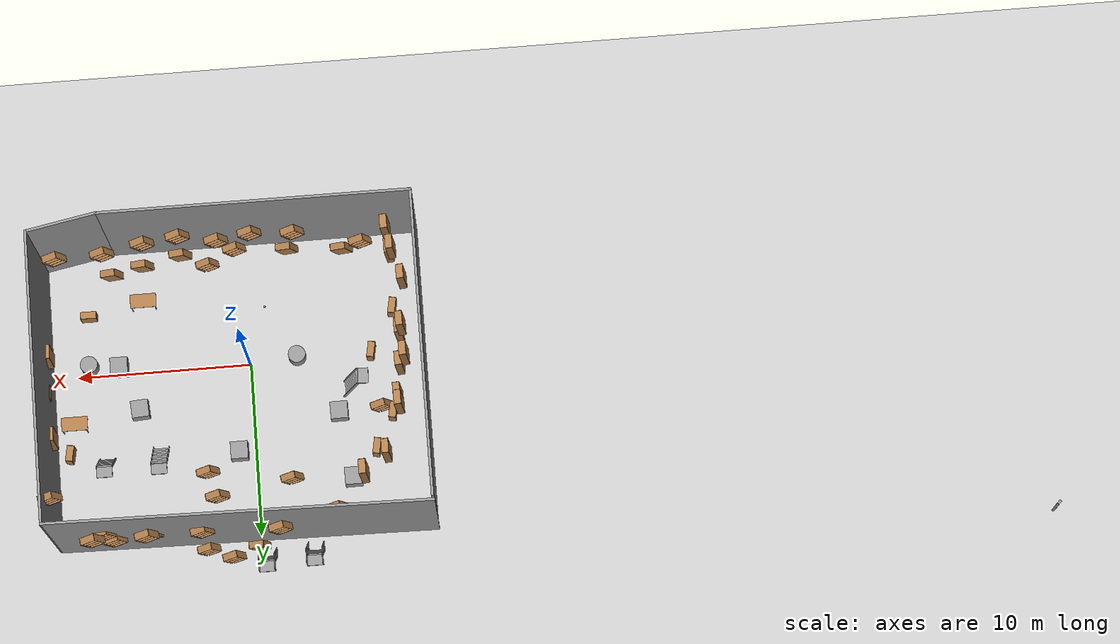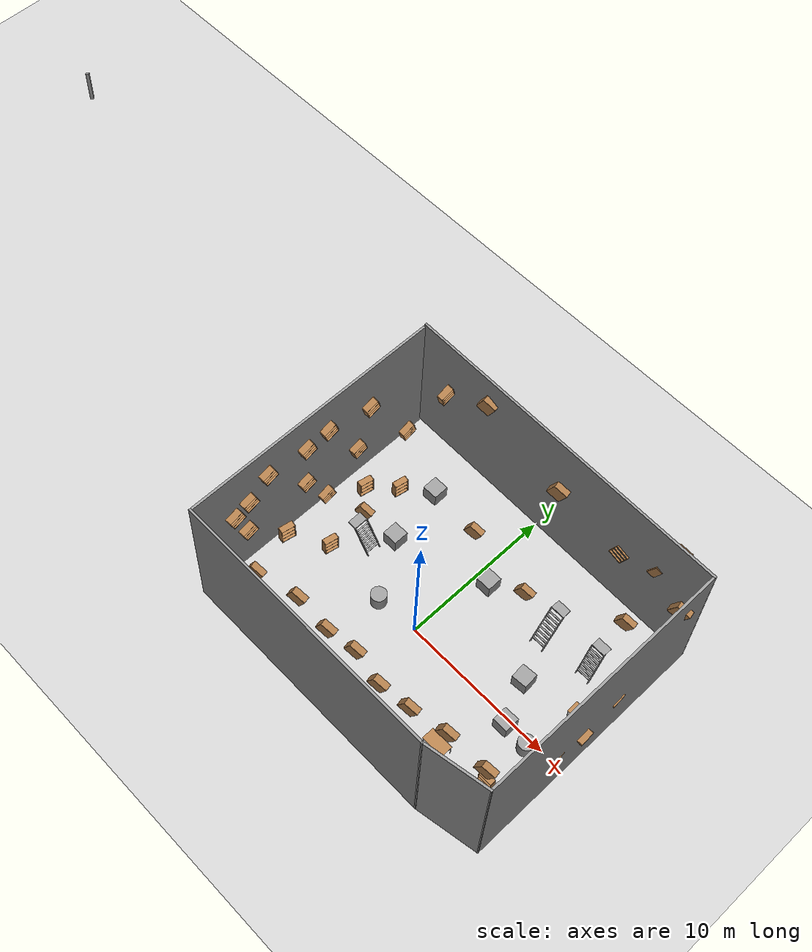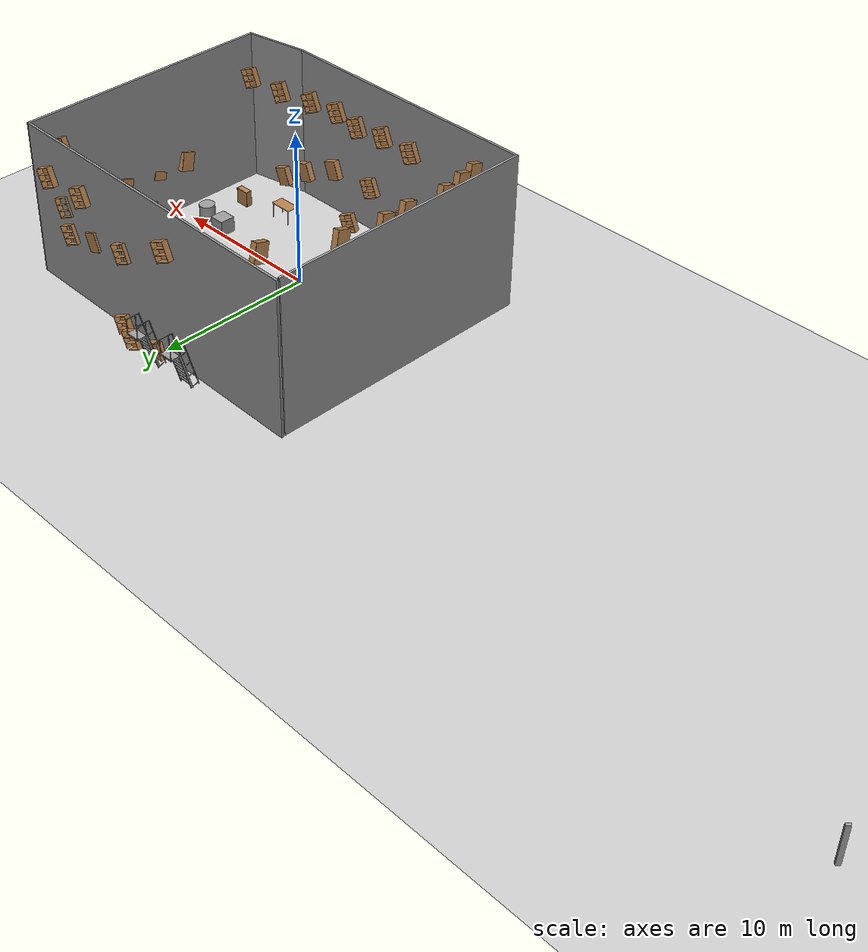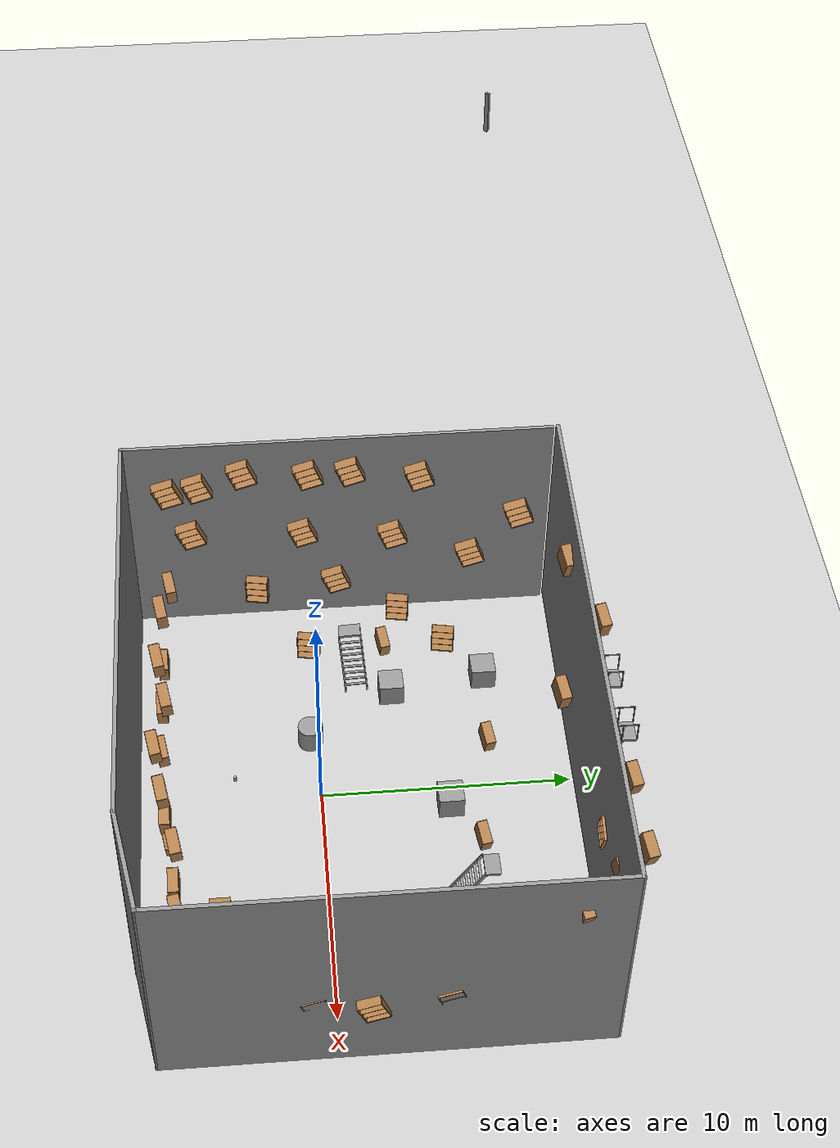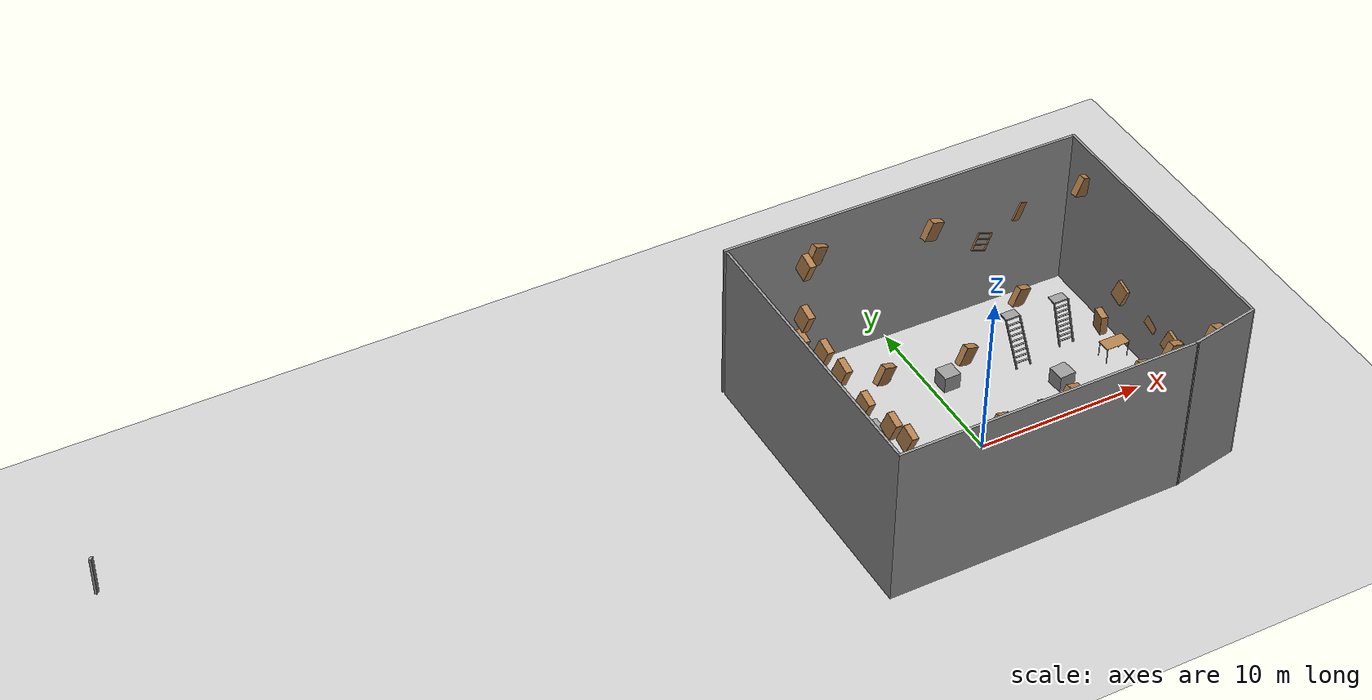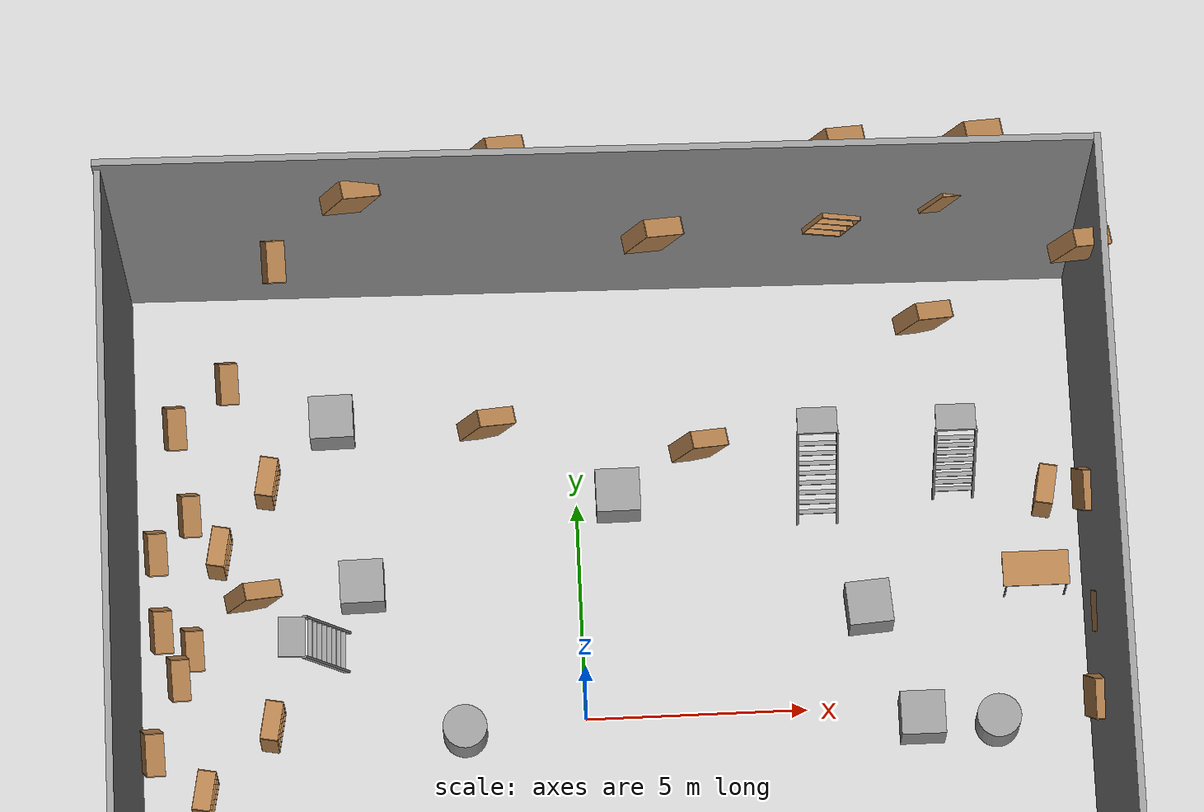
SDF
<sdf version="1.6">
 <world name="default">
  <light name="sun" type="directional">
   <pose>0 0 10 0 -0 0</pose>
   <diffuse>0.8 0.8 0.8 1</diffuse>
   <specular>0.2 0.2 0.2 1</specular>
   <attenuation>
    <range>1000</range>
    <constant>0.9</constant>
    <linear>0.01</linear>
    <quadratic>0.001</quadratic>
   </attenuation>
   <direction>-0.5 0.1 -0.9</direction>
  </light>
  <model name="ground_plane">
   <static>1</static>
   <link name="link">
    <collision name="collision">
     <geometry><plane><normal>0 0 1</normal><size>100 100</size></plane></geometry>
     <surface><friction><ode><mu>100</mu><mu2>50</mu2></ode></friction></surface>
    </collision>
    <visual name="visual">
     <cast_shadows>0</cast_shadows>
     <geometry><plane><normal>0 0 1</normal><size>100 100</size></plane></geometry>
     <material>
      <script><uri>file://media/materials/scripts/gazebo.material</uri><name>Gazebo/Grey</name></script>
     </material>
    </visual>
   </link>
  </model>
  <gravity>0 0 -9.8</gravity>
  <magnetic_field>6e-06 2.3e-05 -4.2e-05</magnetic_field>
  <atmosphere type="adiabatic"/>
  <physics name="default_physics" default="0" type="ode">
   <max_step_size>0.001</max_step_size>
   <real_time_factor>1</real_time_factor>
   <real_time_update_rate>1000</real_time_update_rate>
  </physics>
  <scene><ambient>0.4 0.4 0.4 1</ambient><background>0.7 0.7 0.7 1</background><shadows>1</shadows></scene>
  <spherical_coordinates>
   <surface_model>EARTH_WGS84</surface_model>
   <latitude_deg>0</latitude_deg>
   <longitude_deg>0</longitude_deg>
   <elevation>0</elevation>
   <heading_deg>0</heading_deg>
  </spherical_coordinates>
  <model name="bookshelf">
   <static>1</static>
   <link name="link">
    <inertial><mass>1</mass></inertial>
    <collision name="back">
     <pose>0 0.005 0.6 0 -0 0</pose>
     <geometry><box><size>0.9 0.01 1.2</size></box></geometry>
    </collision>
    <visual name="visual1">
     <pose>0 0.005 0.6 0 -0 0</pose>
     <geometry><box><size>0.9 0.01 1.2</size></box></geometry>
     <material>
      <script><uri>file://media/materials/scripts/gazebo.material</uri><name>Gazebo/Wood</name></script>
     </material>
    </visual>
    <collision name="left_side">
     <pose>0.45 -0.195 0.6 0 -0 0</pose>
     <geometry><box><size>0.02 0.4 1.2</size></box></geometry>
    </collision>
    <visual name="visual2">
     <pose>0.45 -0.195 0.6 0 -0 0</pose>
     <geometry><box><size>0.02 0.4 1.2</size></box></geometry>
     <material>
      <script><uri>file://media/materials/scripts/gazebo.material</uri><name>Gazebo/Wood</name></script>
     </material>
    </visual>
    <collision name="right_side">
     <pose>-0.45 -0.195 0.6 0 -0 0</pose>
     <geometry><box><size>0.02 0.4 1.2</size></box></geometry>
    </collision>
    <visual name="visual3">
     <pose>-0.45 -0.195 0.6 0 -0 0</pose>
     <geometry><box><size>0.02 0.4 1.2</size></box></geometry>
     <material>
      <script><uri>file://media/materials/scripts/gazebo.material</uri><name>Gazebo/Wood</name></script>
     </material>
    </visual>
    <collision name="bottom">
     <pose>0 -0.195 0.03 0 -0 0</pose>
     <geometry><box><size>0.88 0.4 0.06</size></box></geometry>
    </collision>
    <visual name="visual4">
     <pose>0 -0.195 0.03 0 -0 0</pose>
     <geometry><box><size>0.88 0.4 0.06</size></box></geometry>
     <material>
      <script><uri>file://media/materials/scripts/gazebo.material</uri><name>Gazebo/Wood</name></script>
     </material>
    </visual>
    <collision name="top">
     <pose>0 -0.195 1.19 0 -0 0</pose>
     <geometry><box><size>0.88 0.4 0.02</size></box></geometry>
    </collision>
    <visual name="visual5">
     <pose>0 -0.195 1.19 0 -0 0</pose>
     <geometry><box><size>0.88 0.4 0.02</size></box></geometry>
     <material>
      <script><uri>file://media/materials/scripts/gazebo.material</uri><name>Gazebo/Wood</name></script>
     </material>
    </visual>
    <collision name="low_shelf">
     <pose>0 -0.195 0.43 0 -0 0</pose>
     <geometry><box><size>0.88 0.4 0.02</size></box></geometry>
    </collision>
    <visual name="visual6">
     <pose>0 -0.195 0.43 0 -0 0</pose>
     <geometry><box><size>0.88 0.4 0.02</size></box></geometry>
     <material>
      <script><uri>file://media/materials/scripts/gazebo.material</uri><name>Gazebo/Wood</name></script>
     </material>
    </visual>
    <collision name="high_shelf">
     <pose>0 -0.195 0.8 0 -0 0</pose>
     <geometry><box><size>0.88 0.4 0.02</size></box></geometry>
    </collision>
    <visual name="visual7">
     <pose>0 -0.195 0.8 0 -0 0</pose>
     <geometry><box><size>0.88 0.4 0.02</size></box></geometry>
     <material>
      <script><uri>file://media/materials/scripts/gazebo.material</uri><name>Gazebo/Wood</name></script>
     </material>
    </visual>
   </link>
   <pose>9.14499 -3.30261 -0.213908 0 -0 0</pose>
  </model>
  <model name="bookshelf_0">
   <static>1</static>
   <link name="link">
    <inertial><mass>1</mass></inertial>
    <collision name="back">
     <pose>0 0.005 0.6 0 -0 0</pose>
     <geometry><box><size>0.9 0.01 1.2</size></box></geometry>
    </collision>
    <visual name="visual1">
     <pose>0 0.005 0.6 0 -0 0</pose>
     <geometry><box><size>0.9 0.01 1.2</size></box></geometry>
     <material>
      <script><uri>file://media/materials/scripts/gazebo.material</uri><name>Gazebo/Wood</name></script>
     </material>
    </visual>
    <collision name="left_side">
     <pose>0.45 -0.195 0.6 0 -0 0</pose>
     <geometry><box><size>0.02 0.4 1.2</size></box></geometry>
    </collision>
    <visual name="visual2">
     <pose>0.45 -0.195 0.6 0 -0 0</pose>
     <geometry><box><size>0.02 0.4 1.2</size></box></geometry>
     <material>
      <script><uri>file://media/materials/scripts/gazebo.material</uri><name>Gazebo/Wood</name></script>
     </material>
    </visual>
    <collision name="right_side">
     <pose>-0.45 -0.195 0.6 0 -0 0</pose>
     <geometry><box><size>0.02 0.4 1.2</size></box></geometry>
    </collision>
    <visual name="visual3">
     <pose>-0.45 -0.195 0.6 0 -0 0</pose>
     <geometry><box><size>0.02 0.4 1.2</size></box></geometry>
     <material>
      <script><uri>file://media/materials/scripts/gazebo.material</uri><name>Gazebo/Wood</name></script>
     </material>
    </visual>
    <collision name="bottom">
     <pose>0 -0.195 0.03 0 -0 0</pose>
     <geometry><box><size>0.88 0.4 0.06</size></box></geometry>
    </collision>
    <visual name="visual4">
     <pose>0 -0.195 0.03 0 -0 0</pose>
     <geometry><box><size>0.88 0.4 0.06</size></box></geometry>
     <material>
      <script><uri>file://media/materials/scripts/gazebo.material</uri><name>Gazebo/Wood</name></script>
     </material>
    </visual>
    <collision name="top">
     <pose>0 -0.195 1.19 0 -0 0</pose>
     <geometry><box><size>0.88 0.4 0.02</size></box></geometry>
    </collision>
    <visual name="visual5">
     <pose>0 -0.195 1.19 0 -0 0</pose>
     <geometry><box><size>0.88 0.4 0.02</size></box></geometry>
     <material>
      <script><uri>file://media/materials/scripts/gazebo.material</uri><name>Gazebo/Wood</name></script>
     </material>
    </visual>
    <collision name="low_shelf">
     <pose>0 -0.195 0.43 0 -0 0</pose>
     <geometry><box><size>0.88 0.4 0.02</size></box></geometry>
    </collision>
    <visual name="visual6">
     <pose>0 -0.195 0.43 0 -0 0</pose>
     <geometry><box><size>0.88 0.4 0.02</size></box></geometry>
     <material>
      <script><uri>file://media/materials/scripts/gazebo.material</uri><name>Gazebo/Wood</name></script>
     </material>
    </visual>
    <collision name="high_shelf">
     <pose>0 -0.195 0.8 0 -0 0</pose>
     <geometry><box><size>0.88 0.4 0.02</size></box></geometry>
    </collision>
    <visual name="visual7">
     <pose>0 -0.195 0.8 0 -0 0</pose>
     <geometry><box><size>0.88 0.4 0.02</size></box></geometry>
     <material>
      <script><uri>file://media/materials/scripts/gazebo.material</uri><name>Gazebo/Wood</name></script>
     </material>
    </visual>
   </link>
   <pose>7.35267 -5.37274 1.27046 0 0.357608 0</pose>
  </model>
  <model name="bookshelf_1">
   <static>1</static>
   <link name="link">
    <inertial><mass>1</mass></inertial>
    <collision name="back">
     <pose>0 0.005 0.6 0 -0 0</pose>
     <geometry><box><size>0.9 0.01 1.2</size></box></geometry>
    </collision>
    <visual name="visual1">
     <pose>0 0.005 0.6 0 -0 0</pose>
     <geometry><box><size>0.9 0.01 1.2</size></box></geometry>
     <material>
      <script><uri>file://media/materials/scripts/gazebo.material</uri><name>Gazebo/Wood</name></script>
     </material>
    </visual>
    <collision name="left_side">
     <pose>0.45 -0.195 0.6 0 -0 0</pose>
     <geometry><box><size>0.02 0.4 1.2</size></box></geometry>
    </collision>
    <visual name="visual2">
     <pose>0.45 -0.195 0.6 0 -0 0</pose>
     <geometry><box><size>0.02 0.4 1.2</size></box></geometry>
     <material>
      <script><uri>file://media/materials/scripts/gazebo.material</uri><name>Gazebo/Wood</name></script>
     </material>
    </visual>
    <collision name="right_side">
     <pose>-0.45 -0.195 0.6 0 -0 0</pose>
     <geometry><box><size>0.02 0.4 1.2</size></box></geometry>
    </collision>
    <visual name="visual3">
     <pose>-0.45 -0.195 0.6 0 -0 0</pose>
     <geometry><box><size>0.02 0.4 1.2</size></box></geometry>
     <material>
      <script><uri>file://media/materials/scripts/gazebo.material</uri><name>Gazebo/Wood</name></script>
     </material>
    </visual>
    <collision name="bottom">
     <pose>0 -0.195 0.03 0 -0 0</pose>
     <geometry><box><size>0.88 0.4 0.06</size></box></geometry>
    </collision>
    <visual name="visual4">
     <pose>0 -0.195 0.03 0 -0 0</pose>
     <geometry><box><size>0.88 0.4 0.06</size></box></geometry>
     <material>
      <script><uri>file://media/materials/scripts/gazebo.material</uri><name>Gazebo/Wood</name></script>
     </material>
    </visual>
    <collision name="top">
     <pose>0 -0.195 1.19 0 -0 0</pose>
     <geometry><box><size>0.88 0.4 0.02</size></box></geometry>
    </collision>
    <visual name="visual5">
     <pose>0 -0.195 1.19 0 -0 0</pose>
     <geometry><box><size>0.88 0.4 0.02</size></box></geometry>
     <material>
      <script><uri>file://media/materials/scripts/gazebo.material</uri><name>Gazebo/Wood</name></script>
     </material>
    </visual>
    <collision name="low_shelf">
     <pose>0 -0.195 0.43 0 -0 0</pose>
     <geometry><box><size>0.88 0.4 0.02</size></box></geometry>
    </collision>
    <visual name="visual6">
     <pose>0 -0.195 0.43 0 -0 0</pose>
     <geometry><box><size>0.88 0.4 0.02</size></box></geometry>
     <material>
      <script><uri>file://media/materials/scripts/gazebo.material</uri><name>Gazebo/Wood</name></script>
     </material>
    </visual>
    <collision name="high_shelf">
     <pose>0 -0.195 0.8 0 -0 0</pose>
     <geometry><box><size>0.88 0.4 0.02</size></box></geometry>
    </collision>
    <visual name="visual7">
     <pose>0 -0.195 0.8 0 -0 0</pose>
     <geometry><box><size>0.88 0.4 0.02</size></box></geometry>
     <material>
      <script><uri>file://media/materials/scripts/gazebo.material</uri><name>Gazebo/Wood</name></script>
     </material>
    </visual>
   </link>
   <pose>10.3942 4.67177 0.408899 0 -0 1.38737</pose>
  </model>
  <model name="unit_cylinder_0">
   <pose>9.25384 -0.552257 0.599997 1e-06 -6e-06 -4e-06</pose>
   <link name="link">
    <inertial>
     <mass>1</mass>
     <inertia><ixx>0.145833</ixx><ixy>0</ixy><ixz>0</ixz><iyy>0.145833</iyy><iyz>0</iyz><izz>0.125</izz></inertia>
    </inertial>
    <collision name="collision">
     <geometry><cylinder><radius>0.5</radius><length>1</length></cylinder></geometry>
    </collision>
    <visual name="visual">
     <geometry><cylinder><radius>0.5</radius><length>1</length></cylinder></geometry>
     <material>
      <script><name>Gazebo/Grey</name><uri>file://media/materials/scripts/gazebo.material</uri></script>
     </material>
    </visual>
   </link>
  </model>
  <model name="unit_box">
   <pose>-5.51535 7.0781 0.499995 0 -1e-05 0.015398</pose>
   <link name="link">
    <inertial>
     <mass>1</mass>
     <inertia>
      <ixx>0.166667</ixx>
      <ixy>0</ixy>
      <ixz>0</ixz>
      <iyy>0.166667</iyy>
      <iyz>0</iyz>
      <izz>0.166667</izz>
     </inertia>
    </inertial>
    <collision name="collision"><geometry><box><size>1 1 1</size></box></geometry></collision>
    <visual name="visual">
     <geometry><box><size>1 1 1</size></box></geometry>
     <material>
      <script><name>Gazebo/Grey</name><uri>file://media/materials/scripts/gazebo.material</uri></script>
     </material>
    </visual>
   </link>
  </model>
  <model name="unit_box_0">
   <pose>-4.94193 3.18793 0.5 0 -0 0.015659</pose>
   <link name="unit_box_0::link">
    <inertial>
     <mass>1</mass>
     <inertia>
      <ixx>0.166667</ixx>
      <ixy>0</ixy>
      <ixz>0</ixz>
      <iyy>0.166667</iyy>
      <iyz>0</iyz>
      <izz>0.166667</izz>
     </inertia>
    </inertial>
    <collision name="collision"><geometry><box><size>1 1 1</size></box></geometry></collision>
    <visual name="visual">
     <geometry><box><size>1 1 1</size></box></geometry>
     <material>
      <script><name>Gazebo/Grey</name><uri>file://media/materials/scripts/gazebo.material</uri></script>
     </material>
    </visual>
    <enable_wind>1</enable_wind>
    <kinematic>1</kinematic>
   </link>
  </model>
  <model name="unit_box_1">
   <pose>7.5557 -0.384147 0.499995 1e-05 -0 -2.4e-05</pose>
   <link name="link">
    <inertial>
     <mass>1</mass>
     <inertia>
      <ixx>0.166667</ixx>
      <ixy>0</ixy>
      <ixz>0</ixz>
      <iyy>0.166667</iyy>
      <iyz>0</iyz>
      <izz>0.166667</izz>
     </inertia>
    </inertial>
    <collision name="collision"><geometry><box><size>1 1 1</size></box></geometry></collision>
    <visual name="visual">
     <geometry><box><size>1 1 1</size></box></geometry>
     <material>
      <script><name>Gazebo/Grey</name><uri>file://media/materials/scripts/gazebo.material</uri></script>
     </material>
    </visual>
   </link>
  </model>
  <model name="unit_cylinder">
   <pose>-2.73222 -0.271619 0.499994 -4e-06 -1e-06 0</pose>
   <link name="unit_cylinder::link">
    <inertial>
     <mass>1</mass>
     <inertia><ixx>0.145833</ixx><ixy>0</ixy><ixz>0</ixz><iyy>0.145833</iyy><iyz>0</iyz><izz>0.125</izz></inertia>
    </inertial>
    <collision name="collision">
     <geometry><cylinder><radius>0.5</radius><length>1</length></cylinder></geometry>
    </collision>
    <visual name="visual">
     <geometry><cylinder><radius>0.5</radius><length>1</length></cylinder></geometry>
     <material>
      <script><name>Gazebo/Grey</name><uri>file://media/materials/scripts/gazebo.material</uri></script>
     </material>
    </visual>
    <enable_wind>1</enable_wind>
    <kinematic>1</kinematic>
   </link>
  </model>
  <model name="bookshelf_0_clone">
   <static>1</static>
   <link name="link">
    <inertial><mass>1</mass></inertial>
    <collision name="back">
     <pose>0 0.005 0.6 0 -0 0</pose>
     <geometry><box><size>0.9 0.01 1.2</size></box></geometry>
    </collision>
    <visual name="visual1">
     <pose>0 0.005 0.6 0 -0 0</pose>
     <geometry><box><size>0.9 0.01 1.2</size></box></geometry>
     <material>
      <script><uri>file://media/materials/scripts/gazebo.material</uri><name>Gazebo/Wood</name></script>
     </material>
    </visual>
    <collision name="left_side">
     <pose>0.45 -0.195 0.6 0 -0 0</pose>
     <geometry><box><size>0.02 0.4 1.2</size></box></geometry>
    </collision>
    <visual name="visual2">
     <pose>0.45 -0.195 0.6 0 -0 0</pose>
     <geometry><box><size>0.02 0.4 1.2</size></box></geometry>
     <material>
      <script><uri>file://media/materials/scripts/gazebo.material</uri><name>Gazebo/Wood</name></script>
     </material>
    </visual>
    <collision name="right_side">
     <pose>-0.45 -0.195 0.6 0 -0 0</pose>
     <geometry><box><size>0.02 0.4 1.2</size></box></geometry>
    </collision>
    <visual name="visual3">
     <pose>-0.45 -0.195 0.6 0 -0 0</pose>
     <geometry><box><size>0.02 0.4 1.2</size></box></geometry>
     <material>
      <script><uri>file://media/materials/scripts/gazebo.material</uri><name>Gazebo/Wood</name></script>
     </material>
    </visual>
    <collision name="bottom">
     <pose>0 -0.195 0.03 0 -0 0</pose>
     <geometry><box><size>0.88 0.4 0.06</size></box></geometry>
    </collision>
    <visual name="visual4">
     <pose>0 -0.195 0.03 0 -0 0</pose>
     <geometry><box><size>0.88 0.4 0.06</size></box></geometry>
     <material>
      <script><uri>file://media/materials/scripts/gazebo.material</uri><name>Gazebo/Wood</name></script>
     </material>
    </visual>
    <collision name="top">
     <pose>0 -0.195 1.19 0 -0 0</pose>
     <geometry><box><size>0.88 0.4 0.02</size></box></geometry>
    </collision>
    <visual name="visual5">
     <pose>0 -0.195 1.19 0 -0 0</pose>
     <geometry><box><size>0.88 0.4 0.02</size></box></geometry>
     <material>
      <script><uri>file://media/materials/scripts/gazebo.material</uri><name>Gazebo/Wood</name></script>
     </material>
    </visual>
    <collision name="low_shelf">
     <pose>0 -0.195 0.43 0 -0 0</pose>
     <geometry><box><size>0.88 0.4 0.02</size></box></geometry>
    </collision>
    <visual name="visual6">
     <pose>0 -0.195 0.43 0 -0 0</pose>
     <geometry><box><size>0.88 0.4 0.02</size></box></geometry>
     <material>
      <script><uri>file://media/materials/scripts/gazebo.material</uri><name>Gazebo/Wood</name></script>
     </material>
    </visual>
    <collision name="high_shelf">
     <pose>0 -0.195 0.8 0 -0 0</pose>
     <geometry><box><size>0.88 0.4 0.02</size></box></geometry>
    </collision>
    <visual name="visual7">
     <pose>0 -0.195 0.8 0 -0 0</pose>
     <geometry><box><size>0.88 0.4 0.02</size></box></geometry>
     <material>
      <script><uri>file://media/materials/scripts/gazebo.material</uri><name>Gazebo/Wood</name></script>
     </material>
    </visual>
   </link>
   <pose>-5.96629 -5.9266 1.27046 0 0.357608 0</pose>
  </model>
  <model name="bookshelf_0_clone_0">
   <static>1</static>
   <link name="link">
    <inertial><mass>1</mass></inertial>
    <collision name="back">
     <pose>0 0.005 0.6 0 -0 0</pose>
     <geometry><box><size>0.9 0.01 1.2</size></box></geometry>
    </collision>
    <visual name="visual1">
     <pose>0 0.005 0.6 0 -0 0</pose>
     <geometry><box><size>0.9 0.01 1.2</size></box></geometry>
     <material>
      <script><uri>file://media/materials/scripts/gazebo.material</uri><name>Gazebo/Wood</name></script>
     </material>
    </visual>
    <collision name="left_side">
     <pose>0.45 -0.195 0.6 0 -0 0</pose>
     <geometry><box><size>0.02 0.4 1.2</size></box></geometry>
    </collision>
    <visual name="visual2">
     <pose>0.45 -0.195 0.6 0 -0 0</pose>
     <geometry><box><size>0.02 0.4 1.2</size></box></geometry>
     <material>
      <script><uri>file://media/materials/scripts/gazebo.material</uri><name>Gazebo/Wood</name></script>
     </material>
    </visual>
    <collision name="right_side">
     <pose>-0.45 -0.195 0.6 0 -0 0</pose>
     <geometry><box><size>0.02 0.4 1.2</size></box></geometry>
    </collision>
    <visual name="visual3">
     <pose>-0.45 -0.195 0.6 0 -0 0</pose>
     <geometry><box><size>0.02 0.4 1.2</size></box></geometry>
     <material>
      <script><uri>file://media/materials/scripts/gazebo.material</uri><name>Gazebo/Wood</name></script>
     </material>
    </visual>
    <collision name="bottom">
     <pose>0 -0.195 0.03 0 -0 0</pose>
     <geometry><box><size>0.88 0.4 0.06</size></box></geometry>
    </collision>
    <visual name="visual4">
     <pose>0 -0.195 0.03 0 -0 0</pose>
     <geometry><box><size>0.88 0.4 0.06</size></box></geometry>
     <material>
      <script><uri>file://media/materials/scripts/gazebo.material</uri><name>Gazebo/Wood</name></script>
     </material>
    </visual>
    <collision name="top">
     <pose>0 -0.195 1.19 0 -0 0</pose>
     <geometry><box><size>0.88 0.4 0.02</size></box></geometry>
    </collision>
    <visual name="visual5">
     <pose>0 -0.195 1.19 0 -0 0</pose>
     <geometry><box><size>0.88 0.4 0.02</size></box></geometry>
     <material>
      <script><uri>file://media/materials/scripts/gazebo.material</uri><name>Gazebo/Wood</name></script>
     </material>
    </visual>
    <collision name="low_shelf">
     <pose>0 -0.195 0.43 0 -0 0</pose>
     <geometry><box><size>0.88 0.4 0.02</size></box></geometry>
    </collision>
    <visual name="visual6">
     <pose>0 -0.195 0.43 0 -0 0</pose>
     <geometry><box><size>0.88 0.4 0.02</size></box></geometry>
     <material>
      <script><uri>file://media/materials/scripts/gazebo.material</uri><name>Gazebo/Wood</name></script>
     </material>
    </visual>
    <collision name="high_shelf">
     <pose>0 -0.195 0.8 0 -0 0</pose>
     <geometry><box><size>0.88 0.4 0.02</size></box></geometry>
    </collision>
    <visual name="visual7">
     <pose>0 -0.195 0.8 0 -0 0</pose>
     <geometry><box><size>0.88 0.4 0.02</size></box></geometry>
     <material>
      <script><uri>file://media/materials/scripts/gazebo.material</uri><name>Gazebo/Wood</name></script>
     </material>
    </visual>
   </link>
   <pose>5.69398 10.33 4.06756 0 0.357608 0</pose>
  </model>
  <model name="bookshelf_0_clone_1">
   <static>1</static>
   <link name="link">
    <inertial><mass>1</mass></inertial>
    <collision name="back">
     <pose>0 0.005 0.6 0 -0 0</pose>
     <geometry><box><size>0.9 0.01 1.2</size></box></geometry>
    </collision>
    <visual name="visual1">
     <pose>0 0.005 0.6 0 -0 0</pose>
     <geometry><box><size>0.9 0.01 1.2</size></box></geometry>
     <material>
      <script><uri>file://media/materials/scripts/gazebo.material</uri><name>Gazebo/Wood</name></script>
     </material>
    </visual>
    <collision name="left_side">
     <pose>0.45 -0.195 0.6 0 -0 0</pose>
     <geometry><box><size>0.02 0.4 1.2</size></box></geometry>
    </collision>
    <visual name="visual2">
     <pose>0.45 -0.195 0.6 0 -0 0</pose>
     <geometry><box><size>0.02 0.4 1.2</size></box></geometry>
     <material>
      <script><uri>file://media/materials/scripts/gazebo.material</uri><name>Gazebo/Wood</name></script>
     </material>
    </visual>
    <collision name="right_side">
     <pose>-0.45 -0.195 0.6 0 -0 0</pose>
     <geometry><box><size>0.02 0.4 1.2</size></box></geometry>
    </collision>
    <visual name="visual3">
     <pose>-0.45 -0.195 0.6 0 -0 0</pose>
     <geometry><box><size>0.02 0.4 1.2</size></box></geometry>
     <material>
      <script><uri>file://media/materials/scripts/gazebo.material</uri><name>Gazebo/Wood</name></script>
     </material>
    </visual>
    <collision name="bottom">
     <pose>0 -0.195 0.03 0 -0 0</pose>
     <geometry><box><size>0.88 0.4 0.06</size></box></geometry>
    </collision>
    <visual name="visual4">
     <pose>0 -0.195 0.03 0 -0 0</pose>
     <geometry><box><size>0.88 0.4 0.06</size></box></geometry>
     <material>
      <script><uri>file://media/materials/scripts/gazebo.material</uri><name>Gazebo/Wood</name></script>
     </material>
    </visual>
    <collision name="top">
     <pose>0 -0.195 1.19 0 -0 0</pose>
     <geometry><box><size>0.88 0.4 0.02</size></box></geometry>
    </collision>
    <visual name="visual5">
     <pose>0 -0.195 1.19 0 -0 0</pose>
     <geometry><box><size>0.88 0.4 0.02</size></box></geometry>
     <material>
      <script><uri>file://media/materials/scripts/gazebo.material</uri><name>Gazebo/Wood</name></script>
     </material>
    </visual>
    <collision name="low_shelf">
     <pose>0 -0.195 0.43 0 -0 0</pose>
     <geometry><box><size>0.88 0.4 0.02</size></box></geometry>
    </collision>
    <visual name="visual6">
     <pose>0 -0.195 0.43 0 -0 0</pose>
     <geometry><box><size>0.88 0.4 0.02</size></box></geometry>
     <material>
      <script><uri>file://media/materials/scripts/gazebo.material</uri><name>Gazebo/Wood</name></script>
     </material>
    </visual>
    <collision name="high_shelf">
     <pose>0 -0.195 0.8 0 -0 0</pose>
     <geometry><box><size>0.88 0.4 0.02</size></box></geometry>
    </collision>
    <visual name="visual7">
     <pose>0 -0.195 0.8 0 -0 0</pose>
     <geometry><box><size>0.88 0.4 0.02</size></box></geometry>
     <material>
      <script><uri>file://media/materials/scripts/gazebo.material</uri><name>Gazebo/Wood</name></script>
     </material>
    </visual>
   </link>
   <pose>-0.09659 10.8007 -0.3401 0 0.357608 0</pose>
  </model>
  <model name="bookshelf_0_clone_1_clone">
   <static>1</static>
   <link name="link">
    <inertial><mass>1</mass></inertial>
    <collision name="back">
     <pose>0 0.005 0.6 0 -0 0</pose>
     <geometry><box><size>0.9 0.01 1.2</size></box></geometry>
    </collision>
    <visual name="visual1">
     <pose>0 0.005 0.6 0 -0 0</pose>
     <geometry><box><size>0.9 0.01 1.2</size></box></geometry>
     <material>
      <script><uri>file://media/materials/scripts/gazebo.material</uri><name>Gazebo/Wood</name></script>
     </material>
    </visual>
    <collision name="left_side">
     <pose>0.45 -0.195 0.6 0 -0 0</pose>
     <geometry><box><size>0.02 0.4 1.2</size></box></geometry>
    </collision>
    <visual name="visual2">
     <pose>0.45 -0.195 0.6 0 -0 0</pose>
     <geometry><box><size>0.02 0.4 1.2</size></box></geometry>
     <material>
      <script><uri>file://media/materials/scripts/gazebo.material</uri><name>Gazebo/Wood</name></script>
     </material>
    </visual>
    <collision name="right_side">
     <pose>-0.45 -0.195 0.6 0 -0 0</pose>
     <geometry><box><size>0.02 0.4 1.2</size></box></geometry>
    </collision>
    <visual name="visual3">
     <pose>-0.45 -0.195 0.6 0 -0 0</pose>
     <geometry><box><size>0.02 0.4 1.2</size></box></geometry>
     <material>
      <script><uri>file://media/materials/scripts/gazebo.material</uri><name>Gazebo/Wood</name></script>
     </material>
    </visual>
    <collision name="bottom">
     <pose>0 -0.195 0.03 0 -0 0</pose>
     <geometry><box><size>0.88 0.4 0.06</size></box></geometry>
    </collision>
    <visual name="visual4">
     <pose>0 -0.195 0.03 0 -0 0</pose>
     <geometry><box><size>0.88 0.4 0.06</size></box></geometry>
     <material>
      <script><uri>file://media/materials/scripts/gazebo.material</uri><name>Gazebo/Wood</name></script>
     </material>
    </visual>
    <collision name="top">
     <pose>0 -0.195 1.19 0 -0 0</pose>
     <geometry><box><size>0.88 0.4 0.02</size></box></geometry>
    </collision>
    <visual name="visual5">
     <pose>0 -0.195 1.19 0 -0 0</pose>
     <geometry><box><size>0.88 0.4 0.02</size></box></geometry>
     <material>
      <script><uri>file://media/materials/scripts/gazebo.material</uri><name>Gazebo/Wood</name></script>
     </material>
    </visual>
    <collision name="low_shelf">
     <pose>0 -0.195 0.43 0 -0 0</pose>
     <geometry><box><size>0.88 0.4 0.02</size></box></geometry>
    </collision>
    <visual name="visual6">
     <pose>0 -0.195 0.43 0 -0 0</pose>
     <geometry><box><size>0.88 0.4 0.02</size></box></geometry>
     <material>
      <script><uri>file://media/materials/scripts/gazebo.material</uri><name>Gazebo/Wood</name></script>
     </material>
    </visual>
    <collision name="high_shelf">
     <pose>0 -0.195 0.8 0 -0 0</pose>
     <geometry><box><size>0.88 0.4 0.02</size></box></geometry>
    </collision>
    <visual name="visual7">
     <pose>0 -0.195 0.8 0 -0 0</pose>
     <geometry><box><size>0.88 0.4 0.02</size></box></geometry>
     <material>
      <script><uri>file://media/materials/scripts/gazebo.material</uri><name>Gazebo/Wood</name></script>
     </material>
    </visual>
   </link>
   <pose>5.46941 -5.51101 2.30622 0 0.357608 0</pose>
  </model>
  <model name="bookshelf_0_clone_1_clone_0">
   <static>1</static>
   <link name="link">
    <inertial><mass>1</mass></inertial>
    <collision name="back">
     <pose>0 0.005 0.6 0 -0 0</pose>
     <geometry><box><size>0.9 0.01 1.2</size></box></geometry>
    </collision>
    <visual name="visual1">
     <pose>0 0.005 0.6 0 -0 0</pose>
     <geometry><box><size>0.9 0.01 1.2</size></box></geometry>
     <material>
      <script><uri>file://media/materials/scripts/gazebo.material</uri><name>Gazebo/Wood</name></script>
     </material>
    </visual>
    <collision name="left_side">
     <pose>0.45 -0.195 0.6 0 -0 0</pose>
     <geometry><box><size>0.02 0.4 1.2</size></box></geometry>
    </collision>
    <visual name="visual2">
     <pose>0.45 -0.195 0.6 0 -0 0</pose>
     <geometry><box><size>0.02 0.4 1.2</size></box></geometry>
     <material>
      <script><uri>file://media/materials/scripts/gazebo.material</uri><name>Gazebo/Wood</name></script>
     </material>
    </visual>
    <collision name="right_side">
     <pose>-0.45 -0.195 0.6 0 -0 0</pose>
     <geometry><box><size>0.02 0.4 1.2</size></box></geometry>
    </collision>
    <visual name="visual3">
     <pose>-0.45 -0.195 0.6 0 -0 0</pose>
     <geometry><box><size>0.02 0.4 1.2</size></box></geometry>
     <material>
      <script><uri>file://media/materials/scripts/gazebo.material</uri><name>Gazebo/Wood</name></script>
     </material>
    </visual>
    <collision name="bottom">
     <pose>0 -0.195 0.03 0 -0 0</pose>
     <geometry><box><size>0.88 0.4 0.06</size></box></geometry>
    </collision>
    <visual name="visual4">
     <pose>0 -0.195 0.03 0 -0 0</pose>
     <geometry><box><size>0.88 0.4 0.06</size></box></geometry>
     <material>
      <script><uri>file://media/materials/scripts/gazebo.material</uri><name>Gazebo/Wood</name></script>
     </material>
    </visual>
    <collision name="top">
     <pose>0 -0.195 1.19 0 -0 0</pose>
     <geometry><box><size>0.88 0.4 0.02</size></box></geometry>
    </collision>
    <visual name="visual5">
     <pose>0 -0.195 1.19 0 -0 0</pose>
     <geometry><box><size>0.88 0.4 0.02</size></box></geometry>
     <material>
      <script><uri>file://media/materials/scripts/gazebo.material</uri><name>Gazebo/Wood</name></script>
     </material>
    </visual>
    <collision name="low_shelf">
     <pose>0 -0.195 0.43 0 -0 0</pose>
     <geometry><box><size>0.88 0.4 0.02</size></box></geometry>
    </collision>
    <visual name="visual6">
     <pose>0 -0.195 0.43 0 -0 0</pose>
     <geometry><box><size>0.88 0.4 0.02</size></box></geometry>
     <material>
      <script><uri>file://media/materials/scripts/gazebo.material</uri><name>Gazebo/Wood</name></script>
     </material>
    </visual>
    <collision name="high_shelf">
     <pose>0 -0.195 0.8 0 -0 0</pose>
     <geometry><box><size>0.88 0.4 0.02</size></box></geometry>
    </collision>
    <visual name="visual7">
     <pose>0 -0.195 0.8 0 -0 0</pose>
     <geometry><box><size>0.88 0.4 0.02</size></box></geometry>
     <material>
      <script><uri>file://media/materials/scripts/gazebo.material</uri><name>Gazebo/Wood</name></script>
     </material>
    </visual>
   </link>
   <pose>-2.86158 -5.91145 2.30622 0 0.357608 0</pose>
  </model>
  <model name="bookshelf_0_clone_1_clone_1">
   <static>1</static>
   <link name="link">
    <inertial><mass>1</mass></inertial>
    <collision name="back">
     <pose>0 0.005 0.6 0 -0 0</pose>
     <geometry><box><size>0.9 0.01 1.2</size></box></geometry>
    </collision>
    <visual name="visual1">
     <pose>0 0.005 0.6 0 -0 0</pose>
     <geometry><box><size>0.9 0.01 1.2</size></box></geometry>
     <material>
      <script><uri>file://media/materials/scripts/gazebo.material</uri><name>Gazebo/Wood</name></script>
     </material>
    </visual>
    <collision name="left_side">
     <pose>0.45 -0.195 0.6 0 -0 0</pose>
     <geometry><box><size>0.02 0.4 1.2</size></box></geometry>
    </collision>
    <visual name="visual2">
     <pose>0.45 -0.195 0.6 0 -0 0</pose>
     <geometry><box><size>0.02 0.4 1.2</size></box></geometry>
     <material>
      <script><uri>file://media/materials/scripts/gazebo.material</uri><name>Gazebo/Wood</name></script>
     </material>
    </visual>
    <collision name="right_side">
     <pose>-0.45 -0.195 0.6 0 -0 0</pose>
     <geometry><box><size>0.02 0.4 1.2</size></box></geometry>
    </collision>
    <visual name="visual3">
     <pose>-0.45 -0.195 0.6 0 -0 0</pose>
     <geometry><box><size>0.02 0.4 1.2</size></box></geometry>
     <material>
      <script><uri>file://media/materials/scripts/gazebo.material</uri><name>Gazebo/Wood</name></script>
     </material>
    </visual>
    <collision name="bottom">
     <pose>0 -0.195 0.03 0 -0 0</pose>
     <geometry><box><size>0.88 0.4 0.06</size></box></geometry>
    </collision>
    <visual name="visual4">
     <pose>0 -0.195 0.03 0 -0 0</pose>
     <geometry><box><size>0.88 0.4 0.06</size></box></geometry>
     <material>
      <script><uri>file://media/materials/scripts/gazebo.material</uri><name>Gazebo/Wood</name></script>
     </material>
    </visual>
    <collision name="top">
     <pose>0 -0.195 1.19 0 -0 0</pose>
     <geometry><box><size>0.88 0.4 0.02</size></box></geometry>
    </collision>
    <visual name="visual5">
     <pose>0 -0.195 1.19 0 -0 0</pose>
     <geometry><box><size>0.88 0.4 0.02</size></box></geometry>
     <material>
      <script><uri>file://media/materials/scripts/gazebo.material</uri><name>Gazebo/Wood</name></script>
     </material>
    </visual>
    <collision name="low_shelf">
     <pose>0 -0.195 0.43 0 -0 0</pose>
     <geometry><box><size>0.88 0.4 0.02</size></box></geometry>
    </collision>
    <visual name="visual6">
     <pose>0 -0.195 0.43 0 -0 0</pose>
     <geometry><box><size>0.88 0.4 0.02</size></box></geometry>
     <material>
      <script><uri>file://media/materials/scripts/gazebo.material</uri><name>Gazebo/Wood</name></script>
     </material>
    </visual>
    <collision name="high_shelf">
     <pose>0 -0.195 0.8 0 -0 0</pose>
     <geometry><box><size>0.88 0.4 0.02</size></box></geometry>
    </collision>
    <visual name="visual7">
     <pose>0 -0.195 0.8 0 -0 0</pose>
     <geometry><box><size>0.88 0.4 0.02</size></box></geometry>
     <material>
      <script><uri>file://media/materials/scripts/gazebo.material</uri><name>Gazebo/Wood</name></script>
     </material>
    </visual>
   </link>
   <pose>3.18097 -5.75155 3.29708 0 0.357608 0</pose>
  </model>
  <model name="bookshelf_0_clone_1_clone_2">
   <static>1</static>
   <link name="link">
    <inertial><mass>1</mass></inertial>
    <collision name="back">
     <pose>0 0.005 0.6 0 -0 0</pose>
     <geometry><box><size>0.9 0.01 1.2</size></box></geometry>
    </collision>
    <visual name="visual1">
     <pose>0 0.005 0.6 0 -0 0</pose>
     <geometry><box><size>0.9 0.01 1.2</size></box></geometry>
     <material>
      <script><uri>file://media/materials/scripts/gazebo.material</uri><name>Gazebo/Wood</name></script>
     </material>
    </visual>
    <collision name="left_side">
     <pose>0.45 -0.195 0.6 0 -0 0</pose>
     <geometry><box><size>0.02 0.4 1.2</size></box></geometry>
    </collision>
    <visual name="visual2">
     <pose>0.45 -0.195 0.6 0 -0 0</pose>
     <geometry><box><size>0.02 0.4 1.2</size></box></geometry>
     <material>
      <script><uri>file://media/materials/scripts/gazebo.material</uri><name>Gazebo/Wood</name></script>
     </material>
    </visual>
    <collision name="right_side">
     <pose>-0.45 -0.195 0.6 0 -0 0</pose>
     <geometry><box><size>0.02 0.4 1.2</size></box></geometry>
    </collision>
    <visual name="visual3">
     <pose>-0.45 -0.195 0.6 0 -0 0</pose>
     <geometry><box><size>0.02 0.4 1.2</size></box></geometry>
     <material>
      <script><uri>file://media/materials/scripts/gazebo.material</uri><name>Gazebo/Wood</name></script>
     </material>
    </visual>
    <collision name="bottom">
     <pose>0 -0.195 0.03 0 -0 0</pose>
     <geometry><box><size>0.88 0.4 0.06</size></box></geometry>
    </collision>
    <visual name="visual4">
     <pose>0 -0.195 0.03 0 -0 0</pose>
     <geometry><box><size>0.88 0.4 0.06</size></box></geometry>
     <material>
      <script><uri>file://media/materials/scripts/gazebo.material</uri><name>Gazebo/Wood</name></script>
     </material>
    </visual>
    <collision name="top">
     <pose>0 -0.195 1.19 0 -0 0</pose>
     <geometry><box><size>0.88 0.4 0.02</size></box></geometry>
    </collision>
    <visual name="visual5">
     <pose>0 -0.195 1.19 0 -0 0</pose>
     <geometry><box><size>0.88 0.4 0.02</size></box></geometry>
     <material>
      <script><uri>file://media/materials/scripts/gazebo.material</uri><name>Gazebo/Wood</name></script>
     </material>
    </visual>
    <collision name="low_shelf">
     <pose>0 -0.195 0.43 0 -0 0</pose>
     <geometry><box><size>0.88 0.4 0.02</size></box></geometry>
    </collision>
    <visual name="visual6">
     <pose>0 -0.195 0.43 0 -0 0</pose>
     <geometry><box><size>0.88 0.4 0.02</size></box></geometry>
     <material>
      <script><uri>file://media/materials/scripts/gazebo.material</uri><name>Gazebo/Wood</name></script>
     </material>
    </visual>
    <collision name="high_shelf">
     <pose>0 -0.195 0.8 0 -0 0</pose>
     <geometry><box><size>0.88 0.4 0.02</size></box></geometry>
    </collision>
    <visual name="visual7">
     <pose>0 -0.195 0.8 0 -0 0</pose>
     <geometry><box><size>0.88 0.4 0.02</size></box></geometry>
     <material>
      <script><uri>file://media/materials/scripts/gazebo.material</uri><name>Gazebo/Wood</name></script>
     </material>
    </visual>
   </link>
   <pose>11.0365 -0.563524 2.70391 0.126952 -0.31446 1.5878</pose>
  </model>
  <model name="unit_box_1_clone">
   <pose>6.48955 2.22059 0.5 0 -0 0.074709</pose>
   <link name="unit_box_1_clone::link">
    <inertial>
     <mass>1</mass>
     <inertia>
      <ixx>0.166667</ixx>
      <ixy>0</ixy>
      <ixz>0</ixz>
      <iyy>0.166667</iyy>
      <iyz>0</iyz>
      <izz>0.166667</izz>
     </inertia>
    </inertial>
    <collision name="collision"><geometry><box><size>1 1 1</size></box></geometry></collision>
    <visual name="visual">
     <geometry><box><size>1 1 1</size></box></geometry>
     <material>
      <script><name>Gazebo/Grey</name><uri>file://media/materials/scripts/gazebo.material</uri></script>
     </material>
    </visual>
   </link>
  </model>
  <model name="unit_box_1_clone_clone">
   <pose>0.931791 5.07815 0.499995 0 1e-05 0.005799</pose>
   <link name="unit_box_1_clone::link">
    <inertial>
     <mass>1</mass>
     <inertia>
      <ixx>0.166667</ixx>
      <ixy>0</ixy>
      <ixz>0</ixz>
      <iyy>0.166667</iyy>
      <iyz>0</iyz>
      <izz>0.166667</izz>
     </inertia>
    </inertial>
    <collision name="collision"><geometry><box><size>1 1 1</size></box></geometry></collision>
    <visual name="visual">
     <geometry><box><size>1 1 1</size></box></geometry>
     <material>
      <script><name>Gazebo/Grey</name><uri>file://media/materials/scripts/gazebo.material</uri></script>
     </material>
    </visual>
   </link>
  </model>
  <model name="bookshelf_0_clone_1_clone_2_clone">
   <static>1</static>
   <link name="link">
    <inertial><mass>1</mass></inertial>
    <collision name="back">
     <pose>0 0.005 0.6 0 -0 0</pose>
     <geometry><box><size>0.9 0.01 1.2</size></box></geometry>
    </collision>
    <visual name="visual1">
     <pose>0 0.005 0.6 0 -0 0</pose>
     <geometry><box><size>0.9 0.01 1.2</size></box></geometry>
     <material>
      <script><uri>file://media/materials/scripts/gazebo.material</uri><name>Gazebo/Wood</name></script>
     </material>
    </visual>
    <collision name="left_side">
     <pose>0.45 -0.195 0.6 0 -0 0</pose>
     <geometry><box><size>0.02 0.4 1.2</size></box></geometry>
    </collision>
    <visual name="visual2">
     <pose>0.45 -0.195 0.6 0 -0 0</pose>
     <geometry><box><size>0.02 0.4 1.2</size></box></geometry>
     <material>
      <script><uri>file://media/materials/scripts/gazebo.material</uri><name>Gazebo/Wood</name></script>
     </material>
    </visual>
    <collision name="right_side">
     <pose>-0.45 -0.195 0.6 0 -0 0</pose>
     <geometry><box><size>0.02 0.4 1.2</size></box></geometry>
    </collision>
    <visual name="visual3">
     <pose>-0.45 -0.195 0.6 0 -0 0</pose>
     <geometry><box><size>0.02 0.4 1.2</size></box></geometry>
     <material>
      <script><uri>file://media/materials/scripts/gazebo.material</uri><name>Gazebo/Wood</name></script>
     </material>
    </visual>
    <collision name="bottom">
     <pose>0 -0.195 0.03 0 -0 0</pose>
     <geometry><box><size>0.88 0.4 0.06</size></box></geometry>
    </collision>
    <visual name="visual4">
     <pose>0 -0.195 0.03 0 -0 0</pose>
     <geometry><box><size>0.88 0.4 0.06</size></box></geometry>
     <material>
      <script><uri>file://media/materials/scripts/gazebo.material</uri><name>Gazebo/Wood</name></script>
     </material>
    </visual>
    <collision name="top">
     <pose>0 -0.195 1.19 0 -0 0</pose>
     <geometry><box><size>0.88 0.4 0.02</size></box></geometry>
    </collision>
    <visual name="visual5">
     <pose>0 -0.195 1.19 0 -0 0</pose>
     <geometry><box><size>0.88 0.4 0.02</size></box></geometry>
     <material>
      <script><uri>file://media/materials/scripts/gazebo.material</uri><name>Gazebo/Wood</name></script>
     </material>
    </visual>
    <collision name="low_shelf">
     <pose>0 -0.195 0.43 0 -0 0</pose>
     <geometry><box><size>0.88 0.4 0.02</size></box></geometry>
    </collision>
    <visual name="visual6">
     <pose>0 -0.195 0.43 0 -0 0</pose>
     <geometry><box><size>0.88 0.4 0.02</size></box></geometry>
     <material>
      <script><uri>file://media/materials/scripts/gazebo.material</uri><name>Gazebo/Wood</name></script>
     </material>
    </visual>
    <collision name="high_shelf">
     <pose>0 -0.195 0.8 0 -0 0</pose>
     <geometry><box><size>0.88 0.4 0.02</size></box></geometry>
    </collision>
    <visual name="visual7">
     <pose>0 -0.195 0.8 0 -0 0</pose>
     <geometry><box><size>0.88 0.4 0.02</size></box></geometry>
     <material>
      <script><uri>file://media/materials/scripts/gazebo.material</uri><name>Gazebo/Wood</name></script>
     </material>
    </visual>
   </link>
   <pose>11.3251 1.36662 2.70391 0.126952 -0.31446 1.5878</pose>
  </model>
  <model name="bookshelf_0_clone_1_clone_2_clone_0">
   <static>1</static>
   <link name="link">
    <inertial><mass>1</mass></inertial>
    <collision name="back">
     <pose>0 0.005 0.6 0 -0 0</pose>
     <geometry><box><size>0.9 0.01 1.2</size></box></geometry>
    </collision>
    <visual name="visual1">
     <pose>0 0.005 0.6 0 -0 0</pose>
     <geometry><box><size>0.9 0.01 1.2</size></box></geometry>
     <material>
      <script><uri>file://media/materials/scripts/gazebo.material</uri><name>Gazebo/Wood</name></script>
     </material>
    </visual>
    <collision name="left_side">
     <pose>0.45 -0.195 0.6 0 -0 0</pose>
     <geometry><box><size>0.02 0.4 1.2</size></box></geometry>
    </collision>
    <visual name="visual2">
     <pose>0.45 -0.195 0.6 0 -0 0</pose>
     <geometry><box><size>0.02 0.4 1.2</size></box></geometry>
     <material>
      <script><uri>file://media/materials/scripts/gazebo.material</uri><name>Gazebo/Wood</name></script>
     </material>
    </visual>
    <collision name="right_side">
     <pose>-0.45 -0.195 0.6 0 -0 0</pose>
     <geometry><box><size>0.02 0.4 1.2</size></box></geometry>
    </collision>
    <visual name="visual3">
     <pose>-0.45 -0.195 0.6 0 -0 0</pose>
     <geometry><box><size>0.02 0.4 1.2</size></box></geometry>
     <material>
      <script><uri>file://media/materials/scripts/gazebo.material</uri><name>Gazebo/Wood</name></script>
     </material>
    </visual>
    <collision name="bottom">
     <pose>0 -0.195 0.03 0 -0 0</pose>
     <geometry><box><size>0.88 0.4 0.06</size></box></geometry>
    </collision>
    <visual name="visual4">
     <pose>0 -0.195 0.03 0 -0 0</pose>
     <geometry><box><size>0.88 0.4 0.06</size></box></geometry>
     <material>
      <script><uri>file://media/materials/scripts/gazebo.material</uri><name>Gazebo/Wood</name></script>
     </material>
    </visual>
    <collision name="top">
     <pose>0 -0.195 1.19 0 -0 0</pose>
     <geometry><box><size>0.88 0.4 0.02</size></box></geometry>
    </collision>
    <visual name="visual5">
     <pose>0 -0.195 1.19 0 -0 0</pose>
     <geometry><box><size>0.88 0.4 0.02</size></box></geometry>
     <material>
      <script><uri>file://media/materials/scripts/gazebo.material</uri><name>Gazebo/Wood</name></script>
     </material>
    </visual>
    <collision name="low_shelf">
     <pose>0 -0.195 0.43 0 -0 0</pose>
     <geometry><box><size>0.88 0.4 0.02</size></box></geometry>
    </collision>
    <visual name="visual6">
     <pose>0 -0.195 0.43 0 -0 0</pose>
     <geometry><box><size>0.88 0.4 0.02</size></box></geometry>
     <material>
      <script><uri>file://media/materials/scripts/gazebo.material</uri><name>Gazebo/Wood</name></script>
     </material>
    </visual>
    <collision name="high_shelf">
     <pose>0 -0.195 0.8 0 -0 0</pose>
     <geometry><box><size>0.88 0.4 0.02</size></box></geometry>
    </collision>
    <visual name="visual7">
     <pose>0 -0.195 0.8 0 -0 0</pose>
     <geometry><box><size>0.88 0.4 0.02</size></box></geometry>
     <material>
      <script><uri>file://media/materials/scripts/gazebo.material</uri><name>Gazebo/Wood</name></script>
     </material>
    </visual>
   </link>
   <pose>11.0686 4.1971 2.70391 0.126952 -0.31446 1.5878</pose>
  </model>
  <model name="bookshelf_0_clone_1_clone_2_clone_1">
   <static>1</static>
   <link name="link">
    <inertial><mass>1</mass></inertial>
    <collision name="back">
     <pose>0 0.005 0.6 0 -0 0</pose>
     <geometry><box><size>0.9 0.01 1.2</size></box></geometry>
    </collision>
    <visual name="visual1">
     <pose>0 0.005 0.6 0 -0 0</pose>
     <geometry><box><size>0.9 0.01 1.2</size></box></geometry>
     <material>
      <script><uri>file://media/materials/scripts/gazebo.material</uri><name>Gazebo/Wood</name></script>
     </material>
    </visual>
    <collision name="left_side">
     <pose>0.45 -0.195 0.6 0 -0 0</pose>
     <geometry><box><size>0.02 0.4 1.2</size></box></geometry>
    </collision>
    <visual name="visual2">
     <pose>0.45 -0.195 0.6 0 -0 0</pose>
     <geometry><box><size>0.02 0.4 1.2</size></box></geometry>
     <material>
      <script><uri>file://media/materials/scripts/gazebo.material</uri><name>Gazebo/Wood</name></script>
     </material>
    </visual>
    <collision name="right_side">
     <pose>-0.45 -0.195 0.6 0 -0 0</pose>
     <geometry><box><size>0.02 0.4 1.2</size></box></geometry>
    </collision>
    <visual name="visual3">
     <pose>-0.45 -0.195 0.6 0 -0 0</pose>
     <geometry><box><size>0.02 0.4 1.2</size></box></geometry>
     <material>
      <script><uri>file://media/materials/scripts/gazebo.material</uri><name>Gazebo/Wood</name></script>
     </material>
    </visual>
    <collision name="bottom">
     <pose>0 -0.195 0.03 0 -0 0</pose>
     <geometry><box><size>0.88 0.4 0.06</size></box></geometry>
    </collision>
    <visual name="visual4">
     <pose>0 -0.195 0.03 0 -0 0</pose>
     <geometry><box><size>0.88 0.4 0.06</size></box></geometry>
     <material>
      <script><uri>file://media/materials/scripts/gazebo.material</uri><name>Gazebo/Wood</name></script>
     </material>
    </visual>
    <collision name="top">
     <pose>0 -0.195 1.19 0 -0 0</pose>
     <geometry><box><size>0.88 0.4 0.02</size></box></geometry>
    </collision>
    <visual name="visual5">
     <pose>0 -0.195 1.19 0 -0 0</pose>
     <geometry><box><size>0.88 0.4 0.02</size></box></geometry>
     <material>
      <script><uri>file://media/materials/scripts/gazebo.material</uri><name>Gazebo/Wood</name></script>
     </material>
    </visual>
    <collision name="low_shelf">
     <pose>0 -0.195 0.43 0 -0 0</pose>
     <geometry><box><size>0.88 0.4 0.02</size></box></geometry>
    </collision>
    <visual name="visual6">
     <pose>0 -0.195 0.43 0 -0 0</pose>
     <geometry><box><size>0.88 0.4 0.02</size></box></geometry>
     <material>
      <script><uri>file://media/materials/scripts/gazebo.material</uri><name>Gazebo/Wood</name></script>
     </material>
    </visual>
    <collision name="high_shelf">
     <pose>0 -0.195 0.8 0 -0 0</pose>
     <geometry><box><size>0.88 0.4 0.02</size></box></geometry>
    </collision>
    <visual name="visual7">
     <pose>0 -0.195 0.8 0 -0 0</pose>
     <geometry><box><size>0.88 0.4 0.02</size></box></geometry>
     <material>
      <script><uri>file://media/materials/scripts/gazebo.material</uri><name>Gazebo/Wood</name></script>
     </material>
    </visual>
   </link>
   <pose>-8.86937 -4.51134 5.8851 0.126952 -0.31446 1.5878</pose>
  </model>
  <model name="bookshelf_0_clone_1_clone_2_clone_2">
   <static>1</static>
   <link name="link">
    <inertial><mass>1</mass></inertial>
    <collision name="back">
     <pose>0 0.005 0.6 0 -0 0</pose>
     <geometry><box><size>0.9 0.01 1.2</size></box></geometry>
    </collision>
    <visual name="visual1">
     <pose>0 0.005 0.6 0 -0 0</pose>
     <geometry><box><size>0.9 0.01 1.2</size></box></geometry>
     <material>
      <script><uri>file://media/materials/scripts/gazebo.material</uri><name>Gazebo/Wood</name></script>
     </material>
    </visual>
    <collision name="left_side">
     <pose>0.45 -0.195 0.6 0 -0 0</pose>
     <geometry><box><size>0.02 0.4 1.2</size></box></geometry>
    </collision>
    <visual name="visual2">
     <pose>0.45 -0.195 0.6 0 -0 0</pose>
     <geometry><box><size>0.02 0.4 1.2</size></box></geometry>
     <material>
      <script><uri>file://media/materials/scripts/gazebo.material</uri><name>Gazebo/Wood</name></script>
     </material>
    </visual>
    <collision name="right_side">
     <pose>-0.45 -0.195 0.6 0 -0 0</pose>
     <geometry><box><size>0.02 0.4 1.2</size></box></geometry>
    </collision>
    <visual name="visual3">
     <pose>-0.45 -0.195 0.6 0 -0 0</pose>
     <geometry><box><size>0.02 0.4 1.2</size></box></geometry>
     <material>
      <script><uri>file://media/materials/scripts/gazebo.material</uri><name>Gazebo/Wood</name></script>
     </material>
    </visual>
    <collision name="bottom">
     <pose>0 -0.195 0.03 0 -0 0</pose>
     <geometry><box><size>0.88 0.4 0.06</size></box></geometry>
    </collision>
    <visual name="visual4">
     <pose>0 -0.195 0.03 0 -0 0</pose>
     <geometry><box><size>0.88 0.4 0.06</size></box></geometry>
     <material>
      <script><uri>file://media/materials/scripts/gazebo.material</uri><name>Gazebo/Wood</name></script>
     </material>
    </visual>
    <collision name="top">
     <pose>0 -0.195 1.19 0 -0 0</pose>
     <geometry><box><size>0.88 0.4 0.02</size></box></geometry>
    </collision>
    <visual name="visual5">
     <pose>0 -0.195 1.19 0 -0 0</pose>
     <geometry><box><size>0.88 0.4 0.02</size></box></geometry>
     <material>
      <script><uri>file://media/materials/scripts/gazebo.material</uri><name>Gazebo/Wood</name></script>
     </material>
    </visual>
    <collision name="low_shelf">
     <pose>0 -0.195 0.43 0 -0 0</pose>
     <geometry><box><size>0.88 0.4 0.02</size></box></geometry>
    </collision>
    <visual name="visual6">
     <pose>0 -0.195 0.43 0 -0 0</pose>
     <geometry><box><size>0.88 0.4 0.02</size></box></geometry>
     <material>
      <script><uri>file://media/materials/scripts/gazebo.material</uri><name>Gazebo/Wood</name></script>
     </material>
    </visual>
    <collision name="high_shelf">
     <pose>0 -0.195 0.8 0 -0 0</pose>
     <geometry><box><size>0.88 0.4 0.02</size></box></geometry>
    </collision>
    <visual name="visual7">
     <pose>0 -0.195 0.8 0 -0 0</pose>
     <geometry><box><size>0.88 0.4 0.02</size></box></geometry>
     <material>
      <script><uri>file://media/materials/scripts/gazebo.material</uri><name>Gazebo/Wood</name></script>
     </material>
    </visual>
   </link>
   <pose>-8.78773 3.70034 5.3602 0.126952 -0.31446 1.5878</pose>
  </model>
  <model name="table">
   <static>1</static>
   <link name="link">
    <collision name="surface">
     <pose>0 0 1 0 -0 0</pose>
     <geometry><box><size>1.5 0.8 0.03</size></box></geometry>
     <surface><friction><ode><mu>0.6</mu><mu2>0.6</mu2></ode></friction></surface>
    </collision>
    <visual name="visual1">
     <pose>0 0 1 0 -0 0</pose>
     <geometry><box><size>1.5 0.8 0.03</size></box></geometry>
     <material>
      <script><uri>file://media/materials/scripts/gazebo.material</uri><name>Gazebo/Wood</name></script>
     </material>
    </visual>
    <collision name="front_left_leg">
     <pose>0.68 0.38 0.5 0 -0 0</pose>
     <geometry><cylinder><radius>0.02</radius><length>1</length></cylinder></geometry>
    </collision>
    <visual name="front_left_leg">
     <pose>0.68 0.38 0.5 0 -0 0</pose>
     <geometry><cylinder><radius>0.02</radius><length>1</length></cylinder></geometry>
     <material>
      <script><uri>file://media/materials/scripts/gazebo.material</uri><name>Gazebo/Grey</name></script>
     </material>
    </visual>
    <collision name="front_right_leg">
     <pose>0.68 -0.38 0.5 0 -0 0</pose>
     <geometry><cylinder><radius>0.02</radius><length>1</length></cylinder></geometry>
    </collision>
    <visual name="front_right_leg">
     <pose>0.68 -0.38 0.5 0 -0 0</pose>
     <geometry><cylinder><radius>0.02</radius><length>1</length></cylinder></geometry>
     <material>
      <script><uri>file://media/materials/scripts/gazebo.material</uri><name>Gazebo/Grey</name></script>
     </material>
    </visual>
    <collision name="back_right_leg">
     <pose>-0.68 -0.38 0.5 0 -0 0</pose>
     <geometry><cylinder><radius>0.02</radius><length>1</length></cylinder></geometry>
    </collision>
    <visual name="back_right_leg">
     <pose>-0.68 -0.38 0.5 0 -0 0</pose>
     <geometry><cylinder><radius>0.02</radius><length>1</length></cylinder></geometry>
     <material>
      <script><uri>file://media/materials/scripts/gazebo.material</uri><name>Gazebo/Grey</name></script>
     </material>
    </visual>
    <collision name="back_left_leg">
     <pose>-0.68 0.38 0.5 0 -0 0</pose>
     <geometry><cylinder><radius>0.02</radius><length>1</length></cylinder></geometry>
    </collision>
    <visual name="back_left_leg">
     <pose>-0.68 0.38 0.5 0 -0 0</pose>
     <geometry><cylinder><radius>0.02</radius><length>1</length></cylinder></geometry>
     <material>
      <script><uri>file://media/materials/scripts/gazebo.material</uri><name>Gazebo/Grey</name></script>
     </material>
    </visual>
   </link>
   <pose>10.2814 2.83475 0 0 -0 0</pose>
  </model>
  <model name="bookshelf_2">
   <static>1</static>
   <link name="link">
    <inertial><mass>1</mass></inertial>
    <collision name="back">
     <pose>0 0.005 0.6 0 -0 0</pose>
     <geometry><box><size>0.9 0.01 1.2</size></box></geometry>
    </collision>
    <visual name="visual1">
     <pose>0 0.005 0.6 0 -0 0</pose>
     <geometry><box><size>0.9 0.01 1.2</size></box></geometry>
     <material>
      <script><uri>file://media/materials/scripts/gazebo.material</uri><name>Gazebo/Wood</name></script>
     </material>
    </visual>
    <collision name="left_side">
     <pose>0.45 -0.195 0.6 0 -0 0</pose>
     <geometry><box><size>0.02 0.4 1.2</size></box></geometry>
    </collision>
    <visual name="visual2">
     <pose>0.45 -0.195 0.6 0 -0 0</pose>
     <geometry><box><size>0.02 0.4 1.2</size></box></geometry>
     <material>
      <script><uri>file://media/materials/scripts/gazebo.material</uri><name>Gazebo/Wood</name></script>
     </material>
    </visual>
    <collision name="right_side">
     <pose>-0.45 -0.195 0.6 0 -0 0</pose>
     <geometry><box><size>0.02 0.4 1.2</size></box></geometry>
    </collision>
    <visual name="visual3">
     <pose>-0.45 -0.195 0.6 0 -0 0</pose>
     <geometry><box><size>0.02 0.4 1.2</size></box></geometry>
     <material>
      <script><uri>file://media/materials/scripts/gazebo.material</uri><name>Gazebo/Wood</name></script>
     </material>
    </visual>
    <collision name="bottom">
     <pose>0 -0.195 0.03 0 -0 0</pose>
     <geometry><box><size>0.88 0.4 0.06</size></box></geometry>
    </collision>
    <visual name="visual4">
     <pose>0 -0.195 0.03 0 -0 0</pose>
     <geometry><box><size>0.88 0.4 0.06</size></box></geometry>
     <material>
      <script><uri>file://media/materials/scripts/gazebo.material</uri><name>Gazebo/Wood</name></script>
     </material>
    </visual>
    <collision name="top">
     <pose>0 -0.195 1.19 0 -0 0</pose>
     <geometry><box><size>0.88 0.4 0.02</size></box></geometry>
    </collision>
    <visual name="visual5">
     <pose>0 -0.195 1.19 0 -0 0</pose>
     <geometry><box><size>0.88 0.4 0.02</size></box></geometry>
     <material>
      <script><uri>file://media/materials/scripts/gazebo.material</uri><name>Gazebo/Wood</name></script>
     </material>
    </visual>
    <collision name="low_shelf">
     <pose>0 -0.195 0.43 0 -0 0</pose>
     <geometry><box><size>0.88 0.4 0.02</size></box></geometry>
    </collision>
    <visual name="visual6">
     <pose>0 -0.195 0.43 0 -0 0</pose>
     <geometry><box><size>0.88 0.4 0.02</size></box></geometry>
     <material>
      <script><uri>file://media/materials/scripts/gazebo.material</uri><name>Gazebo/Wood</name></script>
     </material>
    </visual>
    <collision name="high_shelf">
     <pose>0 -0.195 0.8 0 -0 0</pose>
     <geometry><box><size>0.88 0.4 0.02</size></box></geometry>
    </collision>
    <visual name="visual7">
     <pose>0 -0.195 0.8 0 -0 0</pose>
     <geometry><box><size>0.88 0.4 0.02</size></box></geometry>
     <material>
      <script><uri>file://media/materials/scripts/gazebo.material</uri><name>Gazebo/Wood</name></script>
     </material>
    </visual>
   </link>
   <pose>-2.19777 6.68853 0 -0.077915 -0.400957 -2.94416</pose>
  </model>
  <model name="ladder_60deg_0rails">
   <static>1</static>
   <link name="step0">
    <pose>0 0.15396 0.266667 0 -0 0</pose>
    <inertial>
     <mass>9.75482</mass>
     <inertia>
      <ixx>0.00957124</ixx>
      <iyy>0.65963</iyy>
      <izz>0.666842</izz>
      <ixy>0</ixy>
      <ixz>0</ixz>
      <iyz>0</iyz>
     </inertia>
    </inertial>
    <collision name="collision"><geometry><box><size>0.9 0.1016 0.0381</size></box></geometry></collision>
    <visual name="visual">
     <geometry><box><size>0.9 0.1016 0.0381</size></box></geometry>
     <material>
      <script><uri>file://media/materials/scripts/gazebo.material</uri><name>Gazebo/Grey</name></script>
     </material>
    </visual>
   </link>
   <link name="step1">
    <pose>0 0.30792 0.533333 0 -0 0</pose>
    <inertial>
     <mass>9.75482</mass>
     <inertia>
      <ixx>0.00957124</ixx>
      <iyy>0.65963</iyy>
      <izz>0.666842</izz>
      <ixy>0</ixy>
      <ixz>0</ixz>
      <iyz>0</iyz>
     </inertia>
    </inertial>
    <collision name="collision"><geometry><box><size>0.9 0.1016 0.0381</size></box></geometry></collision>
    <visual name="visual">
     <geometry><box><size>0.9 0.1016 0.0381</size></box></geometry>
     <material>
      <script><uri>file://media/materials/scripts/gazebo.material</uri><name>Gazebo/Grey</name></script>
     </material>
    </visual>
   </link>
   <link name="step2">
    <pose>0 0.46188 0.8 0 -0 0</pose>
    <inertial>
     <mass>9.75482</mass>
     <inertia>
      <ixx>0.00957124</ixx>
      <iyy>0.65963</iyy>
      <izz>0.666842</izz>
      <ixy>0</ixy>
      <ixz>0</ixz>
      <iyz>0</iyz>
     </inertia>
    </inertial>
    <collision name="collision"><geometry><box><size>0.9 0.1016 0.0381</size></box></geometry></collision>
    <visual name="visual">
     <geometry><box><size>0.9 0.1016 0.0381</size></box></geometry>
     <material>
      <script><uri>file://media/materials/scripts/gazebo.material</uri><name>Gazebo/Grey</name></script>
     </material>
    </visual>
   </link>
   <link name="step3">
    <pose>0 0.61584 1.06667 0 -0 0</pose>
    <inertial>
     <mass>9.75482</mass>
     <inertia>
      <ixx>0.00957124</ixx>
      <iyy>0.65963</iyy>
      <izz>0.666842</izz>
      <ixy>0</ixy>
      <ixz>0</ixz>
      <iyz>0</iyz>
     </inertia>
    </inertial>
    <collision name="collision"><geometry><box><size>0.9 0.1016 0.0381</size></box></geometry></collision>
    <visual name="visual">
     <geometry><box><size>0.9 0.1016 0.0381</size></box></geometry>
     <material>
      <script><uri>file://media/materials/scripts/gazebo.material</uri><name>Gazebo/Grey</name></script>
     </material>
    </visual>
   </link>
   <link name="step4">
    <pose>0 0.7698 1.33333 0 -0 0</pose>
    <inertial>
     <mass>9.75482</mass>
     <inertia>
      <ixx>0.00957124</ixx>
      <iyy>0.65963</iyy>
      <izz>0.666842</izz>
      <ixy>0</ixy>
      <ixz>0</ixz>
      <iyz>0</iyz>
     </inertia>
    </inertial>
    <collision name="collision"><geometry><box><size>0.9 0.1016 0.0381</size></box></geometry></collision>
    <visual name="visual">
     <geometry><box><size>0.9 0.1016 0.0381</size></box></geometry>
     <material>
      <script><uri>file://media/materials/scripts/gazebo.material</uri><name>Gazebo/Grey</name></script>
     </material>
    </visual>
   </link>
   <link name="step5">
    <pose>0 0.92376 1.6 0 -0 0</pose>
    <inertial>
     <mass>9.75482</mass>
     <inertia>
      <ixx>0.00957124</ixx>
      <iyy>0.65963</iyy>
      <izz>0.666842</izz>
      <ixy>0</ixy>
      <ixz>0</ixz>
      <iyz>0</iyz>
     </inertia>
    </inertial>
    <collision name="collision"><geometry><box><size>0.9 0.1016 0.0381</size></box></geometry></collision>
    <visual name="visual">
     <geometry><box><size>0.9 0.1016 0.0381</size></box></geometry>
     <material>
      <script><uri>file://media/materials/scripts/gazebo.material</uri><name>Gazebo/Grey</name></script>
     </material>
    </visual>
   </link>
   <link name="step6">
    <pose>0 1.07772 1.86667 0 -0 0</pose>
    <inertial>
     <mass>9.75482</mass>
     <inertia>
      <ixx>0.00957124</ixx>
      <iyy>0.65963</iyy>
      <izz>0.666842</izz>
      <ixy>0</ixy>
      <ixz>0</ixz>
      <iyz>0</iyz>
     </inertia>
    </inertial>
    <collision name="collision"><geometry><box><size>0.9 0.1016 0.0381</size></box></geometry></collision>
    <visual name="visual">
     <geometry><box><size>0.9 0.1016 0.0381</size></box></geometry>
     <material>
      <script><uri>file://media/materials/scripts/gazebo.material</uri><name>Gazebo/Grey</name></script>
     </material>
    </visual>
   </link>
   <link name="step7">
    <pose>0 1.23168 2.13333 0 -0 0</pose>
    <inertial>
     <mass>9.75482</mass>
     <inertia>
      <ixx>0.00957124</ixx>
      <iyy>0.65963</iyy>
      <izz>0.666842</izz>
      <ixy>0</ixy>
      <ixz>0</ixz>
      <iyz>0</iyz>
     </inertia>
    </inertial>
    <collision name="collision"><geometry><box><size>0.9 0.1016 0.0381</size></box></geometry></collision>
    <visual name="visual">
     <geometry><box><size>0.9 0.1016 0.0381</size></box></geometry>
     <material>
      <script><uri>file://media/materials/scripts/gazebo.material</uri><name>Gazebo/Grey</name></script>
     </material>
    </visual>
   </link>
   <link name="landing">
    <pose>0 1.68564 2.4 0 -0 0</pose>
    <inertial>
     <mass>57.6072</mass>
     <inertia><ixx>1.73518</ixx><iyy>3.89545</iyy><izz>5.6167</izz><ixy>0</ixy><ixz>0</ixz><iyz>0</iyz></inertia>
    </inertial>
    <collision name="collision"><geometry><box><size>0.9 0.6 0.1016</size></box></geometry></collision>
    <visual name="visual">
     <geometry><box><size>0.9 0.6 0.1016</size></box></geometry>
     <material>
      <script><uri>file://media/materials/scripts/gazebo.material</uri><name>Gazebo/Grey</name></script>
     </material>
    </visual>
   </link>
   <link name="left_side_wall">
    <pose>-0.45 0.69282 1.2 1.0472 -0 0</pose>
    <collision name="collision"><geometry><box><size>0.0508 2.85128 0.13</size></box></geometry></collision>
    <visual name="visual">
     <geometry><box><size>0.0508 2.85128 0.13</size></box></geometry>
     <material>
      <script><uri>file://media/materials/scripts/gazebo.material</uri><name>Gazebo/Grey</name></script>
     </material>
    </visual>
   </link>
   <link name="right_side_wall">
    <pose>0.45 0.69282 1.2 1.0472 -0 0</pose>
    <collision name="collision"><geometry><box><size>0.0508 2.85128 0.13</size></box></geometry></collision>
    <visual name="visual">
     <geometry><box><size>0.0508 2.85128 0.13</size></box></geometry>
     <material>
      <script><uri>file://media/materials/scripts/gazebo.material</uri><name>Gazebo/Grey</name></script>
     </material>
    </visual>
   </link>
   <pose>5.45548 4.41479 0 0 -0 0</pose>
  </model>
  <model name="ladder_70deg_0rails">
   <static>1</static>
   <link name="step0">
    <pose>0 0.097059 0.266667 0 -0 0</pose>
    <inertial>
     <mass>9.75482</mass>
     <inertia>
      <ixx>0.00957124</ixx>
      <iyy>0.65963</iyy>
      <izz>0.666842</izz>
      <ixy>0</ixy>
      <ixz>0</ixz>
      <iyz>0</iyz>
     </inertia>
    </inertial>
    <collision name="collision"><geometry><box><size>0.9 0.1016 0.0381</size></box></geometry></collision>
    <visual name="visual">
     <geometry><box><size>0.9 0.1016 0.0381</size></box></geometry>
     <material>
      <script><uri>file://media/materials/scripts/gazebo.material</uri><name>Gazebo/Grey</name></script>
     </material>
    </visual>
   </link>
   <link name="step1">
    <pose>0 0.194117 0.533333 0 -0 0</pose>
    <inertial>
     <mass>9.75482</mass>
     <inertia>
      <ixx>0.00957124</ixx>
      <iyy>0.65963</iyy>
      <izz>0.666842</izz>
      <ixy>0</ixy>
      <ixz>0</ixz>
      <iyz>0</iyz>
     </inertia>
    </inertial>
    <collision name="collision"><geometry><box><size>0.9 0.1016 0.0381</size></box></geometry></collision>
    <visual name="visual">
     <geometry><box><size>0.9 0.1016 0.0381</size></box></geometry>
     <material>
      <script><uri>file://media/materials/scripts/gazebo.material</uri><name>Gazebo/Grey</name></script>
     </material>
    </visual>
   </link>
   <link name="step2">
    <pose>0 0.291176 0.8 0 -0 0</pose>
    <inertial>
     <mass>9.75482</mass>
     <inertia>
      <ixx>0.00957124</ixx>
      <iyy>0.65963</iyy>
      <izz>0.666842</izz>
      <ixy>0</ixy>
      <ixz>0</ixz>
      <iyz>0</iyz>
     </inertia>
    </inertial>
    <collision name="collision"><geometry><box><size>0.9 0.1016 0.0381</size></box></geometry></collision>
    <visual name="visual">
     <geometry><box><size>0.9 0.1016 0.0381</size></box></geometry>
     <material>
      <script><uri>file://media/materials/scripts/gazebo.material</uri><name>Gazebo/Grey</name></script>
     </material>
    </visual>
   </link>
   <link name="step3">
    <pose>0 0.388235 1.06667 0 -0 0</pose>
    <inertial>
     <mass>9.75482</mass>
     <inertia>
      <ixx>0.00957124</ixx>
      <iyy>0.65963</iyy>
      <izz>0.666842</izz>
      <ixy>0</ixy>
      <ixz>0</ixz>
      <iyz>0</iyz>
     </inertia>
    </inertial>
    <collision name="collision"><geometry><box><size>0.9 0.1016 0.0381</size></box></geometry></collision>
    <visual name="visual">
     <geometry><box><size>0.9 0.1016 0.0381</size></box></geometry>
     <material>
      <script><uri>file://media/materials/scripts/gazebo.material</uri><name>Gazebo/Grey</name></script>
     </material>
    </visual>
   </link>
   <link name="step4">
    <pose>0 0.485294 1.33333 0 -0 0</pose>
    <inertial>
     <mass>9.75482</mass>
     <inertia>
      <ixx>0.00957124</ixx>
      <iyy>0.65963</iyy>
      <izz>0.666842</izz>
      <ixy>0</ixy>
      <ixz>0</ixz>
      <iyz>0</iyz>
     </inertia>
    </inertial>
    <collision name="collision"><geometry><box><size>0.9 0.1016 0.0381</size></box></geometry></collision>
    <visual name="visual">
     <geometry><box><size>0.9 0.1016 0.0381</size></box></geometry>
     <material>
      <script><uri>file://media/materials/scripts/gazebo.material</uri><name>Gazebo/Grey</name></script>
     </material>
    </visual>
   </link>
   <link name="step5">
    <pose>0 0.582352 1.6 0 -0 0</pose>
    <inertial>
     <mass>9.75482</mass>
     <inertia>
      <ixx>0.00957124</ixx>
      <iyy>0.65963</iyy>
      <izz>0.666842</izz>
      <ixy>0</ixy>
      <ixz>0</ixz>
      <iyz>0</iyz>
     </inertia>
    </inertial>
    <collision name="collision"><geometry><box><size>0.9 0.1016 0.0381</size></box></geometry></collision>
    <visual name="visual">
     <geometry><box><size>0.9 0.1016 0.0381</size></box></geometry>
     <material>
      <script><uri>file://media/materials/scripts/gazebo.material</uri><name>Gazebo/Grey</name></script>
     </material>
    </visual>
   </link>
   <link name="step6">
    <pose>0 0.679411 1.86667 0 -0 0</pose>
    <inertial>
     <mass>9.75482</mass>
     <inertia>
      <ixx>0.00957124</ixx>
      <iyy>0.65963</iyy>
      <izz>0.666842</izz>
      <ixy>0</ixy>
      <ixz>0</ixz>
      <iyz>0</iyz>
     </inertia>
    </inertial>
    <collision name="collision"><geometry><box><size>0.9 0.1016 0.0381</size></box></geometry></collision>
    <visual name="visual">
     <geometry><box><size>0.9 0.1016 0.0381</size></box></geometry>
     <material>
      <script><uri>file://media/materials/scripts/gazebo.material</uri><name>Gazebo/Grey</name></script>
     </material>
    </visual>
   </link>
   <link name="step7">
    <pose>0 0.77647 2.13333 0 -0 0</pose>
    <inertial>
     <mass>9.75482</mass>
     <inertia>
      <ixx>0.00957124</ixx>
      <iyy>0.65963</iyy>
      <izz>0.666842</izz>
      <ixy>0</ixy>
      <ixz>0</ixz>
      <iyz>0</iyz>
     </inertia>
    </inertial>
    <collision name="collision"><geometry><box><size>0.9 0.1016 0.0381</size></box></geometry></collision>
    <visual name="visual">
     <geometry><box><size>0.9 0.1016 0.0381</size></box></geometry>
     <material>
      <script><uri>file://media/materials/scripts/gazebo.material</uri><name>Gazebo/Grey</name></script>
     </material>
    </visual>
   </link>
   <link name="landing">
    <pose>0 1.17353 2.4 0 -0 0</pose>
    <inertial>
     <mass>57.6072</mass>
     <inertia><ixx>1.73518</ixx><iyy>3.89545</iyy><izz>5.6167</izz><ixy>0</ixy><ixz>0</ixz><iyz>0</iyz></inertia>
    </inertial>
    <collision name="collision"><geometry><box><size>0.9 0.6 0.1016</size></box></geometry></collision>
    <visual name="visual">
     <geometry><box><size>0.9 0.6 0.1016</size></box></geometry>
     <material>
      <script><uri>file://media/materials/scripts/gazebo.material</uri><name>Gazebo/Grey</name></script>
     </material>
    </visual>
   </link>
   <link name="left_side_wall">
    <pose>-0.45 0.436764 1.2 1.22173 -0 0</pose>
    <collision name="collision"><geometry><box><size>0.0508 2.63403 0.13</size></box></geometry></collision>
    <visual name="visual">
     <geometry><box><size>0.0508 2.63403 0.13</size></box></geometry>
     <material>
      <script><uri>file://media/materials/scripts/gazebo.material</uri><name>Gazebo/Grey</name></script>
     </material>
    </visual>
   </link>
   <link name="right_side_wall">
    <pose>0.45 0.436764 1.2 1.22173 -0 0</pose>
    <collision name="collision"><geometry><box><size>0.0508 2.63403 0.13</size></box></geometry></collision>
    <visual name="visual">
     <geometry><box><size>0.0508 2.63403 0.13</size></box></geometry>
     <material>
      <script><uri>file://media/materials/scripts/gazebo.material</uri><name>Gazebo/Grey</name></script>
     </material>
    </visual>
   </link>
   <pose>8.57354 4.87468 0 0 -0 0</pose>
  </model>
  <model name="ladder_75deg_2rails">
   <static>1</static>
   <link name="step0">
    <pose>0 0.071453 0.266667 0 -0 0</pose>
    <inertial>
     <mass>9.75482</mass>
     <inertia>
      <ixx>0.00957124</ixx>
      <iyy>0.65963</iyy>
      <izz>0.666842</izz>
      <ixy>0</ixy>
      <ixz>0</ixz>
      <iyz>0</iyz>
     </inertia>
    </inertial>
    <collision name="collision"><geometry><box><size>0.9 0.1016 0.0381</size></box></geometry></collision>
    <visual name="visual">
     <geometry><box><size>0.9 0.1016 0.0381</size></box></geometry>
     <material>
      <script><uri>file://media/materials/scripts/gazebo.material</uri><name>Gazebo/Grey</name></script>
     </material>
    </visual>
   </link>
   <link name="step1">
    <pose>0 0.142906 0.533333 0 -0 0</pose>
    <inertial>
     <mass>9.75482</mass>
     <inertia>
      <ixx>0.00957124</ixx>
      <iyy>0.65963</iyy>
      <izz>0.666842</izz>
      <ixy>0</ixy>
      <ixz>0</ixz>
      <iyz>0</iyz>
     </inertia>
    </inertial>
    <collision name="collision"><geometry><box><size>0.9 0.1016 0.0381</size></box></geometry></collision>
    <visual name="visual">
     <geometry><box><size>0.9 0.1016 0.0381</size></box></geometry>
     <material>
      <script><uri>file://media/materials/scripts/gazebo.material</uri><name>Gazebo/Grey</name></script>
     </material>
    </visual>
   </link>
   <link name="step2">
    <pose>0 0.214359 0.8 0 -0 0</pose>
    <inertial>
     <mass>9.75482</mass>
     <inertia>
      <ixx>0.00957124</ixx>
      <iyy>0.65963</iyy>
      <izz>0.666842</izz>
      <ixy>0</ixy>
      <ixz>0</ixz>
      <iyz>0</iyz>
     </inertia>
    </inertial>
    <collision name="collision"><geometry><box><size>0.9 0.1016 0.0381</size></box></geometry></collision>
    <visual name="visual">
     <geometry><box><size>0.9 0.1016 0.0381</size></box></geometry>
     <material>
      <script><uri>file://media/materials/scripts/gazebo.material</uri><name>Gazebo/Grey</name></script>
     </material>
    </visual>
   </link>
   <link name="step3">
    <pose>0 0.285812 1.06667 0 -0 0</pose>
    <inertial>
     <mass>9.75482</mass>
     <inertia>
      <ixx>0.00957124</ixx>
      <iyy>0.65963</iyy>
      <izz>0.666842</izz>
      <ixy>0</ixy>
      <ixz>0</ixz>
      <iyz>0</iyz>
     </inertia>
    </inertial>
    <collision name="collision"><geometry><box><size>0.9 0.1016 0.0381</size></box></geometry></collision>
    <visual name="visual">
     <geometry><box><size>0.9 0.1016 0.0381</size></box></geometry>
     <material>
      <script><uri>file://media/materials/scripts/gazebo.material</uri><name>Gazebo/Grey</name></script>
     </material>
    </visual>
   </link>
   <link name="step4">
    <pose>0 0.357266 1.33333 0 -0 0</pose>
    <inertial>
     <mass>9.75482</mass>
     <inertia>
      <ixx>0.00957124</ixx>
      <iyy>0.65963</iyy>
      <izz>0.666842</izz>
      <ixy>0</ixy>
      <ixz>0</ixz>
      <iyz>0</iyz>
     </inertia>
    </inertial>
    <collision name="collision"><geometry><box><size>0.9 0.1016 0.0381</size></box></geometry></collision>
    <visual name="visual">
     <geometry><box><size>0.9 0.1016 0.0381</size></box></geometry>
     <material>
      <script><uri>file://media/materials/scripts/gazebo.material</uri><name>Gazebo/Grey</name></script>
     </material>
    </visual>
   </link>
   <link name="step5">
    <pose>0 0.428719 1.6 0 -0 0</pose>
    <inertial>
     <mass>9.75482</mass>
     <inertia>
      <ixx>0.00957124</ixx>
      <iyy>0.65963</iyy>
      <izz>0.666842</izz>
      <ixy>0</ixy>
      <ixz>0</ixz>
      <iyz>0</iyz>
     </inertia>
    </inertial>
    <collision name="collision"><geometry><box><size>0.9 0.1016 0.0381</size></box></geometry></collision>
    <visual name="visual">
     <geometry><box><size>0.9 0.1016 0.0381</size></box></geometry>
     <material>
      <script><uri>file://media/materials/scripts/gazebo.material</uri><name>Gazebo/Grey</name></script>
     </material>
    </visual>
   </link>
   <link name="step6">
    <pose>0 0.500172 1.86667 0 -0 0</pose>
    <inertial>
     <mass>9.75482</mass>
     <inertia>
      <ixx>0.00957124</ixx>
      <iyy>0.65963</iyy>
      <izz>0.666842</izz>
      <ixy>0</ixy>
      <ixz>0</ixz>
      <iyz>0</iyz>
     </inertia>
    </inertial>
    <collision name="collision"><geometry><box><size>0.9 0.1016 0.0381</size></box></geometry></collision>
    <visual name="visual">
     <geometry><box><size>0.9 0.1016 0.0381</size></box></geometry>
     <material>
      <script><uri>file://media/materials/scripts/gazebo.material</uri><name>Gazebo/Grey</name></script>
     </material>
    </visual>
   </link>
   <link name="step7">
    <pose>0 0.571625 2.13333 0 -0 0</pose>
    <inertial>
     <mass>9.75482</mass>
     <inertia>
      <ixx>0.00957124</ixx>
      <iyy>0.65963</iyy>
      <izz>0.666842</izz>
      <ixy>0</ixy>
      <ixz>0</ixz>
      <iyz>0</iyz>
     </inertia>
    </inertial>
    <collision name="collision"><geometry><box><size>0.9 0.1016 0.0381</size></box></geometry></collision>
    <visual name="visual">
     <geometry><box><size>0.9 0.1016 0.0381</size></box></geometry>
     <material>
      <script><uri>file://media/materials/scripts/gazebo.material</uri><name>Gazebo/Grey</name></script>
     </material>
    </visual>
   </link>
   <link name="landing">
    <pose>0 0.943078 2.4 0 -0 0</pose>
    <inertial>
     <mass>57.6072</mass>
     <inertia><ixx>1.73518</ixx><iyy>3.89545</iyy><izz>5.6167</izz><ixy>0</ixy><ixz>0</ixz><iyz>0</iyz></inertia>
    </inertial>
    <collision name="collision"><geometry><box><size>0.9 0.6 0.1016</size></box></geometry></collision>
    <visual name="visual">
     <geometry><box><size>0.9 0.6 0.1016</size></box></geometry>
     <material>
      <script><uri>file://media/materials/scripts/gazebo.material</uri><name>Gazebo/Grey</name></script>
     </material>
    </visual>
   </link>
   <link name="left_side_wall">
    <pose>-0.45 0.321539 1.2 1.309 -0 0</pose>
    <collision name="collision"><geometry><box><size>0.0508 2.56466 0.13</size></box></geometry></collision>
    <visual name="visual">
     <geometry><box><size>0.0508 2.56466 0.13</size></box></geometry>
     <material>
      <script><uri>file://media/materials/scripts/gazebo.material</uri><name>Gazebo/Grey</name></script>
     </material>
    </visual>
   </link>
   <link name="right_side_wall">
    <pose>0.45 0.321539 1.2 1.309 -0 0</pose>
    <collision name="collision"><geometry><box><size>0.0508 2.56466 0.13</size></box></geometry></collision>
    <visual name="visual">
     <geometry><box><size>0.0508 2.56466 0.13</size></box></geometry>
     <material>
      <script><uri>file://media/materials/scripts/gazebo.material</uri><name>Gazebo/Grey</name></script>
     </material>
    </visual>
   </link>
   <link name="left_railing_long">
    <pose>-0.45 -0.053461 1.66651 -0.261799 0 0</pose>
    <collision name="collision">
     <geometry><cylinder><radius>0.02413</radius><length>3.51529</length></cylinder></geometry>
    </collision>
    <visual name="visual">
     <geometry><cylinder><radius>0.02413</radius><length>3.51529</length></cylinder></geometry>
     <material>
      <script><uri>file://media/materials/scripts/gazebo.material</uri><name>Gazebo/Grey</name></script>
     </material>
    </visual>
   </link>
   <link name="left_railing_upright0">
    <pose>-0.45 -0.210089 0.056293 1.309 -0 0</pose>
    <collision name="collision">
     <geometry><cylinder><radius>0.02413</radius><length>0.482963</length></cylinder></geometry>
    </collision>
    <visual name="visual">
     <geometry><cylinder><radius>0.02413</radius><length>0.482963</length></cylinder></geometry>
     <material>
      <script><uri>file://media/materials/scripts/gazebo.material</uri><name>Gazebo/Grey</name></script>
     </material>
    </visual>
   </link>
   <link name="left_railing_upright1">
    <pose>-0.45 0.00427 0.856293 1.309 -0 0</pose>
    <collision name="collision">
     <geometry><cylinder><radius>0.02413</radius><length>0.482963</length></cylinder></geometry>
    </collision>
    <visual name="visual">
     <geometry><cylinder><radius>0.02413</radius><length>0.482963</length></cylinder></geometry>
     <material>
      <script><uri>file://media/materials/scripts/gazebo.material</uri><name>Gazebo/Grey</name></script>
     </material>
    </visual>
   </link>
   <link name="left_railing_upright2">
    <pose>-0.45 0.21863 1.65629 1.309 -0 0</pose>
    <collision name="collision">
     <geometry><cylinder><radius>0.02413</radius><length>0.482963</length></cylinder></geometry>
    </collision>
    <visual name="visual">
     <geometry><cylinder><radius>0.02413</radius><length>0.482963</length></cylinder></geometry>
     <material>
      <script><uri>file://media/materials/scripts/gazebo.material</uri><name>Gazebo/Grey</name></script>
     </material>
    </visual>
   </link>
   <link name="left_railing_upright3">
    <pose>-0.45 0.432989 2.45629 1.309 -0 0</pose>
    <collision name="collision">
     <geometry><cylinder><radius>0.02413</radius><length>0.482963</length></cylinder></geometry>
    </collision>
    <visual name="visual">
     <geometry><cylinder><radius>0.02413</radius><length>0.482963</length></cylinder></geometry>
     <material>
      <script><uri>file://media/materials/scripts/gazebo.material</uri><name>Gazebo/Grey</name></script>
     </material>
    </visual>
   </link>
   <link name="left_railing_landing_top">
    <pose>-0.45 0.818078 3.35714 1.5708 -0 0</pose>
    <collision name="collision">
     <geometry><cylinder><radius>0.02413</radius><length>0.87413</length></cylinder></geometry>
    </collision>
    <visual name="visual">
     <geometry><cylinder><radius>0.02413</radius><length>0.87413</length></cylinder></geometry>
     <material>
      <script><uri>file://media/materials/scripts/gazebo.material</uri><name>Gazebo/Grey</name></script>
     </material>
    </visual>
   </link>
   <link name="left_railing_landing_upright_0">
    <pose>-0.45 0.643078 2.86651 0 -0 0</pose>
    <collision name="collision">
     <geometry><cylinder><radius>0.02413</radius><length>0.933013</length></cylinder></geometry>
    </collision>
    <visual name="visual">
     <geometry><cylinder><radius>0.02413</radius><length>0.933013</length></cylinder></geometry>
     <material>
      <script><uri>file://media/materials/scripts/gazebo.material</uri><name>Gazebo/Grey</name></script>
     </material>
    </visual>
   </link>
   <link name="left_railing_landing_upright_1">
    <pose>-0.45 1.24308 2.86651 0 -0 0</pose>
    <collision name="collision">
     <geometry><cylinder><radius>0.02413</radius><length>0.933013</length></cylinder></geometry>
    </collision>
    <visual name="visual">
     <geometry><cylinder><radius>0.02413</radius><length>0.933013</length></cylinder></geometry>
     <material>
      <script><uri>file://media/materials/scripts/gazebo.material</uri><name>Gazebo/Grey</name></script>
     </material>
    </visual>
   </link>
   <link name="right_railing_long">
    <pose>0.45 -0.053461 1.66651 -0.261799 0 0</pose>
    <collision name="collision">
     <geometry><cylinder><radius>0.02413</radius><length>3.51529</length></cylinder></geometry>
    </collision>
    <visual name="visual">
     <geometry><cylinder><radius>0.02413</radius><length>3.51529</length></cylinder></geometry>
     <material>
      <script><uri>file://media/materials/scripts/gazebo.material</uri><name>Gazebo/Grey</name></script>
     </material>
    </visual>
   </link>
   <link name="right_railing_upright0">
    <pose>0.45 -0.210089 0.056293 1.309 -0 0</pose>
    <collision name="collision">
     <geometry><cylinder><radius>0.02413</radius><length>0.482963</length></cylinder></geometry>
    </collision>
    <visual name="visual">
     <geometry><cylinder><radius>0.02413</radius><length>0.482963</length></cylinder></geometry>
     <material>
      <script><uri>file://media/materials/scripts/gazebo.material</uri><name>Gazebo/Grey</name></script>
     </material>
    </visual>
   </link>
   <link name="right_railing_upright1">
    <pose>0.45 0.00427 0.856293 1.309 -0 0</pose>
    <collision name="collision">
     <geometry><cylinder><radius>0.02413</radius><length>0.482963</length></cylinder></geometry>
    </collision>
    <visual name="visual">
     <geometry><cylinder><radius>0.02413</radius><length>0.482963</length></cylinder></geometry>
     <material>
      <script><uri>file://media/materials/scripts/gazebo.material</uri><name>Gazebo/Grey</name></script>
     </material>
    </visual>
   </link>
   <link name="right_railing_upright2">
    <pose>0.45 0.21863 1.65629 1.309 -0 0</pose>
    <collision name="collision">
     <geometry><cylinder><radius>0.02413</radius><length>0.482963</length></cylinder></geometry>
    </collision>
    <visual name="visual">
     <geometry><cylinder><radius>0.02413</radius><length>0.482963</length></cylinder></geometry>
     <material>
      <script><uri>file://media/materials/scripts/gazebo.material</uri><name>Gazebo/Grey</name></script>
     </material>
    </visual>
   </link>
   <link name="right_railing_upright3">
    <pose>0.45 0.432989 2.45629 1.309 -0 0</pose>
    <collision name="collision">
     <geometry><cylinder><radius>0.02413</radius><length>0.482963</length></cylinder></geometry>
    </collision>
    <visual name="visual">
     <geometry><cylinder><radius>0.02413</radius><length>0.482963</length></cylinder></geometry>
     <material>
      <script><uri>file://media/materials/scripts/gazebo.material</uri><name>Gazebo/Grey</name></script>
     </material>
    </visual>
   </link>
   <link name="right_railing_landing_top">
    <pose>0.45 0.818078 3.35714 1.5708 -0 0</pose>
    <collision name="collision">
     <geometry><cylinder><radius>0.02413</radius><length>0.87413</length></cylinder></geometry>
    </collision>
    <visual name="visual">
     <geometry><cylinder><radius>0.02413</radius><length>0.87413</length></cylinder></geometry>
     <material>
      <script><uri>file://media/materials/scripts/gazebo.material</uri><name>Gazebo/Grey</name></script>
     </material>
    </visual>
   </link>
   <link name="right_railing_landing_upright_0">
    <pose>0.45 0.643078 2.86651 0 -0 0</pose>
    <collision name="collision">
     <geometry><cylinder><radius>0.02413</radius><length>0.933013</length></cylinder></geometry>
    </collision>
    <visual name="visual">
     <geometry><cylinder><radius>0.02413</radius><length>0.933013</length></cylinder></geometry>
     <material>
      <script><uri>file://media/materials/scripts/gazebo.material</uri><name>Gazebo/Grey</name></script>
     </material>
    </visual>
   </link>
   <link name="right_railing_landing_upright_1">
    <pose>0.45 1.24308 2.86651 0 -0 0</pose>
    <collision name="collision">
     <geometry><cylinder><radius>0.02413</radius><length>0.933013</length></cylinder></geometry>
    </collision>
    <visual name="visual">
     <geometry><cylinder><radius>0.02413</radius><length>0.933013</length></cylinder></geometry>
     <material>
      <script><uri>file://media/materials/scripts/gazebo.material</uri><name>Gazebo/Grey</name></script>
     </material>
    </visual>
   </link>
   <pose>-3.08313 11.0991 0 0 -0 0</pose>
  </model>
  <model name="ladder_70deg_0rails_0">
   <static>1</static>
   <link name="step0">
    <pose>0 0.097059 0.266667 0 -0 0</pose>
    <inertial>
     <mass>9.75482</mass>
     <inertia>
      <ixx>0.00957124</ixx>
      <iyy>0.65963</iyy>
      <izz>0.666842</izz>
      <ixy>0</ixy>
      <ixz>0</ixz>
      <iyz>0</iyz>
     </inertia>
    </inertial>
    <collision name="collision"><geometry><box><size>0.9 0.1016 0.0381</size></box></geometry></collision>
    <visual name="visual">
     <geometry><box><size>0.9 0.1016 0.0381</size></box></geometry>
     <material>
      <script><uri>file://media/materials/scripts/gazebo.material</uri><name>Gazebo/Grey</name></script>
     </material>
    </visual>
   </link>
   <link name="step1">
    <pose>0 0.194117 0.533333 0 -0 0</pose>
    <inertial>
     <mass>9.75482</mass>
     <inertia>
      <ixx>0.00957124</ixx>
      <iyy>0.65963</iyy>
      <izz>0.666842</izz>
      <ixy>0</ixy>
      <ixz>0</ixz>
      <iyz>0</iyz>
     </inertia>
    </inertial>
    <collision name="collision"><geometry><box><size>0.9 0.1016 0.0381</size></box></geometry></collision>
    <visual name="visual">
     <geometry><box><size>0.9 0.1016 0.0381</size></box></geometry>
     <material>
      <script><uri>file://media/materials/scripts/gazebo.material</uri><name>Gazebo/Grey</name></script>
     </material>
    </visual>
   </link>
   <link name="step2">
    <pose>0 0.291176 0.8 0 -0 0</pose>
    <inertial>
     <mass>9.75482</mass>
     <inertia>
      <ixx>0.00957124</ixx>
      <iyy>0.65963</iyy>
      <izz>0.666842</izz>
      <ixy>0</ixy>
      <ixz>0</ixz>
      <iyz>0</iyz>
     </inertia>
    </inertial>
    <collision name="collision"><geometry><box><size>0.9 0.1016 0.0381</size></box></geometry></collision>
    <visual name="visual">
     <geometry><box><size>0.9 0.1016 0.0381</size></box></geometry>
     <material>
      <script><uri>file://media/materials/scripts/gazebo.material</uri><name>Gazebo/Grey</name></script>
     </material>
    </visual>
   </link>
   <link name="step3">
    <pose>0 0.388235 1.06667 0 -0 0</pose>
    <inertial>
     <mass>9.75482</mass>
     <inertia>
      <ixx>0.00957124</ixx>
      <iyy>0.65963</iyy>
      <izz>0.666842</izz>
      <ixy>0</ixy>
      <ixz>0</ixz>
      <iyz>0</iyz>
     </inertia>
    </inertial>
    <collision name="collision"><geometry><box><size>0.9 0.1016 0.0381</size></box></geometry></collision>
    <visual name="visual">
     <geometry><box><size>0.9 0.1016 0.0381</size></box></geometry>
     <material>
      <script><uri>file://media/materials/scripts/gazebo.material</uri><name>Gazebo/Grey</name></script>
     </material>
    </visual>
   </link>
   <link name="step4">
    <pose>0 0.485294 1.33333 0 -0 0</pose>
    <inertial>
     <mass>9.75482</mass>
     <inertia>
      <ixx>0.00957124</ixx>
      <iyy>0.65963</iyy>
      <izz>0.666842</izz>
      <ixy>0</ixy>
      <ixz>0</ixz>
      <iyz>0</iyz>
     </inertia>
    </inertial>
    <collision name="collision"><geometry><box><size>0.9 0.1016 0.0381</size></box></geometry></collision>
    <visual name="visual">
     <geometry><box><size>0.9 0.1016 0.0381</size></box></geometry>
     <material>
      <script><uri>file://media/materials/scripts/gazebo.material</uri><name>Gazebo/Grey</name></script>
     </material>
    </visual>
   </link>
   <link name="step5">
    <pose>0 0.582352 1.6 0 -0 0</pose>
    <inertial>
     <mass>9.75482</mass>
     <inertia>
      <ixx>0.00957124</ixx>
      <iyy>0.65963</iyy>
      <izz>0.666842</izz>
      <ixy>0</ixy>
      <ixz>0</ixz>
      <iyz>0</iyz>
     </inertia>
    </inertial>
    <collision name="collision"><geometry><box><size>0.9 0.1016 0.0381</size></box></geometry></collision>
    <visual name="visual">
     <geometry><box><size>0.9 0.1016 0.0381</size></box></geometry>
     <material>
      <script><uri>file://media/materials/scripts/gazebo.material</uri><name>Gazebo/Grey</name></script>
     </material>
    </visual>
   </link>
   <link name="step6">
    <pose>0 0.679411 1.86667 0 -0 0</pose>
    <inertial>
     <mass>9.75482</mass>
     <inertia>
      <ixx>0.00957124</ixx>
      <iyy>0.65963</iyy>
      <izz>0.666842</izz>
      <ixy>0</ixy>
      <ixz>0</ixz>
      <iyz>0</iyz>
     </inertia>
    </inertial>
    <collision name="collision"><geometry><box><size>0.9 0.1016 0.0381</size></box></geometry></collision>
    <visual name="visual">
     <geometry><box><size>0.9 0.1016 0.0381</size></box></geometry>
     <material>
      <script><uri>file://media/materials/scripts/gazebo.material</uri><name>Gazebo/Grey</name></script>
     </material>
    </visual>
   </link>
   <link name="step7">
    <pose>0 0.77647 2.13333 0 -0 0</pose>
    <inertial>
     <mass>9.75482</mass>
     <inertia>
      <ixx>0.00957124</ixx>
      <iyy>0.65963</iyy>
      <izz>0.666842</izz>
      <ixy>0</ixy>
      <ixz>0</ixz>
      <iyz>0</iyz>
     </inertia>
    </inertial>
    <collision name="collision"><geometry><box><size>0.9 0.1016 0.0381</size></box></geometry></collision>
    <visual name="visual">
     <geometry><box><size>0.9 0.1016 0.0381</size></box></geometry>
     <material>
      <script><uri>file://media/materials/scripts/gazebo.material</uri><name>Gazebo/Grey</name></script>
     </material>
    </visual>
   </link>
   <link name="landing">
    <pose>0 1.17353 2.4 0 -0 0</pose>
    <inertial>
     <mass>57.6072</mass>
     <inertia><ixx>1.73518</ixx><iyy>3.89545</iyy><izz>5.6167</izz><ixy>0</ixy><ixz>0</ixz><iyz>0</iyz></inertia>
    </inertial>
    <collision name="collision"><geometry><box><size>0.9 0.6 0.1016</size></box></geometry></collision>
    <visual name="visual">
     <geometry><box><size>0.9 0.6 0.1016</size></box></geometry>
     <material>
      <script><uri>file://media/materials/scripts/gazebo.material</uri><name>Gazebo/Grey</name></script>
     </material>
    </visual>
   </link>
   <link name="left_side_wall">
    <pose>-0.45 0.436764 1.2 1.22173 -0 0</pose>
    <collision name="collision"><geometry><box><size>0.0508 2.63403 0.13</size></box></geometry></collision>
    <visual name="visual">
     <geometry><box><size>0.0508 2.63403 0.13</size></box></geometry>
     <material>
      <script><uri>file://media/materials/scripts/gazebo.material</uri><name>Gazebo/Grey</name></script>
     </material>
    </visual>
   </link>
   <link name="right_side_wall">
    <pose>0.45 0.436764 1.2 1.22173 -0 0</pose>
    <collision name="collision"><geometry><box><size>0.0508 2.63403 0.13</size></box></geometry></collision>
    <visual name="visual">
     <geometry><box><size>0.0508 2.63403 0.13</size></box></geometry>
     <material>
      <script><uri>file://media/materials/scripts/gazebo.material</uri><name>Gazebo/Grey</name></script>
     </material>
    </visual>
   </link>
   <pose>-5.33182 1.79132 -0 0.003408 -0.098795 1.53625</pose>
  </model>
  <model name="ladder_75deg_2rails_0">
   <static>1</static>
   <link name="step0">
    <pose>0 0.071453 0.266667 0 -0 0</pose>
    <inertial>
     <mass>9.75482</mass>
     <inertia>
      <ixx>0.00957124</ixx>
      <iyy>0.65963</iyy>
      <izz>0.666842</izz>
      <ixy>0</ixy>
      <ixz>0</ixz>
      <iyz>0</iyz>
     </inertia>
    </inertial>
    <collision name="collision"><geometry><box><size>0.9 0.1016 0.0381</size></box></geometry></collision>
    <visual name="visual">
     <geometry><box><size>0.9 0.1016 0.0381</size></box></geometry>
     <material>
      <script><uri>file://media/materials/scripts/gazebo.material</uri><name>Gazebo/Grey</name></script>
     </material>
    </visual>
   </link>
   <link name="step1">
    <pose>0 0.142906 0.533333 0 -0 0</pose>
    <inertial>
     <mass>9.75482</mass>
     <inertia>
      <ixx>0.00957124</ixx>
      <iyy>0.65963</iyy>
      <izz>0.666842</izz>
      <ixy>0</ixy>
      <ixz>0</ixz>
      <iyz>0</iyz>
     </inertia>
    </inertial>
    <collision name="collision"><geometry><box><size>0.9 0.1016 0.0381</size></box></geometry></collision>
    <visual name="visual">
     <geometry><box><size>0.9 0.1016 0.0381</size></box></geometry>
     <material>
      <script><uri>file://media/materials/scripts/gazebo.material</uri><name>Gazebo/Grey</name></script>
     </material>
    </visual>
   </link>
   <link name="step2">
    <pose>0 0.214359 0.8 0 -0 0</pose>
    <inertial>
     <mass>9.75482</mass>
     <inertia>
      <ixx>0.00957124</ixx>
      <iyy>0.65963</iyy>
      <izz>0.666842</izz>
      <ixy>0</ixy>
      <ixz>0</ixz>
      <iyz>0</iyz>
     </inertia>
    </inertial>
    <collision name="collision"><geometry><box><size>0.9 0.1016 0.0381</size></box></geometry></collision>
    <visual name="visual">
     <geometry><box><size>0.9 0.1016 0.0381</size></box></geometry>
     <material>
      <script><uri>file://media/materials/scripts/gazebo.material</uri><name>Gazebo/Grey</name></script>
     </material>
    </visual>
   </link>
   <link name="step3">
    <pose>0 0.285812 1.06667 0 -0 0</pose>
    <inertial>
     <mass>9.75482</mass>
     <inertia>
      <ixx>0.00957124</ixx>
      <iyy>0.65963</iyy>
      <izz>0.666842</izz>
      <ixy>0</ixy>
      <ixz>0</ixz>
      <iyz>0</iyz>
     </inertia>
    </inertial>
    <collision name="collision"><geometry><box><size>0.9 0.1016 0.0381</size></box></geometry></collision>
    <visual name="visual">
     <geometry><box><size>0.9 0.1016 0.0381</size></box></geometry>
     <material>
      <script><uri>file://media/materials/scripts/gazebo.material</uri><name>Gazebo/Grey</name></script>
     </material>
    </visual>
   </link>
   <link name="step4">
    <pose>0 0.357266 1.33333 0 -0 0</pose>
    <inertial>
     <mass>9.75482</mass>
     <inertia>
      <ixx>0.00957124</ixx>
      <iyy>0.65963</iyy>
      <izz>0.666842</izz>
      <ixy>0</ixy>
      <ixz>0</ixz>
      <iyz>0</iyz>
     </inertia>
    </inertial>
    <collision name="collision"><geometry><box><size>0.9 0.1016 0.0381</size></box></geometry></collision>
    <visual name="visual">
     <geometry><box><size>0.9 0.1016 0.0381</size></box></geometry>
     <material>
      <script><uri>file://media/materials/scripts/gazebo.material</uri><name>Gazebo/Grey</name></script>
     </material>
    </visual>
   </link>
   <link name="step5">
    <pose>0 0.428719 1.6 0 -0 0</pose>
    <inertial>
     <mass>9.75482</mass>
     <inertia>
      <ixx>0.00957124</ixx>
      <iyy>0.65963</iyy>
      <izz>0.666842</izz>
      <ixy>0</ixy>
      <ixz>0</ixz>
      <iyz>0</iyz>
     </inertia>
    </inertial>
    <collision name="collision"><geometry><box><size>0.9 0.1016 0.0381</size></box></geometry></collision>
    <visual name="visual">
     <geometry><box><size>0.9 0.1016 0.0381</size></box></geometry>
     <material>
      <script><uri>file://media/materials/scripts/gazebo.material</uri><name>Gazebo/Grey</name></script>
     </material>
    </visual>
   </link>
   <link name="step6">
    <pose>0 0.500172 1.86667 0 -0 0</pose>
    <inertial>
     <mass>9.75482</mass>
     <inertia>
      <ixx>0.00957124</ixx>
      <iyy>0.65963</iyy>
      <izz>0.666842</izz>
      <ixy>0</ixy>
      <ixz>0</ixz>
      <iyz>0</iyz>
     </inertia>
    </inertial>
    <collision name="collision"><geometry><box><size>0.9 0.1016 0.0381</size></box></geometry></collision>
    <visual name="visual">
     <geometry><box><size>0.9 0.1016 0.0381</size></box></geometry>
     <material>
      <script><uri>file://media/materials/scripts/gazebo.material</uri><name>Gazebo/Grey</name></script>
     </material>
    </visual>
   </link>
   <link name="step7">
    <pose>0 0.571625 2.13333 0 -0 0</pose>
    <inertial>
     <mass>9.75482</mass>
     <inertia>
      <ixx>0.00957124</ixx>
      <iyy>0.65963</iyy>
      <izz>0.666842</izz>
      <ixy>0</ixy>
      <ixz>0</ixz>
      <iyz>0</iyz>
     </inertia>
    </inertial>
    <collision name="collision"><geometry><box><size>0.9 0.1016 0.0381</size></box></geometry></collision>
    <visual name="visual">
     <geometry><box><size>0.9 0.1016 0.0381</size></box></geometry>
     <material>
      <script><uri>file://media/materials/scripts/gazebo.material</uri><name>Gazebo/Grey</name></script>
     </material>
    </visual>
   </link>
   <link name="landing">
    <pose>0 0.943078 2.4 0 -0 0</pose>
    <inertial>
     <mass>57.6072</mass>
     <inertia><ixx>1.73518</ixx><iyy>3.89545</iyy><izz>5.6167</izz><ixy>0</ixy><ixz>0</ixz><iyz>0</iyz></inertia>
    </inertial>
    <collision name="collision"><geometry><box><size>0.9 0.6 0.1016</size></box></geometry></collision>
    <visual name="visual">
     <geometry><box><size>0.9 0.6 0.1016</size></box></geometry>
     <material>
      <script><uri>file://media/materials/scripts/gazebo.material</uri><name>Gazebo/Grey</name></script>
     </material>
    </visual>
   </link>
   <link name="left_side_wall">
    <pose>-0.45 0.321539 1.2 1.309 -0 0</pose>
    <collision name="collision"><geometry><box><size>0.0508 2.56466 0.13</size></box></geometry></collision>
    <visual name="visual">
     <geometry><box><size>0.0508 2.56466 0.13</size></box></geometry>
     <material>
      <script><uri>file://media/materials/scripts/gazebo.material</uri><name>Gazebo/Grey</name></script>
     </material>
    </visual>
   </link>
   <link name="right_side_wall">
    <pose>0.45 0.321539 1.2 1.309 -0 0</pose>
    <collision name="collision"><geometry><box><size>0.0508 2.56466 0.13</size></box></geometry></collision>
    <visual name="visual">
     <geometry><box><size>0.0508 2.56466 0.13</size></box></geometry>
     <material>
      <script><uri>file://media/materials/scripts/gazebo.material</uri><name>Gazebo/Grey</name></script>
     </material>
    </visual>
   </link>
   <link name="left_railing_long">
    <pose>-0.45 -0.053461 1.66651 -0.261799 0 0</pose>
    <collision name="collision">
     <geometry><cylinder><radius>0.02413</radius><length>3.51529</length></cylinder></geometry>
    </collision>
    <visual name="visual">
     <geometry><cylinder><radius>0.02413</radius><length>3.51529</length></cylinder></geometry>
     <material>
      <script><uri>file://media/materials/scripts/gazebo.material</uri><name>Gazebo/Grey</name></script>
     </material>
    </visual>
   </link>
   <link name="left_railing_upright0">
    <pose>-0.45 -0.210089 0.056293 1.309 -0 0</pose>
    <collision name="collision">
     <geometry><cylinder><radius>0.02413</radius><length>0.482963</length></cylinder></geometry>
    </collision>
    <visual name="visual">
     <geometry><cylinder><radius>0.02413</radius><length>0.482963</length></cylinder></geometry>
     <material>
      <script><uri>file://media/materials/scripts/gazebo.material</uri><name>Gazebo/Grey</name></script>
     </material>
    </visual>
   </link>
   <link name="left_railing_upright1">
    <pose>-0.45 0.00427 0.856293 1.309 -0 0</pose>
    <collision name="collision">
     <geometry><cylinder><radius>0.02413</radius><length>0.482963</length></cylinder></geometry>
    </collision>
    <visual name="visual">
     <geometry><cylinder><radius>0.02413</radius><length>0.482963</length></cylinder></geometry>
     <material>
      <script><uri>file://media/materials/scripts/gazebo.material</uri><name>Gazebo/Grey</name></script>
     </material>
    </visual>
   </link>
   <link name="left_railing_upright2">
    <pose>-0.45 0.21863 1.65629 1.309 -0 0</pose>
    <collision name="collision">
     <geometry><cylinder><radius>0.02413</radius><length>0.482963</length></cylinder></geometry>
    </collision>
    <visual name="visual">
     <geometry><cylinder><radius>0.02413</radius><length>0.482963</length></cylinder></geometry>
     <material>
      <script><uri>file://media/materials/scripts/gazebo.material</uri><name>Gazebo/Grey</name></script>
     </material>
    </visual>
   </link>
   <link name="left_railing_upright3">
    <pose>-0.45 0.432989 2.45629 1.309 -0 0</pose>
    <collision name="collision">
     <geometry><cylinder><radius>0.02413</radius><length>0.482963</length></cylinder></geometry>
    </collision>
    <visual name="visual">
     <geometry><cylinder><radius>0.02413</radius><length>0.482963</length></cylinder></geometry>
     <material>
      <script><uri>file://media/materials/scripts/gazebo.material</uri><name>Gazebo/Grey</name></script>
     </material>
    </visual>
   </link>
   <link name="left_railing_landing_top">
    <pose>-0.45 0.818078 3.35714 1.5708 -0 0</pose>
    <collision name="collision">
     <geometry><cylinder><radius>0.02413</radius><length>0.87413</length></cylinder></geometry>
    </collision>
    <visual name="visual">
     <geometry><cylinder><radius>0.02413</radius><length>0.87413</length></cylinder></geometry>
     <material>
      <script><uri>file://media/materials/scripts/gazebo.material</uri><name>Gazebo/Grey</name></script>
     </material>
    </visual>
   </link>
   <link name="left_railing_landing_upright_0">
    <pose>-0.45 0.643078 2.86651 0 -0 0</pose>
    <collision name="collision">
     <geometry><cylinder><radius>0.02413</radius><length>0.933013</length></cylinder></geometry>
    </collision>
    <visual name="visual">
     <geometry><cylinder><radius>0.02413</radius><length>0.933013</length></cylinder></geometry>
     <material>
      <script><uri>file://media/materials/scripts/gazebo.material</uri><name>Gazebo/Grey</name></script>
     </material>
    </visual>
   </link>
   <link name="left_railing_landing_upright_1">
    <pose>-0.45 1.24308 2.86651 0 -0 0</pose>
    <collision name="collision">
     <geometry><cylinder><radius>0.02413</radius><length>0.933013</length></cylinder></geometry>
    </collision>
    <visual name="visual">
     <geometry><cylinder><radius>0.02413</radius><length>0.933013</length></cylinder></geometry>
     <material>
      <script><uri>file://media/materials/scripts/gazebo.material</uri><name>Gazebo/Grey</name></script>
     </material>
    </visual>
   </link>
   <link name="right_railing_long">
    <pose>0.45 -0.053461 1.66651 -0.261799 0 0</pose>
    <collision name="collision">
     <geometry><cylinder><radius>0.02413</radius><length>3.51529</length></cylinder></geometry>
    </collision>
    <visual name="visual">
     <geometry><cylinder><radius>0.02413</radius><length>3.51529</length></cylinder></geometry>
     <material>
      <script><uri>file://media/materials/scripts/gazebo.material</uri><name>Gazebo/Grey</name></script>
     </material>
    </visual>
   </link>
   <link name="right_railing_upright0">
    <pose>0.45 -0.210089 0.056293 1.309 -0 0</pose>
    <collision name="collision">
     <geometry><cylinder><radius>0.02413</radius><length>0.482963</length></cylinder></geometry>
    </collision>
    <visual name="visual">
     <geometry><cylinder><radius>0.02413</radius><length>0.482963</length></cylinder></geometry>
     <material>
      <script><uri>file://media/materials/scripts/gazebo.material</uri><name>Gazebo/Grey</name></script>
     </material>
    </visual>
   </link>
   <link name="right_railing_upright1">
    <pose>0.45 0.00427 0.856293 1.309 -0 0</pose>
    <collision name="collision">
     <geometry><cylinder><radius>0.02413</radius><length>0.482963</length></cylinder></geometry>
    </collision>
    <visual name="visual">
     <geometry><cylinder><radius>0.02413</radius><length>0.482963</length></cylinder></geometry>
     <material>
      <script><uri>file://media/materials/scripts/gazebo.material</uri><name>Gazebo/Grey</name></script>
     </material>
    </visual>
   </link>
   <link name="right_railing_upright2">
    <pose>0.45 0.21863 1.65629 1.309 -0 0</pose>
    <collision name="collision">
     <geometry><cylinder><radius>0.02413</radius><length>0.482963</length></cylinder></geometry>
    </collision>
    <visual name="visual">
     <geometry><cylinder><radius>0.02413</radius><length>0.482963</length></cylinder></geometry>
     <material>
      <script><uri>file://media/materials/scripts/gazebo.material</uri><name>Gazebo/Grey</name></script>
     </material>
    </visual>
   </link>
   <link name="right_railing_upright3">
    <pose>0.45 0.432989 2.45629 1.309 -0 0</pose>
    <collision name="collision">
     <geometry><cylinder><radius>0.02413</radius><length>0.482963</length></cylinder></geometry>
    </collision>
    <visual name="visual">
     <geometry><cylinder><radius>0.02413</radius><length>0.482963</length></cylinder></geometry>
     <material>
      <script><uri>file://media/materials/scripts/gazebo.material</uri><name>Gazebo/Grey</name></script>
     </material>
    </visual>
   </link>
   <link name="right_railing_landing_top">
    <pose>0.45 0.818078 3.35714 1.5708 -0 0</pose>
    <collision name="collision">
     <geometry><cylinder><radius>0.02413</radius><length>0.87413</length></cylinder></geometry>
    </collision>
    <visual name="visual">
     <geometry><cylinder><radius>0.02413</radius><length>0.87413</length></cylinder></geometry>
     <material>
      <script><uri>file://media/materials/scripts/gazebo.material</uri><name>Gazebo/Grey</name></script>
     </material>
    </visual>
   </link>
   <link name="right_railing_landing_upright_0">
    <pose>0.45 0.643078 2.86651 0 -0 0</pose>
    <collision name="collision">
     <geometry><cylinder><radius>0.02413</radius><length>0.933013</length></cylinder></geometry>
    </collision>
    <visual name="visual">
     <geometry><cylinder><radius>0.02413</radius><length>0.933013</length></cylinder></geometry>
     <material>
      <script><uri>file://media/materials/scripts/gazebo.material</uri><name>Gazebo/Grey</name></script>
     </material>
    </visual>
   </link>
   <link name="right_railing_landing_upright_1">
    <pose>0.45 1.24308 2.86651 0 -0 0</pose>
    <collision name="collision">
     <geometry><cylinder><radius>0.02413</radius><length>0.933013</length></cylinder></geometry>
    </collision>
    <visual name="visual">
     <geometry><cylinder><radius>0.02413</radius><length>0.933013</length></cylinder></geometry>
     <material>
      <script><uri>file://media/materials/scripts/gazebo.material</uri><name>Gazebo/Grey</name></script>
     </material>
    </visual>
   </link>
   <pose>-0.360157 11.2451 0 0 -0 0</pose>
  </model>
  <model name="beer">
   <link name="link">
    <pose>0 0 0.115 0 -0 0</pose>
    <inertial>
     <mass>0.39</mass>
     <inertia><ixx>0.00058</ixx><ixy>0</ixy><ixz>0</ixz><iyy>0.00058</iyy><iyz>0</iyz><izz>0.00019</izz></inertia>
    </inertial>
    <collision name="collision">
     <geometry><cylinder><radius>0.055</radius><length>0.23</length></cylinder></geometry>
    </collision>
    <visual name="visual">
     <geometry><cylinder><radius>0.055</radius><length>0.23</length></cylinder></geometry>
     <material>
      <script>
       <uri>model://beer/materials/scripts</uri>
       <uri>model://beer/materials/textures</uri>
       <name>Beer/Diffuse</name>
      </script>
     </material>
    </visual>
   </link>
   <pose>-1.00535 -3.40172 -7e-06 -1e-06 -0 -0.000102</pose>
  </model>
  <model name="bookshelf_1_clone">
   <static>1</static>
   <link name="link">
    <inertial><mass>1</mass></inertial>
    <collision name="back">
     <pose>0 0.005 0.6 0 -0 0</pose>
     <geometry><box><size>0.9 0.01 1.2</size></box></geometry>
    </collision>
    <visual name="visual1">
     <pose>0 0.005 0.6 0 -0 0</pose>
     <geometry><box><size>0.9 0.01 1.2</size></box></geometry>
     <material>
      <script><uri>file://media/materials/scripts/gazebo.material</uri><name>Gazebo/Wood</name></script>
     </material>
    </visual>
    <collision name="left_side">
     <pose>0.45 -0.195 0.6 0 -0 0</pose>
     <geometry><box><size>0.02 0.4 1.2</size></box></geometry>
    </collision>
    <visual name="visual2">
     <pose>0.45 -0.195 0.6 0 -0 0</pose>
     <geometry><box><size>0.02 0.4 1.2</size></box></geometry>
     <material>
      <script><uri>file://media/materials/scripts/gazebo.material</uri><name>Gazebo/Wood</name></script>
     </material>
    </visual>
    <collision name="right_side">
     <pose>-0.45 -0.195 0.6 0 -0 0</pose>
     <geometry><box><size>0.02 0.4 1.2</size></box></geometry>
    </collision>
    <visual name="visual3">
     <pose>-0.45 -0.195 0.6 0 -0 0</pose>
     <geometry><box><size>0.02 0.4 1.2</size></box></geometry>
     <material>
      <script><uri>file://media/materials/scripts/gazebo.material</uri><name>Gazebo/Wood</name></script>
     </material>
    </visual>
    <collision name="bottom">
     <pose>0 -0.195 0.03 0 -0 0</pose>
     <geometry><box><size>0.88 0.4 0.06</size></box></geometry>
    </collision>
    <visual name="visual4">
     <pose>0 -0.195 0.03 0 -0 0</pose>
     <geometry><box><size>0.88 0.4 0.06</size></box></geometry>
     <material>
      <script><uri>file://media/materials/scripts/gazebo.material</uri><name>Gazebo/Wood</name></script>
     </material>
    </visual>
    <collision name="top">
     <pose>0 -0.195 1.19 0 -0 0</pose>
     <geometry><box><size>0.88 0.4 0.02</size></box></geometry>
    </collision>
    <visual name="visual5">
     <pose>0 -0.195 1.19 0 -0 0</pose>
     <geometry><box><size>0.88 0.4 0.02</size></box></geometry>
     <material>
      <script><uri>file://media/materials/scripts/gazebo.material</uri><name>Gazebo/Wood</name></script>
     </material>
    </visual>
    <collision name="low_shelf">
     <pose>0 -0.195 0.43 0 -0 0</pose>
     <geometry><box><size>0.88 0.4 0.02</size></box></geometry>
    </collision>
    <visual name="visual6">
     <pose>0 -0.195 0.43 0 -0 0</pose>
     <geometry><box><size>0.88 0.4 0.02</size></box></geometry>
     <material>
      <script><uri>file://media/materials/scripts/gazebo.material</uri><name>Gazebo/Wood</name></script>
     </material>
    </visual>
    <collision name="high_shelf">
     <pose>0 -0.195 0.8 0 -0 0</pose>
     <geometry><box><size>0.88 0.4 0.02</size></box></geometry>
    </collision>
    <visual name="visual7">
     <pose>0 -0.195 0.8 0 -0 0</pose>
     <geometry><box><size>0.88 0.4 0.02</size></box></geometry>
     <material>
      <script><uri>file://media/materials/scripts/gazebo.material</uri><name>Gazebo/Wood</name></script>
     </material>
    </visual>
   </link>
   <pose>-8.27074 3.74759 1.34946 0 -0 1.38737</pose>
  </model>
  <model name="bookshelf_1_clone_0">
   <static>1</static>
   <link name="link">
    <inertial><mass>1</mass></inertial>
    <collision name="back">
     <pose>0 0.005 0.6 0 -0 0</pose>
     <geometry><box><size>0.9 0.01 1.2</size></box></geometry>
    </collision>
    <visual name="visual1">
     <pose>0 0.005 0.6 0 -0 0</pose>
     <geometry><box><size>0.9 0.01 1.2</size></box></geometry>
     <material>
      <script><uri>file://media/materials/scripts/gazebo.material</uri><name>Gazebo/Wood</name></script>
     </material>
    </visual>
    <collision name="left_side">
     <pose>0.45 -0.195 0.6 0 -0 0</pose>
     <geometry><box><size>0.02 0.4 1.2</size></box></geometry>
    </collision>
    <visual name="visual2">
     <pose>0.45 -0.195 0.6 0 -0 0</pose>
     <geometry><box><size>0.02 0.4 1.2</size></box></geometry>
     <material>
      <script><uri>file://media/materials/scripts/gazebo.material</uri><name>Gazebo/Wood</name></script>
     </material>
    </visual>
    <collision name="right_side">
     <pose>-0.45 -0.195 0.6 0 -0 0</pose>
     <geometry><box><size>0.02 0.4 1.2</size></box></geometry>
    </collision>
    <visual name="visual3">
     <pose>-0.45 -0.195 0.6 0 -0 0</pose>
     <geometry><box><size>0.02 0.4 1.2</size></box></geometry>
     <material>
      <script><uri>file://media/materials/scripts/gazebo.material</uri><name>Gazebo/Wood</name></script>
     </material>
    </visual>
    <collision name="bottom">
     <pose>0 -0.195 0.03 0 -0 0</pose>
     <geometry><box><size>0.88 0.4 0.06</size></box></geometry>
    </collision>
    <visual name="visual4">
     <pose>0 -0.195 0.03 0 -0 0</pose>
     <geometry><box><size>0.88 0.4 0.06</size></box></geometry>
     <material>
      <script><uri>file://media/materials/scripts/gazebo.material</uri><name>Gazebo/Wood</name></script>
     </material>
    </visual>
    <collision name="top">
     <pose>0 -0.195 1.19 0 -0 0</pose>
     <geometry><box><size>0.88 0.4 0.02</size></box></geometry>
    </collision>
    <visual name="visual5">
     <pose>0 -0.195 1.19 0 -0 0</pose>
     <geometry><box><size>0.88 0.4 0.02</size></box></geometry>
     <material>
      <script><uri>file://media/materials/scripts/gazebo.material</uri><name>Gazebo/Wood</name></script>
     </material>
    </visual>
    <collision name="low_shelf">
     <pose>0 -0.195 0.43 0 -0 0</pose>
     <geometry><box><size>0.88 0.4 0.02</size></box></geometry>
    </collision>
    <visual name="visual6">
     <pose>0 -0.195 0.43 0 -0 0</pose>
     <geometry><box><size>0.88 0.4 0.02</size></box></geometry>
     <material>
      <script><uri>file://media/materials/scripts/gazebo.material</uri><name>Gazebo/Wood</name></script>
     </material>
    </visual>
    <collision name="high_shelf">
     <pose>0 -0.195 0.8 0 -0 0</pose>
     <geometry><box><size>0.88 0.4 0.02</size></box></geometry>
    </collision>
    <visual name="visual7">
     <pose>0 -0.195 0.8 0 -0 0</pose>
     <geometry><box><size>0.88 0.4 0.02</size></box></geometry>
     <material>
      <script><uri>file://media/materials/scripts/gazebo.material</uri><name>Gazebo/Wood</name></script>
     </material>
    </visual>
   </link>
   <pose>-7.18787 5.59265 0.408899 0 -0 1.38737</pose>
  </model>
  <model name="bookshelf_1_clone_1">
   <static>1</static>
   <link name="link">
    <inertial><mass>1</mass></inertial>
    <collision name="back">
     <pose>0 0.005 0.6 0 -0 0</pose>
     <geometry><box><size>0.9 0.01 1.2</size></box></geometry>
    </collision>
    <visual name="visual1">
     <pose>0 0.005 0.6 0 -0 0</pose>
     <geometry><box><size>0.9 0.01 1.2</size></box></geometry>
     <material>
      <script><uri>file://media/materials/scripts/gazebo.material</uri><name>Gazebo/Wood</name></script>
     </material>
    </visual>
    <collision name="left_side">
     <pose>0.45 -0.195 0.6 0 -0 0</pose>
     <geometry><box><size>0.02 0.4 1.2</size></box></geometry>
    </collision>
    <visual name="visual2">
     <pose>0.45 -0.195 0.6 0 -0 0</pose>
     <geometry><box><size>0.02 0.4 1.2</size></box></geometry>
     <material>
      <script><uri>file://media/materials/scripts/gazebo.material</uri><name>Gazebo/Wood</name></script>
     </material>
    </visual>
    <collision name="right_side">
     <pose>-0.45 -0.195 0.6 0 -0 0</pose>
     <geometry><box><size>0.02 0.4 1.2</size></box></geometry>
    </collision>
    <visual name="visual3">
     <pose>-0.45 -0.195 0.6 0 -0 0</pose>
     <geometry><box><size>0.02 0.4 1.2</size></box></geometry>
     <material>
      <script><uri>file://media/materials/scripts/gazebo.material</uri><name>Gazebo/Wood</name></script>
     </material>
    </visual>
    <collision name="bottom">
     <pose>0 -0.195 0.03 0 -0 0</pose>
     <geometry><box><size>0.88 0.4 0.06</size></box></geometry>
    </collision>
    <visual name="visual4">
     <pose>0 -0.195 0.03 0 -0 0</pose>
     <geometry><box><size>0.88 0.4 0.06</size></box></geometry>
     <material>
      <script><uri>file://media/materials/scripts/gazebo.material</uri><name>Gazebo/Wood</name></script>
     </material>
    </visual>
    <collision name="top">
     <pose>0 -0.195 1.19 0 -0 0</pose>
     <geometry><box><size>0.88 0.4 0.02</size></box></geometry>
    </collision>
    <visual name="visual5">
     <pose>0 -0.195 1.19 0 -0 0</pose>
     <geometry><box><size>0.88 0.4 0.02</size></box></geometry>
     <material>
      <script><uri>file://media/materials/scripts/gazebo.material</uri><name>Gazebo/Wood</name></script>
     </material>
    </visual>
    <collision name="low_shelf">
     <pose>0 -0.195 0.43 0 -0 0</pose>
     <geometry><box><size>0.88 0.4 0.02</size></box></geometry>
    </collision>
    <visual name="visual6">
     <pose>0 -0.195 0.43 0 -0 0</pose>
     <geometry><box><size>0.88 0.4 0.02</size></box></geometry>
     <material>
      <script><uri>file://media/materials/scripts/gazebo.material</uri><name>Gazebo/Wood</name></script>
     </material>
    </visual>
    <collision name="high_shelf">
     <pose>0 -0.195 0.8 0 -0 0</pose>
     <geometry><box><size>0.88 0.4 0.02</size></box></geometry>
    </collision>
    <visual name="visual7">
     <pose>0 -0.195 0.8 0 -0 0</pose>
     <geometry><box><size>0.88 0.4 0.02</size></box></geometry>
     <material>
      <script><uri>file://media/materials/scripts/gazebo.material</uri><name>Gazebo/Wood</name></script>
     </material>
    </visual>
   </link>
   <pose>-7.22424 -0.066241 0.408899 0 -0 1.38737</pose>
  </model>
  <model name="bookshelf_1_clone_2">
   <static>1</static>
   <link name="link">
    <inertial><mass>1</mass></inertial>
    <collision name="back">
     <pose>0 0.005 0.6 0 -0 0</pose>
     <geometry><box><size>0.9 0.01 1.2</size></box></geometry>
    </collision>
    <visual name="visual1">
     <pose>0 0.005 0.6 0 -0 0</pose>
     <geometry><box><size>0.9 0.01 1.2</size></box></geometry>
     <material>
      <script><uri>file://media/materials/scripts/gazebo.material</uri><name>Gazebo/Wood</name></script>
     </material>
    </visual>
    <collision name="left_side">
     <pose>0.45 -0.195 0.6 0 -0 0</pose>
     <geometry><box><size>0.02 0.4 1.2</size></box></geometry>
    </collision>
    <visual name="visual2">
     <pose>0.45 -0.195 0.6 0 -0 0</pose>
     <geometry><box><size>0.02 0.4 1.2</size></box></geometry>
     <material>
      <script><uri>file://media/materials/scripts/gazebo.material</uri><name>Gazebo/Wood</name></script>
     </material>
    </visual>
    <collision name="right_side">
     <pose>-0.45 -0.195 0.6 0 -0 0</pose>
     <geometry><box><size>0.02 0.4 1.2</size></box></geometry>
    </collision>
    <visual name="visual3">
     <pose>-0.45 -0.195 0.6 0 -0 0</pose>
     <geometry><box><size>0.02 0.4 1.2</size></box></geometry>
     <material>
      <script><uri>file://media/materials/scripts/gazebo.material</uri><name>Gazebo/Wood</name></script>
     </material>
    </visual>
    <collision name="bottom">
     <pose>0 -0.195 0.03 0 -0 0</pose>
     <geometry><box><size>0.88 0.4 0.06</size></box></geometry>
    </collision>
    <visual name="visual4">
     <pose>0 -0.195 0.03 0 -0 0</pose>
     <geometry><box><size>0.88 0.4 0.06</size></box></geometry>
     <material>
      <script><uri>file://media/materials/scripts/gazebo.material</uri><name>Gazebo/Wood</name></script>
     </material>
    </visual>
    <collision name="top">
     <pose>0 -0.195 1.19 0 -0 0</pose>
     <geometry><box><size>0.88 0.4 0.02</size></box></geometry>
    </collision>
    <visual name="visual5">
     <pose>0 -0.195 1.19 0 -0 0</pose>
     <geometry><box><size>0.88 0.4 0.02</size></box></geometry>
     <material>
      <script><uri>file://media/materials/scripts/gazebo.material</uri><name>Gazebo/Wood</name></script>
     </material>
    </visual>
    <collision name="low_shelf">
     <pose>0 -0.195 0.43 0 -0 0</pose>
     <geometry><box><size>0.88 0.4 0.02</size></box></geometry>
    </collision>
    <visual name="visual6">
     <pose>0 -0.195 0.43 0 -0 0</pose>
     <geometry><box><size>0.88 0.4 0.02</size></box></geometry>
     <material>
      <script><uri>file://media/materials/scripts/gazebo.material</uri><name>Gazebo/Wood</name></script>
     </material>
    </visual>
    <collision name="high_shelf">
     <pose>0 -0.195 0.8 0 -0 0</pose>
     <geometry><box><size>0.88 0.4 0.02</size></box></geometry>
    </collision>
    <visual name="visual7">
     <pose>0 -0.195 0.8 0 -0 0</pose>
     <geometry><box><size>0.88 0.4 0.02</size></box></geometry>
     <material>
      <script><uri>file://media/materials/scripts/gazebo.material</uri><name>Gazebo/Wood</name></script>
     </material>
    </visual>
   </link>
   <pose>-8.66352 -2.08742 2.5136 0 -0 1.38737</pose>
  </model>
  <model name="table_0">
   <static>1</static>
   <link name="link">
    <collision name="surface">
     <pose>0 0 1 0 -0 0</pose>
     <geometry><box><size>1.5 0.8 0.03</size></box></geometry>
     <surface><friction><ode><mu>0.6</mu><mu2>0.6</mu2></ode></friction></surface>
    </collision>
    <visual name="visual1">
     <pose>0 0 1 0 -0 0</pose>
     <geometry><box><size>1.5 0.8 0.03</size></box></geometry>
     <material>
      <script><uri>file://media/materials/scripts/gazebo.material</uri><name>Gazebo/Wood</name></script>
     </material>
    </visual>
    <collision name="front_left_leg">
     <pose>0.68 0.38 0.5 0 -0 0</pose>
     <geometry><cylinder><radius>0.02</radius><length>1</length></cylinder></geometry>
    </collision>
    <visual name="front_left_leg">
     <pose>0.68 0.38 0.5 0 -0 0</pose>
     <geometry><cylinder><radius>0.02</radius><length>1</length></cylinder></geometry>
     <material>
      <script><uri>file://media/materials/scripts/gazebo.material</uri><name>Gazebo/Grey</name></script>
     </material>
    </visual>
    <collision name="front_right_leg">
     <pose>0.68 -0.38 0.5 0 -0 0</pose>
     <geometry><cylinder><radius>0.02</radius><length>1</length></cylinder></geometry>
    </collision>
    <visual name="front_right_leg">
     <pose>0.68 -0.38 0.5 0 -0 0</pose>
     <geometry><cylinder><radius>0.02</radius><length>1</length></cylinder></geometry>
     <material>
      <script><uri>file://media/materials/scripts/gazebo.material</uri><name>Gazebo/Grey</name></script>
     </material>
    </visual>
    <collision name="back_right_leg">
     <pose>-0.68 -0.38 0.5 0 -0 0</pose>
     <geometry><cylinder><radius>0.02</radius><length>1</length></cylinder></geometry>
    </collision>
    <visual name="back_right_leg">
     <pose>-0.68 -0.38 0.5 0 -0 0</pose>
     <geometry><cylinder><radius>0.02</radius><length>1</length></cylinder></geometry>
     <material>
      <script><uri>file://media/materials/scripts/gazebo.material</uri><name>Gazebo/Grey</name></script>
     </material>
    </visual>
    <collision name="back_left_leg">
     <pose>-0.68 0.38 0.5 0 -0 0</pose>
     <geometry><cylinder><radius>0.02</radius><length>1</length></cylinder></geometry>
    </collision>
    <visual name="back_left_leg">
     <pose>-0.68 0.38 0.5 0 -0 0</pose>
     <geometry><cylinder><radius>0.02</radius><length>1</length></cylinder></geometry>
     <material>
      <script><uri>file://media/materials/scripts/gazebo.material</uri><name>Gazebo/Grey</name></script>
     </material>
    </visual>
   </link>
   <pose>5.92737 -4.10286 0 0 -0 0</pose>
  </model>
  <model name="bookshelf_2_clone">
   <static>1</static>
   <link name="link">
    <inertial><mass>1</mass></inertial>
    <collision name="back">
     <pose>0 0.005 0.6 0 -0 0</pose>
     <geometry><box><size>0.9 0.01 1.2</size></box></geometry>
    </collision>
    <visual name="visual1">
     <pose>0 0.005 0.6 0 -0 0</pose>
     <geometry><box><size>0.9 0.01 1.2</size></box></geometry>
     <material>
      <script><uri>file://media/materials/scripts/gazebo.material</uri><name>Gazebo/Wood</name></script>
     </material>
    </visual>
    <collision name="left_side">
     <pose>0.45 -0.195 0.6 0 -0 0</pose>
     <geometry><box><size>0.02 0.4 1.2</size></box></geometry>
    </collision>
    <visual name="visual2">
     <pose>0.45 -0.195 0.6 0 -0 0</pose>
     <geometry><box><size>0.02 0.4 1.2</size></box></geometry>
     <material>
      <script><uri>file://media/materials/scripts/gazebo.material</uri><name>Gazebo/Wood</name></script>
     </material>
    </visual>
    <collision name="right_side">
     <pose>-0.45 -0.195 0.6 0 -0 0</pose>
     <geometry><box><size>0.02 0.4 1.2</size></box></geometry>
    </collision>
    <visual name="visual3">
     <pose>-0.45 -0.195 0.6 0 -0 0</pose>
     <geometry><box><size>0.02 0.4 1.2</size></box></geometry>
     <material>
      <script><uri>file://media/materials/scripts/gazebo.material</uri><name>Gazebo/Wood</name></script>
     </material>
    </visual>
    <collision name="bottom">
     <pose>0 -0.195 0.03 0 -0 0</pose>
     <geometry><box><size>0.88 0.4 0.06</size></box></geometry>
    </collision>
    <visual name="visual4">
     <pose>0 -0.195 0.03 0 -0 0</pose>
     <geometry><box><size>0.88 0.4 0.06</size></box></geometry>
     <material>
      <script><uri>file://media/materials/scripts/gazebo.material</uri><name>Gazebo/Wood</name></script>
     </material>
    </visual>
    <collision name="top">
     <pose>0 -0.195 1.19 0 -0 0</pose>
     <geometry><box><size>0.88 0.4 0.02</size></box></geometry>
    </collision>
    <visual name="visual5">
     <pose>0 -0.195 1.19 0 -0 0</pose>
     <geometry><box><size>0.88 0.4 0.02</size></box></geometry>
     <material>
      <script><uri>file://media/materials/scripts/gazebo.material</uri><name>Gazebo/Wood</name></script>
     </material>
    </visual>
    <collision name="low_shelf">
     <pose>0 -0.195 0.43 0 -0 0</pose>
     <geometry><box><size>0.88 0.4 0.02</size></box></geometry>
    </collision>
    <visual name="visual6">
     <pose>0 -0.195 0.43 0 -0 0</pose>
     <geometry><box><size>0.88 0.4 0.02</size></box></geometry>
     <material>
      <script><uri>file://media/materials/scripts/gazebo.material</uri><name>Gazebo/Wood</name></script>
     </material>
    </visual>
    <collision name="high_shelf">
     <pose>0 -0.195 0.8 0 -0 0</pose>
     <geometry><box><size>0.88 0.4 0.02</size></box></geometry>
    </collision>
    <visual name="visual7">
     <pose>0 -0.195 0.8 0 -0 0</pose>
     <geometry><box><size>0.88 0.4 0.02</size></box></geometry>
     <material>
      <script><uri>file://media/materials/scripts/gazebo.material</uri><name>Gazebo/Wood</name></script>
     </material>
    </visual>
   </link>
   <pose>-1.74543 10.7341 7.27061 -0.077915 -0.400957 -2.94416</pose>
  </model>
  <model name="bookshelf_2_clone_0">
   <static>1</static>
   <link name="link">
    <inertial><mass>1</mass></inertial>
    <collision name="back">
     <pose>0 0.005 0.6 0 -0 0</pose>
     <geometry><box><size>0.9 0.01 1.2</size></box></geometry>
    </collision>
    <visual name="visual1">
     <pose>0 0.005 0.6 0 -0 0</pose>
     <geometry><box><size>0.9 0.01 1.2</size></box></geometry>
     <material>
      <script><uri>file://media/materials/scripts/gazebo.material</uri><name>Gazebo/Wood</name></script>
     </material>
    </visual>
    <collision name="left_side">
     <pose>0.45 -0.195 0.6 0 -0 0</pose>
     <geometry><box><size>0.02 0.4 1.2</size></box></geometry>
    </collision>
    <visual name="visual2">
     <pose>0.45 -0.195 0.6 0 -0 0</pose>
     <geometry><box><size>0.02 0.4 1.2</size></box></geometry>
     <material>
      <script><uri>file://media/materials/scripts/gazebo.material</uri><name>Gazebo/Wood</name></script>
     </material>
    </visual>
    <collision name="right_side">
     <pose>-0.45 -0.195 0.6 0 -0 0</pose>
     <geometry><box><size>0.02 0.4 1.2</size></box></geometry>
    </collision>
    <visual name="visual3">
     <pose>-0.45 -0.195 0.6 0 -0 0</pose>
     <geometry><box><size>0.02 0.4 1.2</size></box></geometry>
     <material>
      <script><uri>file://media/materials/scripts/gazebo.material</uri><name>Gazebo/Wood</name></script>
     </material>
    </visual>
    <collision name="bottom">
     <pose>0 -0.195 0.03 0 -0 0</pose>
     <geometry><box><size>0.88 0.4 0.06</size></box></geometry>
    </collision>
    <visual name="visual4">
     <pose>0 -0.195 0.03 0 -0 0</pose>
     <geometry><box><size>0.88 0.4 0.06</size></box></geometry>
     <material>
      <script><uri>file://media/materials/scripts/gazebo.material</uri><name>Gazebo/Wood</name></script>
     </material>
    </visual>
    <collision name="top">
     <pose>0 -0.195 1.19 0 -0 0</pose>
     <geometry><box><size>0.88 0.4 0.02</size></box></geometry>
    </collision>
    <visual name="visual5">
     <pose>0 -0.195 1.19 0 -0 0</pose>
     <geometry><box><size>0.88 0.4 0.02</size></box></geometry>
     <material>
      <script><uri>file://media/materials/scripts/gazebo.material</uri><name>Gazebo/Wood</name></script>
     </material>
    </visual>
    <collision name="low_shelf">
     <pose>0 -0.195 0.43 0 -0 0</pose>
     <geometry><box><size>0.88 0.4 0.02</size></box></geometry>
    </collision>
    <visual name="visual6">
     <pose>0 -0.195 0.43 0 -0 0</pose>
     <geometry><box><size>0.88 0.4 0.02</size></box></geometry>
     <material>
      <script><uri>file://media/materials/scripts/gazebo.material</uri><name>Gazebo/Wood</name></script>
     </material>
    </visual>
    <collision name="high_shelf">
     <pose>0 -0.195 0.8 0 -0 0</pose>
     <geometry><box><size>0.88 0.4 0.02</size></box></geometry>
    </collision>
    <visual name="visual7">
     <pose>0 -0.195 0.8 0 -0 0</pose>
     <geometry><box><size>0.88 0.4 0.02</size></box></geometry>
     <material>
      <script><uri>file://media/materials/scripts/gazebo.material</uri><name>Gazebo/Wood</name></script>
     </material>
    </visual>
   </link>
   <pose>-7.61748 2.85483 0 -0.077915 -0.400957 -2.94416</pose>
  </model>
  <model name="bookshelf_2_clone_1">
   <static>1</static>
   <link name="link">
    <inertial><mass>1</mass></inertial>
    <collision name="back">
     <pose>0 0.005 0.6 0 -0 0</pose>
     <geometry><box><size>0.9 0.01 1.2</size></box></geometry>
    </collision>
    <visual name="visual1">
     <pose>0 0.005 0.6 0 -0 0</pose>
     <geometry><box><size>0.9 0.01 1.2</size></box></geometry>
     <material>
      <script><uri>file://media/materials/scripts/gazebo.material</uri><name>Gazebo/Wood</name></script>
     </material>
    </visual>
    <collision name="left_side">
     <pose>0.45 -0.195 0.6 0 -0 0</pose>
     <geometry><box><size>0.02 0.4 1.2</size></box></geometry>
    </collision>
    <visual name="visual2">
     <pose>0.45 -0.195 0.6 0 -0 0</pose>
     <geometry><box><size>0.02 0.4 1.2</size></box></geometry>
     <material>
      <script><uri>file://media/materials/scripts/gazebo.material</uri><name>Gazebo/Wood</name></script>
     </material>
    </visual>
    <collision name="right_side">
     <pose>-0.45 -0.195 0.6 0 -0 0</pose>
     <geometry><box><size>0.02 0.4 1.2</size></box></geometry>
    </collision>
    <visual name="visual3">
     <pose>-0.45 -0.195 0.6 0 -0 0</pose>
     <geometry><box><size>0.02 0.4 1.2</size></box></geometry>
     <material>
      <script><uri>file://media/materials/scripts/gazebo.material</uri><name>Gazebo/Wood</name></script>
     </material>
    </visual>
    <collision name="bottom">
     <pose>0 -0.195 0.03 0 -0 0</pose>
     <geometry><box><size>0.88 0.4 0.06</size></box></geometry>
    </collision>
    <visual name="visual4">
     <pose>0 -0.195 0.03 0 -0 0</pose>
     <geometry><box><size>0.88 0.4 0.06</size></box></geometry>
     <material>
      <script><uri>file://media/materials/scripts/gazebo.material</uri><name>Gazebo/Wood</name></script>
     </material>
    </visual>
    <collision name="top">
     <pose>0 -0.195 1.19 0 -0 0</pose>
     <geometry><box><size>0.88 0.4 0.02</size></box></geometry>
    </collision>
    <visual name="visual5">
     <pose>0 -0.195 1.19 0 -0 0</pose>
     <geometry><box><size>0.88 0.4 0.02</size></box></geometry>
     <material>
      <script><uri>file://media/materials/scripts/gazebo.material</uri><name>Gazebo/Wood</name></script>
     </material>
    </visual>
    <collision name="low_shelf">
     <pose>0 -0.195 0.43 0 -0 0</pose>
     <geometry><box><size>0.88 0.4 0.02</size></box></geometry>
    </collision>
    <visual name="visual6">
     <pose>0 -0.195 0.43 0 -0 0</pose>
     <geometry><box><size>0.88 0.4 0.02</size></box></geometry>
     <material>
      <script><uri>file://media/materials/scripts/gazebo.material</uri><name>Gazebo/Wood</name></script>
     </material>
    </visual>
    <collision name="high_shelf">
     <pose>0 -0.195 0.8 0 -0 0</pose>
     <geometry><box><size>0.88 0.4 0.02</size></box></geometry>
    </collision>
    <visual name="visual7">
     <pose>0 -0.195 0.8 0 -0 0</pose>
     <geometry><box><size>0.88 0.4 0.02</size></box></geometry>
     <material>
      <script><uri>file://media/materials/scripts/gazebo.material</uri><name>Gazebo/Wood</name></script>
     </material>
    </visual>
   </link>
   <pose>2.61696 5.97194 0 -0.077915 -0.400957 -2.94416</pose>
  </model>
  <model name="bookshelf_2_clone_2">
   <static>1</static>
   <link name="link">
    <inertial><mass>1</mass></inertial>
    <collision name="back">
     <pose>0 0.005 0.6 0 -0 0</pose>
     <geometry><box><size>0.9 0.01 1.2</size></box></geometry>
    </collision>
    <visual name="visual1">
     <pose>0 0.005 0.6 0 -0 0</pose>
     <geometry><box><size>0.9 0.01 1.2</size></box></geometry>
     <material>
      <script><uri>file://media/materials/scripts/gazebo.material</uri><name>Gazebo/Wood</name></script>
     </material>
    </visual>
    <collision name="left_side">
     <pose>0.45 -0.195 0.6 0 -0 0</pose>
     <geometry><box><size>0.02 0.4 1.2</size></box></geometry>
    </collision>
    <visual name="visual2">
     <pose>0.45 -0.195 0.6 0 -0 0</pose>
     <geometry><box><size>0.02 0.4 1.2</size></box></geometry>
     <material>
      <script><uri>file://media/materials/scripts/gazebo.material</uri><name>Gazebo/Wood</name></script>
     </material>
    </visual>
    <collision name="right_side">
     <pose>-0.45 -0.195 0.6 0 -0 0</pose>
     <geometry><box><size>0.02 0.4 1.2</size></box></geometry>
    </collision>
    <visual name="visual3">
     <pose>-0.45 -0.195 0.6 0 -0 0</pose>
     <geometry><box><size>0.02 0.4 1.2</size></box></geometry>
     <material>
      <script><uri>file://media/materials/scripts/gazebo.material</uri><name>Gazebo/Wood</name></script>
     </material>
    </visual>
    <collision name="bottom">
     <pose>0 -0.195 0.03 0 -0 0</pose>
     <geometry><box><size>0.88 0.4 0.06</size></box></geometry>
    </collision>
    <visual name="visual4">
     <pose>0 -0.195 0.03 0 -0 0</pose>
     <geometry><box><size>0.88 0.4 0.06</size></box></geometry>
     <material>
      <script><uri>file://media/materials/scripts/gazebo.material</uri><name>Gazebo/Wood</name></script>
     </material>
    </visual>
    <collision name="top">
     <pose>0 -0.195 1.19 0 -0 0</pose>
     <geometry><box><size>0.88 0.4 0.02</size></box></geometry>
    </collision>
    <visual name="visual5">
     <pose>0 -0.195 1.19 0 -0 0</pose>
     <geometry><box><size>0.88 0.4 0.02</size></box></geometry>
     <material>
      <script><uri>file://media/materials/scripts/gazebo.material</uri><name>Gazebo/Wood</name></script>
     </material>
    </visual>
    <collision name="low_shelf">
     <pose>0 -0.195 0.43 0 -0 0</pose>
     <geometry><box><size>0.88 0.4 0.02</size></box></geometry>
    </collision>
    <visual name="visual6">
     <pose>0 -0.195 0.43 0 -0 0</pose>
     <geometry><box><size>0.88 0.4 0.02</size></box></geometry>
     <material>
      <script><uri>file://media/materials/scripts/gazebo.material</uri><name>Gazebo/Wood</name></script>
     </material>
    </visual>
    <collision name="high_shelf">
     <pose>0 -0.195 0.8 0 -0 0</pose>
     <geometry><box><size>0.88 0.4 0.02</size></box></geometry>
    </collision>
    <visual name="visual7">
     <pose>0 -0.195 0.8 0 -0 0</pose>
     <geometry><box><size>0.88 0.4 0.02</size></box></geometry>
     <material>
      <script><uri>file://media/materials/scripts/gazebo.material</uri><name>Gazebo/Wood</name></script>
     </material>
    </visual>
   </link>
   <pose>2.82085 10.4596 0 -0.077915 -0.400957 -2.94416</pose>
  </model>
  <model name="bookshelf_2_clone_3">
   <static>1</static>
   <link name="link">
    <inertial><mass>1</mass></inertial>
    <collision name="back">
     <pose>0 0.005 0.6 0 -0 0</pose>
     <geometry><box><size>0.9 0.01 1.2</size></box></geometry>
    </collision>
    <visual name="visual1">
     <pose>0 0.005 0.6 0 -0 0</pose>
     <geometry><box><size>0.9 0.01 1.2</size></box></geometry>
     <material>
      <script><uri>file://media/materials/scripts/gazebo.material</uri><name>Gazebo/Wood</name></script>
     </material>
    </visual>
    <collision name="left_side">
     <pose>0.45 -0.195 0.6 0 -0 0</pose>
     <geometry><box><size>0.02 0.4 1.2</size></box></geometry>
    </collision>
    <visual name="visual2">
     <pose>0.45 -0.195 0.6 0 -0 0</pose>
     <geometry><box><size>0.02 0.4 1.2</size></box></geometry>
     <material>
      <script><uri>file://media/materials/scripts/gazebo.material</uri><name>Gazebo/Wood</name></script>
     </material>
    </visual>
    <collision name="right_side">
     <pose>-0.45 -0.195 0.6 0 -0 0</pose>
     <geometry><box><size>0.02 0.4 1.2</size></box></geometry>
    </collision>
    <visual name="visual3">
     <pose>-0.45 -0.195 0.6 0 -0 0</pose>
     <geometry><box><size>0.02 0.4 1.2</size></box></geometry>
     <material>
      <script><uri>file://media/materials/scripts/gazebo.material</uri><name>Gazebo/Wood</name></script>
     </material>
    </visual>
    <collision name="bottom">
     <pose>0 -0.195 0.03 0 -0 0</pose>
     <geometry><box><size>0.88 0.4 0.06</size></box></geometry>
    </collision>
    <visual name="visual4">
     <pose>0 -0.195 0.03 0 -0 0</pose>
     <geometry><box><size>0.88 0.4 0.06</size></box></geometry>
     <material>
      <script><uri>file://media/materials/scripts/gazebo.material</uri><name>Gazebo/Wood</name></script>
     </material>
    </visual>
    <collision name="top">
     <pose>0 -0.195 1.19 0 -0 0</pose>
     <geometry><box><size>0.88 0.4 0.02</size></box></geometry>
    </collision>
    <visual name="visual5">
     <pose>0 -0.195 1.19 0 -0 0</pose>
     <geometry><box><size>0.88 0.4 0.02</size></box></geometry>
     <material>
      <script><uri>file://media/materials/scripts/gazebo.material</uri><name>Gazebo/Wood</name></script>
     </material>
    </visual>
    <collision name="low_shelf">
     <pose>0 -0.195 0.43 0 -0 0</pose>
     <geometry><box><size>0.88 0.4 0.02</size></box></geometry>
    </collision>
    <visual name="visual6">
     <pose>0 -0.195 0.43 0 -0 0</pose>
     <geometry><box><size>0.88 0.4 0.02</size></box></geometry>
     <material>
      <script><uri>file://media/materials/scripts/gazebo.material</uri><name>Gazebo/Wood</name></script>
     </material>
    </visual>
    <collision name="high_shelf">
     <pose>0 -0.195 0.8 0 -0 0</pose>
     <geometry><box><size>0.88 0.4 0.02</size></box></geometry>
    </collision>
    <visual name="visual7">
     <pose>0 -0.195 0.8 0 -0 0</pose>
     <geometry><box><size>0.88 0.4 0.02</size></box></geometry>
     <material>
      <script><uri>file://media/materials/scripts/gazebo.material</uri><name>Gazebo/Wood</name></script>
     </material>
    </visual>
   </link>
   <pose>7.78565 10.1238 3.65744 -0.077915 -0.400957 -2.94416</pose>
  </model>
  <model name="bookshelf_2_clone_4">
   <static>1</static>
   <link name="link">
    <inertial><mass>1</mass></inertial>
    <collision name="back">
     <pose>0 0.005 0.6 0 -0 0</pose>
     <geometry><box><size>0.9 0.01 1.2</size></box></geometry>
    </collision>
    <visual name="visual1">
     <pose>0 0.005 0.6 0 -0 0</pose>
     <geometry><box><size>0.9 0.01 1.2</size></box></geometry>
     <material>
      <script><uri>file://media/materials/scripts/gazebo.material</uri><name>Gazebo/Wood</name></script>
     </material>
    </visual>
    <collision name="left_side">
     <pose>0.45 -0.195 0.6 0 -0 0</pose>
     <geometry><box><size>0.02 0.4 1.2</size></box></geometry>
    </collision>
    <visual name="visual2">
     <pose>0.45 -0.195 0.6 0 -0 0</pose>
     <geometry><box><size>0.02 0.4 1.2</size></box></geometry>
     <material>
      <script><uri>file://media/materials/scripts/gazebo.material</uri><name>Gazebo/Wood</name></script>
     </material>
    </visual>
    <collision name="right_side">
     <pose>-0.45 -0.195 0.6 0 -0 0</pose>
     <geometry><box><size>0.02 0.4 1.2</size></box></geometry>
    </collision>
    <visual name="visual3">
     <pose>-0.45 -0.195 0.6 0 -0 0</pose>
     <geometry><box><size>0.02 0.4 1.2</size></box></geometry>
     <material>
      <script><uri>file://media/materials/scripts/gazebo.material</uri><name>Gazebo/Wood</name></script>
     </material>
    </visual>
    <collision name="bottom">
     <pose>0 -0.195 0.03 0 -0 0</pose>
     <geometry><box><size>0.88 0.4 0.06</size></box></geometry>
    </collision>
    <visual name="visual4">
     <pose>0 -0.195 0.03 0 -0 0</pose>
     <geometry><box><size>0.88 0.4 0.06</size></box></geometry>
     <material>
      <script><uri>file://media/materials/scripts/gazebo.material</uri><name>Gazebo/Wood</name></script>
     </material>
    </visual>
    <collision name="top">
     <pose>0 -0.195 1.19 0 -0 0</pose>
     <geometry><box><size>0.88 0.4 0.02</size></box></geometry>
    </collision>
    <visual name="visual5">
     <pose>0 -0.195 1.19 0 -0 0</pose>
     <geometry><box><size>0.88 0.4 0.02</size></box></geometry>
     <material>
      <script><uri>file://media/materials/scripts/gazebo.material</uri><name>Gazebo/Wood</name></script>
     </material>
    </visual>
    <collision name="low_shelf">
     <pose>0 -0.195 0.43 0 -0 0</pose>
     <geometry><box><size>0.88 0.4 0.02</size></box></geometry>
    </collision>
    <visual name="visual6">
     <pose>0 -0.195 0.43 0 -0 0</pose>
     <geometry><box><size>0.88 0.4 0.02</size></box></geometry>
     <material>
      <script><uri>file://media/materials/scripts/gazebo.material</uri><name>Gazebo/Wood</name></script>
     </material>
    </visual>
    <collision name="high_shelf">
     <pose>0 -0.195 0.8 0 -0 0</pose>
     <geometry><box><size>0.88 0.4 0.02</size></box></geometry>
    </collision>
    <visual name="visual7">
     <pose>0 -0.195 0.8 0 -0 0</pose>
     <geometry><box><size>0.88 0.4 0.02</size></box></geometry>
     <material>
      <script><uri>file://media/materials/scripts/gazebo.material</uri><name>Gazebo/Wood</name></script>
     </material>
    </visual>
   </link>
   <pose>2.79195 10.193 4.7408 -0.077915 -0.400957 -2.94416</pose>
  </model>
  <model name="bookshelf_2_clone_5">
   <static>1</static>
   <link name="link">
    <inertial><mass>1</mass></inertial>
    <collision name="back">
     <pose>0 0.005 0.6 0 -0 0</pose>
     <geometry><box><size>0.9 0.01 1.2</size></box></geometry>
    </collision>
    <visual name="visual1">
     <pose>0 0.005 0.6 0 -0 0</pose>
     <geometry><box><size>0.9 0.01 1.2</size></box></geometry>
     <material>
      <script><uri>file://media/materials/scripts/gazebo.material</uri><name>Gazebo/Wood</name></script>
     </material>
    </visual>
    <collision name="left_side">
     <pose>0.45 -0.195 0.6 0 -0 0</pose>
     <geometry><box><size>0.02 0.4 1.2</size></box></geometry>
    </collision>
    <visual name="visual2">
     <pose>0.45 -0.195 0.6 0 -0 0</pose>
     <geometry><box><size>0.02 0.4 1.2</size></box></geometry>
     <material>
      <script><uri>file://media/materials/scripts/gazebo.material</uri><name>Gazebo/Wood</name></script>
     </material>
    </visual>
    <collision name="right_side">
     <pose>-0.45 -0.195 0.6 0 -0 0</pose>
     <geometry><box><size>0.02 0.4 1.2</size></box></geometry>
    </collision>
    <visual name="visual3">
     <pose>-0.45 -0.195 0.6 0 -0 0</pose>
     <geometry><box><size>0.02 0.4 1.2</size></box></geometry>
     <material>
      <script><uri>file://media/materials/scripts/gazebo.material</uri><name>Gazebo/Wood</name></script>
     </material>
    </visual>
    <collision name="bottom">
     <pose>0 -0.195 0.03 0 -0 0</pose>
     <geometry><box><size>0.88 0.4 0.06</size></box></geometry>
    </collision>
    <visual name="visual4">
     <pose>0 -0.195 0.03 0 -0 0</pose>
     <geometry><box><size>0.88 0.4 0.06</size></box></geometry>
     <material>
      <script><uri>file://media/materials/scripts/gazebo.material</uri><name>Gazebo/Wood</name></script>
     </material>
    </visual>
    <collision name="top">
     <pose>0 -0.195 1.19 0 -0 0</pose>
     <geometry><box><size>0.88 0.4 0.02</size></box></geometry>
    </collision>
    <visual name="visual5">
     <pose>0 -0.195 1.19 0 -0 0</pose>
     <geometry><box><size>0.88 0.4 0.02</size></box></geometry>
     <material>
      <script><uri>file://media/materials/scripts/gazebo.material</uri><name>Gazebo/Wood</name></script>
     </material>
    </visual>
    <collision name="low_shelf">
     <pose>0 -0.195 0.43 0 -0 0</pose>
     <geometry><box><size>0.88 0.4 0.02</size></box></geometry>
    </collision>
    <visual name="visual6">
     <pose>0 -0.195 0.43 0 -0 0</pose>
     <geometry><box><size>0.88 0.4 0.02</size></box></geometry>
     <material>
      <script><uri>file://media/materials/scripts/gazebo.material</uri><name>Gazebo/Wood</name></script>
     </material>
    </visual>
    <collision name="high_shelf">
     <pose>0 -0.195 0.8 0 -0 0</pose>
     <geometry><box><size>0.88 0.4 0.02</size></box></geometry>
    </collision>
    <visual name="visual7">
     <pose>0 -0.195 0.8 0 -0 0</pose>
     <geometry><box><size>0.88 0.4 0.02</size></box></geometry>
     <material>
      <script><uri>file://media/materials/scripts/gazebo.material</uri><name>Gazebo/Wood</name></script>
     </material>
    </visual>
   </link>
   <pose>1.40404 11.0131 0 -0.077915 -0.400957 -2.94416</pose>
  </model>
  <model name="bookshelf_2_clone_6">
   <static>1</static>
   <link name="link">
    <inertial><mass>1</mass></inertial>
    <collision name="back">
     <pose>0 0.005 0.6 0 -0 0</pose>
     <geometry><box><size>0.9 0.01 1.2</size></box></geometry>
    </collision>
    <visual name="visual1">
     <pose>0 0.005 0.6 0 -0 0</pose>
     <geometry><box><size>0.9 0.01 1.2</size></box></geometry>
     <material>
      <script><uri>file://media/materials/scripts/gazebo.material</uri><name>Gazebo/Wood</name></script>
     </material>
    </visual>
    <collision name="left_side">
     <pose>0.45 -0.195 0.6 0 -0 0</pose>
     <geometry><box><size>0.02 0.4 1.2</size></box></geometry>
    </collision>
    <visual name="visual2">
     <pose>0.45 -0.195 0.6 0 -0 0</pose>
     <geometry><box><size>0.02 0.4 1.2</size></box></geometry>
     <material>
      <script><uri>file://media/materials/scripts/gazebo.material</uri><name>Gazebo/Wood</name></script>
     </material>
    </visual>
    <collision name="right_side">
     <pose>-0.45 -0.195 0.6 0 -0 0</pose>
     <geometry><box><size>0.02 0.4 1.2</size></box></geometry>
    </collision>
    <visual name="visual3">
     <pose>-0.45 -0.195 0.6 0 -0 0</pose>
     <geometry><box><size>0.02 0.4 1.2</size></box></geometry>
     <material>
      <script><uri>file://media/materials/scripts/gazebo.material</uri><name>Gazebo/Wood</name></script>
     </material>
    </visual>
    <collision name="bottom">
     <pose>0 -0.195 0.03 0 -0 0</pose>
     <geometry><box><size>0.88 0.4 0.06</size></box></geometry>
    </collision>
    <visual name="visual4">
     <pose>0 -0.195 0.03 0 -0 0</pose>
     <geometry><box><size>0.88 0.4 0.06</size></box></geometry>
     <material>
      <script><uri>file://media/materials/scripts/gazebo.material</uri><name>Gazebo/Wood</name></script>
     </material>
    </visual>
    <collision name="top">
     <pose>0 -0.195 1.19 0 -0 0</pose>
     <geometry><box><size>0.88 0.4 0.02</size></box></geometry>
    </collision>
    <visual name="visual5">
     <pose>0 -0.195 1.19 0 -0 0</pose>
     <geometry><box><size>0.88 0.4 0.02</size></box></geometry>
     <material>
      <script><uri>file://media/materials/scripts/gazebo.material</uri><name>Gazebo/Wood</name></script>
     </material>
    </visual>
    <collision name="low_shelf">
     <pose>0 -0.195 0.43 0 -0 0</pose>
     <geometry><box><size>0.88 0.4 0.02</size></box></geometry>
    </collision>
    <visual name="visual6">
     <pose>0 -0.195 0.43 0 -0 0</pose>
     <geometry><box><size>0.88 0.4 0.02</size></box></geometry>
     <material>
      <script><uri>file://media/materials/scripts/gazebo.material</uri><name>Gazebo/Wood</name></script>
     </material>
    </visual>
    <collision name="high_shelf">
     <pose>0 -0.195 0.8 0 -0 0</pose>
     <geometry><box><size>0.88 0.4 0.02</size></box></geometry>
    </collision>
    <visual name="visual7">
     <pose>0 -0.195 0.8 0 -0 0</pose>
     <geometry><box><size>0.88 0.4 0.02</size></box></geometry>
     <material>
      <script><uri>file://media/materials/scripts/gazebo.material</uri><name>Gazebo/Wood</name></script>
     </material>
    </visual>
   </link>
   <pose>1.91363 -6.22445 0 -0.077915 -0.400957 -2.94416</pose>
  </model>
  <model name="bookshelf_2_clone_7">
   <static>1</static>
   <link name="link">
    <inertial><mass>1</mass></inertial>
    <collision name="back">
     <pose>0 0.005 0.6 0 -0 0</pose>
     <geometry><box><size>0.9 0.01 1.2</size></box></geometry>
    </collision>
    <visual name="visual1">
     <pose>0 0.005 0.6 0 -0 0</pose>
     <geometry><box><size>0.9 0.01 1.2</size></box></geometry>
     <material>
      <script><uri>file://media/materials/scripts/gazebo.material</uri><name>Gazebo/Wood</name></script>
     </material>
    </visual>
    <collision name="left_side">
     <pose>0.45 -0.195 0.6 0 -0 0</pose>
     <geometry><box><size>0.02 0.4 1.2</size></box></geometry>
    </collision>
    <visual name="visual2">
     <pose>0.45 -0.195 0.6 0 -0 0</pose>
     <geometry><box><size>0.02 0.4 1.2</size></box></geometry>
     <material>
      <script><uri>file://media/materials/scripts/gazebo.material</uri><name>Gazebo/Wood</name></script>
     </material>
    </visual>
    <collision name="right_side">
     <pose>-0.45 -0.195 0.6 0 -0 0</pose>
     <geometry><box><size>0.02 0.4 1.2</size></box></geometry>
    </collision>
    <visual name="visual3">
     <pose>-0.45 -0.195 0.6 0 -0 0</pose>
     <geometry><box><size>0.02 0.4 1.2</size></box></geometry>
     <material>
      <script><uri>file://media/materials/scripts/gazebo.material</uri><name>Gazebo/Wood</name></script>
     </material>
    </visual>
    <collision name="bottom">
     <pose>0 -0.195 0.03 0 -0 0</pose>
     <geometry><box><size>0.88 0.4 0.06</size></box></geometry>
    </collision>
    <visual name="visual4">
     <pose>0 -0.195 0.03 0 -0 0</pose>
     <geometry><box><size>0.88 0.4 0.06</size></box></geometry>
     <material>
      <script><uri>file://media/materials/scripts/gazebo.material</uri><name>Gazebo/Wood</name></script>
     </material>
    </visual>
    <collision name="top">
     <pose>0 -0.195 1.19 0 -0 0</pose>
     <geometry><box><size>0.88 0.4 0.02</size></box></geometry>
    </collision>
    <visual name="visual5">
     <pose>0 -0.195 1.19 0 -0 0</pose>
     <geometry><box><size>0.88 0.4 0.02</size></box></geometry>
     <material>
      <script><uri>file://media/materials/scripts/gazebo.material</uri><name>Gazebo/Wood</name></script>
     </material>
    </visual>
    <collision name="low_shelf">
     <pose>0 -0.195 0.43 0 -0 0</pose>
     <geometry><box><size>0.88 0.4 0.02</size></box></geometry>
    </collision>
    <visual name="visual6">
     <pose>0 -0.195 0.43 0 -0 0</pose>
     <geometry><box><size>0.88 0.4 0.02</size></box></geometry>
     <material>
      <script><uri>file://media/materials/scripts/gazebo.material</uri><name>Gazebo/Wood</name></script>
     </material>
    </visual>
    <collision name="high_shelf">
     <pose>0 -0.195 0.8 0 -0 0</pose>
     <geometry><box><size>0.88 0.4 0.02</size></box></geometry>
    </collision>
    <visual name="visual7">
     <pose>0 -0.195 0.8 0 -0 0</pose>
     <geometry><box><size>0.88 0.4 0.02</size></box></geometry>
     <material>
      <script><uri>file://media/materials/scripts/gazebo.material</uri><name>Gazebo/Wood</name></script>
     </material>
    </visual>
   </link>
   <pose>0.093685 -6.24575 3.28944 -0.077915 -0.400957 -2.94416</pose>
  </model>
  <model name="bookshelf_2_clone_8">
   <static>1</static>
   <link name="link">
    <inertial><mass>1</mass></inertial>
    <collision name="back">
     <pose>0 0.005 0.6 0 -0 0</pose>
     <geometry><box><size>0.9 0.01 1.2</size></box></geometry>
    </collision>
    <visual name="visual1">
     <pose>0 0.005 0.6 0 -0 0</pose>
     <geometry><box><size>0.9 0.01 1.2</size></box></geometry>
     <material>
      <script><uri>file://media/materials/scripts/gazebo.material</uri><name>Gazebo/Wood</name></script>
     </material>
    </visual>
    <collision name="left_side">
     <pose>0.45 -0.195 0.6 0 -0 0</pose>
     <geometry><box><size>0.02 0.4 1.2</size></box></geometry>
    </collision>
    <visual name="visual2">
     <pose>0.45 -0.195 0.6 0 -0 0</pose>
     <geometry><box><size>0.02 0.4 1.2</size></box></geometry>
     <material>
      <script><uri>file://media/materials/scripts/gazebo.material</uri><name>Gazebo/Wood</name></script>
     </material>
    </visual>
    <collision name="right_side">
     <pose>-0.45 -0.195 0.6 0 -0 0</pose>
     <geometry><box><size>0.02 0.4 1.2</size></box></geometry>
    </collision>
    <visual name="visual3">
     <pose>-0.45 -0.195 0.6 0 -0 0</pose>
     <geometry><box><size>0.02 0.4 1.2</size></box></geometry>
     <material>
      <script><uri>file://media/materials/scripts/gazebo.material</uri><name>Gazebo/Wood</name></script>
     </material>
    </visual>
    <collision name="bottom">
     <pose>0 -0.195 0.03 0 -0 0</pose>
     <geometry><box><size>0.88 0.4 0.06</size></box></geometry>
    </collision>
    <visual name="visual4">
     <pose>0 -0.195 0.03 0 -0 0</pose>
     <geometry><box><size>0.88 0.4 0.06</size></box></geometry>
     <material>
      <script><uri>file://media/materials/scripts/gazebo.material</uri><name>Gazebo/Wood</name></script>
     </material>
    </visual>
    <collision name="top">
     <pose>0 -0.195 1.19 0 -0 0</pose>
     <geometry><box><size>0.88 0.4 0.02</size></box></geometry>
    </collision>
    <visual name="visual5">
     <pose>0 -0.195 1.19 0 -0 0</pose>
     <geometry><box><size>0.88 0.4 0.02</size></box></geometry>
     <material>
      <script><uri>file://media/materials/scripts/gazebo.material</uri><name>Gazebo/Wood</name></script>
     </material>
    </visual>
    <collision name="low_shelf">
     <pose>0 -0.195 0.43 0 -0 0</pose>
     <geometry><box><size>0.88 0.4 0.02</size></box></geometry>
    </collision>
    <visual name="visual6">
     <pose>0 -0.195 0.43 0 -0 0</pose>
     <geometry><box><size>0.88 0.4 0.02</size></box></geometry>
     <material>
      <script><uri>file://media/materials/scripts/gazebo.material</uri><name>Gazebo/Wood</name></script>
     </material>
    </visual>
    <collision name="high_shelf">
     <pose>0 -0.195 0.8 0 -0 0</pose>
     <geometry><box><size>0.88 0.4 0.02</size></box></geometry>
    </collision>
    <visual name="visual7">
     <pose>0 -0.195 0.8 0 -0 0</pose>
     <geometry><box><size>0.88 0.4 0.02</size></box></geometry>
     <material>
      <script><uri>file://media/materials/scripts/gazebo.material</uri><name>Gazebo/Wood</name></script>
     </material>
    </visual>
   </link>
   <pose>8.23776 10.0119 5.24739 -0.077915 -0.400957 -2.94416</pose>
  </model>
  <model name="bookshelf_2_clone_9">
   <static>1</static>
   <link name="link">
    <inertial><mass>1</mass></inertial>
    <collision name="back">
     <pose>0 0.005 0.6 0 -0 0</pose>
     <geometry><box><size>0.9 0.01 1.2</size></box></geometry>
    </collision>
    <visual name="visual1">
     <pose>0 0.005 0.6 0 -0 0</pose>
     <geometry><box><size>0.9 0.01 1.2</size></box></geometry>
     <material>
      <script><uri>file://media/materials/scripts/gazebo.material</uri><name>Gazebo/Wood</name></script>
     </material>
    </visual>
    <collision name="left_side">
     <pose>0.45 -0.195 0.6 0 -0 0</pose>
     <geometry><box><size>0.02 0.4 1.2</size></box></geometry>
    </collision>
    <visual name="visual2">
     <pose>0.45 -0.195 0.6 0 -0 0</pose>
     <geometry><box><size>0.02 0.4 1.2</size></box></geometry>
     <material>
      <script><uri>file://media/materials/scripts/gazebo.material</uri><name>Gazebo/Wood</name></script>
     </material>
    </visual>
    <collision name="right_side">
     <pose>-0.45 -0.195 0.6 0 -0 0</pose>
     <geometry><box><size>0.02 0.4 1.2</size></box></geometry>
    </collision>
    <visual name="visual3">
     <pose>-0.45 -0.195 0.6 0 -0 0</pose>
     <geometry><box><size>0.02 0.4 1.2</size></box></geometry>
     <material>
      <script><uri>file://media/materials/scripts/gazebo.material</uri><name>Gazebo/Wood</name></script>
     </material>
    </visual>
    <collision name="bottom">
     <pose>0 -0.195 0.03 0 -0 0</pose>
     <geometry><box><size>0.88 0.4 0.06</size></box></geometry>
    </collision>
    <visual name="visual4">
     <pose>0 -0.195 0.03 0 -0 0</pose>
     <geometry><box><size>0.88 0.4 0.06</size></box></geometry>
     <material>
      <script><uri>file://media/materials/scripts/gazebo.material</uri><name>Gazebo/Wood</name></script>
     </material>
    </visual>
    <collision name="top">
     <pose>0 -0.195 1.19 0 -0 0</pose>
     <geometry><box><size>0.88 0.4 0.02</size></box></geometry>
    </collision>
    <visual name="visual5">
     <pose>0 -0.195 1.19 0 -0 0</pose>
     <geometry><box><size>0.88 0.4 0.02</size></box></geometry>
     <material>
      <script><uri>file://media/materials/scripts/gazebo.material</uri><name>Gazebo/Wood</name></script>
     </material>
    </visual>
    <collision name="low_shelf">
     <pose>0 -0.195 0.43 0 -0 0</pose>
     <geometry><box><size>0.88 0.4 0.02</size></box></geometry>
    </collision>
    <visual name="visual6">
     <pose>0 -0.195 0.43 0 -0 0</pose>
     <geometry><box><size>0.88 0.4 0.02</size></box></geometry>
     <material>
      <script><uri>file://media/materials/scripts/gazebo.material</uri><name>Gazebo/Wood</name></script>
     </material>
    </visual>
    <collision name="high_shelf">
     <pose>0 -0.195 0.8 0 -0 0</pose>
     <geometry><box><size>0.88 0.4 0.02</size></box></geometry>
    </collision>
    <visual name="visual7">
     <pose>0 -0.195 0.8 0 -0 0</pose>
     <geometry><box><size>0.88 0.4 0.02</size></box></geometry>
     <material>
      <script><uri>file://media/materials/scripts/gazebo.material</uri><name>Gazebo/Wood</name></script>
     </material>
    </visual>
   </link>
   <pose>7.89169 8.79141 0 -0.077915 -0.400957 -2.94416</pose>
  </model>
  <model name="wood_0">
   <pose>-17.059 2.43021 0 0 -0 0</pose>
   <link name="Wall_10">
    <collision name="Wall_10_Collision">
     <geometry><box><size>0.25 0.15 2.5</size></box></geometry>
     <pose>0 0 1.25 0 -0 0</pose>
    </collision>
    <visual name="Wall_10_Visual">
     <pose>0 0 1.25 0 -0 0</pose>
     <geometry><box><size>0.25 0.15 2.5</size></box></geometry>
     <material>
      <script><uri>file://media/materials/scripts/gazebo.material</uri><name>Gazebo/Grey</name></script>
      <ambient>1 1 1 1</ambient>
     </material>
     <meta><layer>0</layer></meta>
    </visual>
    <pose>-28.4677 9.62029 0 0 -0 -2.35619</pose>
   </link>
   <link name="Wall_16">
    <collision name="Wall_16_Collision">
     <geometry><box><size>17.5 0.15 10</size></box></geometry>
     <pose>0 0 5 0 -0 0</pose>
    </collision>
    <visual name="Wall_16_Visual">
     <pose>0 0 5 0 -0 0</pose>
     <geometry><box><size>17.5 0.15 10</size></box></geometry>
     <material>
      <script><uri>file://media/materials/scripts/gazebo.material</uri><name>Gazebo/Grey</name></script>
      <ambient>1 1 1 1</ambient>
     </material>
     <meta><layer>0</layer></meta>
    </visual>
    <pose>6.96158 -0.999208 0 0 -0 -1.5708</pose>
   </link>
   <link name="Wall_17">
    <collision name="Wall_17_Collision">
     <geometry><box><size>17.75 0.15 10</size></box></geometry>
     <pose>0 0 5 0 -0 0</pose>
    </collision>
    <visual name="Wall_17_Visual">
     <pose>0 0 5 0 -0 0</pose>
     <geometry><box><size>17.75 0.15 10</size></box></geometry>
     <material>
      <script><uri>file://media/materials/scripts/gazebo.material</uri><name>Gazebo/Grey</name></script>
      <ambient>1 1 1 1</ambient>
     </material>
     <meta><layer>0</layer></meta>
    </visual>
    <pose>15.7616 -9.67421 0 0 -0 0</pose>
   </link>
   <link name="Wall_18">
    <collision name="Wall_18_Collision">
     <geometry><box><size>4.17855 0.15 10</size></box></geometry>
     <pose>0 0 5 0 -0 0</pose>
    </collision>
    <visual name="Wall_18_Visual">
     <pose>0 0 5 0 -0 0</pose>
     <geometry><box><size>4.17855 0.15 10</size></box></geometry>
     <material>
      <script><uri>file://media/materials/scripts/gazebo.material</uri><name>Gazebo/Grey</name></script>
      <ambient>1 1 1 1</ambient>
     </material>
     <meta><layer>0</layer></meta>
    </visual>
    <pose>26.5416 -9.30421 0 0 -0 0.184738</pose>
   </link>
   <link name="Wall_19">
    <collision name="Wall_19_Collision">
     <geometry><box><size>16.696 0.15 10</size></box></geometry>
     <pose>0 0 5 0 -0 0</pose>
    </collision>
    <visual name="Wall_19_Visual">
     <pose>0 0 5 0 -0 0</pose>
     <geometry><box><size>16.696 0.15 10</size></box></geometry>
     <material>
      <script><uri>file://media/materials/scripts/gazebo.material</uri><name>Gazebo/Grey</name></script>
      <ambient>1 1 1 1</ambient>
     </material>
     <meta><layer>0</layer></meta>
    </visual>
    <pose>28.5216 -0.661208 0 0 -0 1.5708</pose>
   </link>
   <link name="Wall_20">
    <collision name="Wall_20_Collision">
     <geometry><box><size>21.7524 0.15 10</size></box></geometry>
     <pose>0 0 5 0 -0 0</pose>
    </collision>
    <visual name="Wall_20_Visual">
     <pose>0 0 5 0 -0 0</pose>
     <geometry><box><size>21.7524 0.15 10</size></box></geometry>
     <material>
      <script><uri>file://media/materials/scripts/gazebo.material</uri><name>Gazebo/Grey</name></script>
      <ambient>1 1 1 1</ambient>
     </material>
     <meta><layer>0</layer></meta>
    </visual>
    <pose>17.7216 7.77229 0 0 -0 3.12673</pose>
   </link>
   <static>1</static>
  </model>
  <model name="bookshelf_0_clone_1_clone_2_clone_2_clone">
   <static>1</static>
   <link name="link">
    <inertial><mass>1</mass></inertial>
    <collision name="back">
     <pose>0 0.005 0.6 0 -0 0</pose>
     <geometry><box><size>0.9 0.01 1.2</size></box></geometry>
    </collision>
    <visual name="visual1">
     <pose>0 0.005 0.6 0 -0 0</pose>
     <geometry><box><size>0.9 0.01 1.2</size></box></geometry>
     <material>
      <script><uri>file://media/materials/scripts/gazebo.material</uri><name>Gazebo/Wood</name></script>
     </material>
    </visual>
    <collision name="left_side">
     <pose>0.45 -0.195 0.6 0 -0 0</pose>
     <geometry><box><size>0.02 0.4 1.2</size></box></geometry>
    </collision>
    <visual name="visual2">
     <pose>0.45 -0.195 0.6 0 -0 0</pose>
     <geometry><box><size>0.02 0.4 1.2</size></box></geometry>
     <material>
      <script><uri>file://media/materials/scripts/gazebo.material</uri><name>Gazebo/Wood</name></script>
     </material>
    </visual>
    <collision name="right_side">
     <pose>-0.45 -0.195 0.6 0 -0 0</pose>
     <geometry><box><size>0.02 0.4 1.2</size></box></geometry>
    </collision>
    <visual name="visual3">
     <pose>-0.45 -0.195 0.6 0 -0 0</pose>
     <geometry><box><size>0.02 0.4 1.2</size></box></geometry>
     <material>
      <script><uri>file://media/materials/scripts/gazebo.material</uri><name>Gazebo/Wood</name></script>
     </material>
    </visual>
    <collision name="bottom">
     <pose>0 -0.195 0.03 0 -0 0</pose>
     <geometry><box><size>0.88 0.4 0.06</size></box></geometry>
    </collision>
    <visual name="visual4">
     <pose>0 -0.195 0.03 0 -0 0</pose>
     <geometry><box><size>0.88 0.4 0.06</size></box></geometry>
     <material>
      <script><uri>file://media/materials/scripts/gazebo.material</uri><name>Gazebo/Wood</name></script>
     </material>
    </visual>
    <collision name="top">
     <pose>0 -0.195 1.19 0 -0 0</pose>
     <geometry><box><size>0.88 0.4 0.02</size></box></geometry>
    </collision>
    <visual name="visual5">
     <pose>0 -0.195 1.19 0 -0 0</pose>
     <geometry><box><size>0.88 0.4 0.02</size></box></geometry>
     <material>
      <script><uri>file://media/materials/scripts/gazebo.material</uri><name>Gazebo/Wood</name></script>
     </material>
    </visual>
    <collision name="low_shelf">
     <pose>0 -0.195 0.43 0 -0 0</pose>
     <geometry><box><size>0.88 0.4 0.02</size></box></geometry>
    </collision>
    <visual name="visual6">
     <pose>0 -0.195 0.43 0 -0 0</pose>
     <geometry><box><size>0.88 0.4 0.02</size></box></geometry>
     <material>
      <script><uri>file://media/materials/scripts/gazebo.material</uri><name>Gazebo/Wood</name></script>
     </material>
    </visual>
    <collision name="high_shelf">
     <pose>0 -0.195 0.8 0 -0 0</pose>
     <geometry><box><size>0.88 0.4 0.02</size></box></geometry>
    </collision>
    <visual name="visual7">
     <pose>0 -0.195 0.8 0 -0 0</pose>
     <geometry><box><size>0.88 0.4 0.02</size></box></geometry>
     <material>
      <script><uri>file://media/materials/scripts/gazebo.material</uri><name>Gazebo/Wood</name></script>
     </material>
    </visual>
   </link>
   <pose>-9.10543 0.028914 5.43109 0.126952 -0.31446 1.5878</pose>
  </model>
  <model name="bookshelf_0_clone_1_clone_2_clone_2_clone_0">
   <static>1</static>
   <link name="link">
    <inertial><mass>1</mass></inertial>
    <collision name="back">
     <pose>0 0.005 0.6 0 -0 0</pose>
     <geometry><box><size>0.9 0.01 1.2</size></box></geometry>
    </collision>
    <visual name="visual1">
     <pose>0 0.005 0.6 0 -0 0</pose>
     <geometry><box><size>0.9 0.01 1.2</size></box></geometry>
     <material>
      <script><uri>file://media/materials/scripts/gazebo.material</uri><name>Gazebo/Wood</name></script>
     </material>
    </visual>
    <collision name="left_side">
     <pose>0.45 -0.195 0.6 0 -0 0</pose>
     <geometry><box><size>0.02 0.4 1.2</size></box></geometry>
    </collision>
    <visual name="visual2">
     <pose>0.45 -0.195 0.6 0 -0 0</pose>
     <geometry><box><size>0.02 0.4 1.2</size></box></geometry>
     <material>
      <script><uri>file://media/materials/scripts/gazebo.material</uri><name>Gazebo/Wood</name></script>
     </material>
    </visual>
    <collision name="right_side">
     <pose>-0.45 -0.195 0.6 0 -0 0</pose>
     <geometry><box><size>0.02 0.4 1.2</size></box></geometry>
    </collision>
    <visual name="visual3">
     <pose>-0.45 -0.195 0.6 0 -0 0</pose>
     <geometry><box><size>0.02 0.4 1.2</size></box></geometry>
     <material>
      <script><uri>file://media/materials/scripts/gazebo.material</uri><name>Gazebo/Wood</name></script>
     </material>
    </visual>
    <collision name="bottom">
     <pose>0 -0.195 0.03 0 -0 0</pose>
     <geometry><box><size>0.88 0.4 0.06</size></box></geometry>
    </collision>
    <visual name="visual4">
     <pose>0 -0.195 0.03 0 -0 0</pose>
     <geometry><box><size>0.88 0.4 0.06</size></box></geometry>
     <material>
      <script><uri>file://media/materials/scripts/gazebo.material</uri><name>Gazebo/Wood</name></script>
     </material>
    </visual>
    <collision name="top">
     <pose>0 -0.195 1.19 0 -0 0</pose>
     <geometry><box><size>0.88 0.4 0.02</size></box></geometry>
    </collision>
    <visual name="visual5">
     <pose>0 -0.195 1.19 0 -0 0</pose>
     <geometry><box><size>0.88 0.4 0.02</size></box></geometry>
     <material>
      <script><uri>file://media/materials/scripts/gazebo.material</uri><name>Gazebo/Wood</name></script>
     </material>
    </visual>
    <collision name="low_shelf">
     <pose>0 -0.195 0.43 0 -0 0</pose>
     <geometry><box><size>0.88 0.4 0.02</size></box></geometry>
    </collision>
    <visual name="visual6">
     <pose>0 -0.195 0.43 0 -0 0</pose>
     <geometry><box><size>0.88 0.4 0.02</size></box></geometry>
     <material>
      <script><uri>file://media/materials/scripts/gazebo.material</uri><name>Gazebo/Wood</name></script>
     </material>
    </visual>
    <collision name="high_shelf">
     <pose>0 -0.195 0.8 0 -0 0</pose>
     <geometry><box><size>0.88 0.4 0.02</size></box></geometry>
    </collision>
    <visual name="visual7">
     <pose>0 -0.195 0.8 0 -0 0</pose>
     <geometry><box><size>0.88 0.4 0.02</size></box></geometry>
     <material>
      <script><uri>file://media/materials/scripts/gazebo.material</uri><name>Gazebo/Wood</name></script>
     </material>
    </visual>
   </link>
   <pose>-9.01827 -4.12778 8.36332 0.126952 -0.31446 1.5878</pose>
  </model>
  <model name="bookshelf_0_clone_1_clone_2_clone_2_clone_1">
   <static>1</static>
   <link name="link">
    <inertial><mass>1</mass></inertial>
    <collision name="back">
     <pose>0 0.005 0.6 0 -0 0</pose>
     <geometry><box><size>0.9 0.01 1.2</size></box></geometry>
    </collision>
    <visual name="visual1">
     <pose>0 0.005 0.6 0 -0 0</pose>
     <geometry><box><size>0.9 0.01 1.2</size></box></geometry>
     <material>
      <script><uri>file://media/materials/scripts/gazebo.material</uri><name>Gazebo/Wood</name></script>
     </material>
    </visual>
    <collision name="left_side">
     <pose>0.45 -0.195 0.6 0 -0 0</pose>
     <geometry><box><size>0.02 0.4 1.2</size></box></geometry>
    </collision>
    <visual name="visual2">
     <pose>0.45 -0.195 0.6 0 -0 0</pose>
     <geometry><box><size>0.02 0.4 1.2</size></box></geometry>
     <material>
      <script><uri>file://media/materials/scripts/gazebo.material</uri><name>Gazebo/Wood</name></script>
     </material>
    </visual>
    <collision name="right_side">
     <pose>-0.45 -0.195 0.6 0 -0 0</pose>
     <geometry><box><size>0.02 0.4 1.2</size></box></geometry>
    </collision>
    <visual name="visual3">
     <pose>-0.45 -0.195 0.6 0 -0 0</pose>
     <geometry><box><size>0.02 0.4 1.2</size></box></geometry>
     <material>
      <script><uri>file://media/materials/scripts/gazebo.material</uri><name>Gazebo/Wood</name></script>
     </material>
    </visual>
    <collision name="bottom">
     <pose>0 -0.195 0.03 0 -0 0</pose>
     <geometry><box><size>0.88 0.4 0.06</size></box></geometry>
    </collision>
    <visual name="visual4">
     <pose>0 -0.195 0.03 0 -0 0</pose>
     <geometry><box><size>0.88 0.4 0.06</size></box></geometry>
     <material>
      <script><uri>file://media/materials/scripts/gazebo.material</uri><name>Gazebo/Wood</name></script>
     </material>
    </visual>
    <collision name="top">
     <pose>0 -0.195 1.19 0 -0 0</pose>
     <geometry><box><size>0.88 0.4 0.02</size></box></geometry>
    </collision>
    <visual name="visual5">
     <pose>0 -0.195 1.19 0 -0 0</pose>
     <geometry><box><size>0.88 0.4 0.02</size></box></geometry>
     <material>
      <script><uri>file://media/materials/scripts/gazebo.material</uri><name>Gazebo/Wood</name></script>
     </material>
    </visual>
    <collision name="low_shelf">
     <pose>0 -0.195 0.43 0 -0 0</pose>
     <geometry><box><size>0.88 0.4 0.02</size></box></geometry>
    </collision>
    <visual name="visual6">
     <pose>0 -0.195 0.43 0 -0 0</pose>
     <geometry><box><size>0.88 0.4 0.02</size></box></geometry>
     <material>
      <script><uri>file://media/materials/scripts/gazebo.material</uri><name>Gazebo/Wood</name></script>
     </material>
    </visual>
    <collision name="high_shelf">
     <pose>0 -0.195 0.8 0 -0 0</pose>
     <geometry><box><size>0.88 0.4 0.02</size></box></geometry>
    </collision>
    <visual name="visual7">
     <pose>0 -0.195 0.8 0 -0 0</pose>
     <geometry><box><size>0.88 0.4 0.02</size></box></geometry>
     <material>
      <script><uri>file://media/materials/scripts/gazebo.material</uri><name>Gazebo/Wood</name></script>
     </material>
    </visual>
   </link>
   <pose>-8.93656 1.35306 2.7064 0.126952 -0.31446 1.5878</pose>
  </model>
  <model name="bookshelf_0_clone_1_clone_2_clone_2_clone_2">
   <static>1</static>
   <link name="link">
    <inertial><mass>1</mass></inertial>
    <collision name="back">
     <pose>0 0.005 0.6 0 -0 0</pose>
     <geometry><box><size>0.9 0.01 1.2</size></box></geometry>
    </collision>
    <visual name="visual1">
     <pose>0 0.005 0.6 0 -0 0</pose>
     <geometry><box><size>0.9 0.01 1.2</size></box></geometry>
     <material>
      <script><uri>file://media/materials/scripts/gazebo.material</uri><name>Gazebo/Wood</name></script>
     </material>
    </visual>
    <collision name="left_side">
     <pose>0.45 -0.195 0.6 0 -0 0</pose>
     <geometry><box><size>0.02 0.4 1.2</size></box></geometry>
    </collision>
    <visual name="visual2">
     <pose>0.45 -0.195 0.6 0 -0 0</pose>
     <geometry><box><size>0.02 0.4 1.2</size></box></geometry>
     <material>
      <script><uri>file://media/materials/scripts/gazebo.material</uri><name>Gazebo/Wood</name></script>
     </material>
    </visual>
    <collision name="right_side">
     <pose>-0.45 -0.195 0.6 0 -0 0</pose>
     <geometry><box><size>0.02 0.4 1.2</size></box></geometry>
    </collision>
    <visual name="visual3">
     <pose>-0.45 -0.195 0.6 0 -0 0</pose>
     <geometry><box><size>0.02 0.4 1.2</size></box></geometry>
     <material>
      <script><uri>file://media/materials/scripts/gazebo.material</uri><name>Gazebo/Wood</name></script>
     </material>
    </visual>
    <collision name="bottom">
     <pose>0 -0.195 0.03 0 -0 0</pose>
     <geometry><box><size>0.88 0.4 0.06</size></box></geometry>
    </collision>
    <visual name="visual4">
     <pose>0 -0.195 0.03 0 -0 0</pose>
     <geometry><box><size>0.88 0.4 0.06</size></box></geometry>
     <material>
      <script><uri>file://media/materials/scripts/gazebo.material</uri><name>Gazebo/Wood</name></script>
     </material>
    </visual>
    <collision name="top">
     <pose>0 -0.195 1.19 0 -0 0</pose>
     <geometry><box><size>0.88 0.4 0.02</size></box></geometry>
    </collision>
    <visual name="visual5">
     <pose>0 -0.195 1.19 0 -0 0</pose>
     <geometry><box><size>0.88 0.4 0.02</size></box></geometry>
     <material>
      <script><uri>file://media/materials/scripts/gazebo.material</uri><name>Gazebo/Wood</name></script>
     </material>
    </visual>
    <collision name="low_shelf">
     <pose>0 -0.195 0.43 0 -0 0</pose>
     <geometry><box><size>0.88 0.4 0.02</size></box></geometry>
    </collision>
    <visual name="visual6">
     <pose>0 -0.195 0.43 0 -0 0</pose>
     <geometry><box><size>0.88 0.4 0.02</size></box></geometry>
     <material>
      <script><uri>file://media/materials/scripts/gazebo.material</uri><name>Gazebo/Wood</name></script>
     </material>
    </visual>
    <collision name="high_shelf">
     <pose>0 -0.195 0.8 0 -0 0</pose>
     <geometry><box><size>0.88 0.4 0.02</size></box></geometry>
    </collision>
    <visual name="visual7">
     <pose>0 -0.195 0.8 0 -0 0</pose>
     <geometry><box><size>0.88 0.4 0.02</size></box></geometry>
     <material>
      <script><uri>file://media/materials/scripts/gazebo.material</uri><name>Gazebo/Wood</name></script>
     </material>
    </visual>
   </link>
   <pose>-7.91169 6.78734 4.94441 0.126952 -0.31446 1.5878</pose>
  </model>
  <model name="bookshelf_0_clone_1_clone_2_clone_2_clone_3">
   <static>1</static>
   <link name="link">
    <inertial><mass>1</mass></inertial>
    <collision name="back">
     <pose>0 0.005 0.6 0 -0 0</pose>
     <geometry><box><size>0.9 0.01 1.2</size></box></geometry>
    </collision>
    <visual name="visual1">
     <pose>0 0.005 0.6 0 -0 0</pose>
     <geometry><box><size>0.9 0.01 1.2</size></box></geometry>
     <material>
      <script><uri>file://media/materials/scripts/gazebo.material</uri><name>Gazebo/Wood</name></script>
     </material>
    </visual>
    <collision name="left_side">
     <pose>0.45 -0.195 0.6 0 -0 0</pose>
     <geometry><box><size>0.02 0.4 1.2</size></box></geometry>
    </collision>
    <visual name="visual2">
     <pose>0.45 -0.195 0.6 0 -0 0</pose>
     <geometry><box><size>0.02 0.4 1.2</size></box></geometry>
     <material>
      <script><uri>file://media/materials/scripts/gazebo.material</uri><name>Gazebo/Wood</name></script>
     </material>
    </visual>
    <collision name="right_side">
     <pose>-0.45 -0.195 0.6 0 -0 0</pose>
     <geometry><box><size>0.02 0.4 1.2</size></box></geometry>
    </collision>
    <visual name="visual3">
     <pose>-0.45 -0.195 0.6 0 -0 0</pose>
     <geometry><box><size>0.02 0.4 1.2</size></box></geometry>
     <material>
      <script><uri>file://media/materials/scripts/gazebo.material</uri><name>Gazebo/Wood</name></script>
     </material>
    </visual>
    <collision name="bottom">
     <pose>0 -0.195 0.03 0 -0 0</pose>
     <geometry><box><size>0.88 0.4 0.06</size></box></geometry>
    </collision>
    <visual name="visual4">
     <pose>0 -0.195 0.03 0 -0 0</pose>
     <geometry><box><size>0.88 0.4 0.06</size></box></geometry>
     <material>
      <script><uri>file://media/materials/scripts/gazebo.material</uri><name>Gazebo/Wood</name></script>
     </material>
    </visual>
    <collision name="top">
     <pose>0 -0.195 1.19 0 -0 0</pose>
     <geometry><box><size>0.88 0.4 0.02</size></box></geometry>
    </collision>
    <visual name="visual5">
     <pose>0 -0.195 1.19 0 -0 0</pose>
     <geometry><box><size>0.88 0.4 0.02</size></box></geometry>
     <material>
      <script><uri>file://media/materials/scripts/gazebo.material</uri><name>Gazebo/Wood</name></script>
     </material>
    </visual>
    <collision name="low_shelf">
     <pose>0 -0.195 0.43 0 -0 0</pose>
     <geometry><box><size>0.88 0.4 0.02</size></box></geometry>
    </collision>
    <visual name="visual6">
     <pose>0 -0.195 0.43 0 -0 0</pose>
     <geometry><box><size>0.88 0.4 0.02</size></box></geometry>
     <material>
      <script><uri>file://media/materials/scripts/gazebo.material</uri><name>Gazebo/Wood</name></script>
     </material>
    </visual>
    <collision name="high_shelf">
     <pose>0 -0.195 0.8 0 -0 0</pose>
     <geometry><box><size>0.88 0.4 0.02</size></box></geometry>
    </collision>
    <visual name="visual7">
     <pose>0 -0.195 0.8 0 -0 0</pose>
     <geometry><box><size>0.88 0.4 0.02</size></box></geometry>
     <material>
      <script><uri>file://media/materials/scripts/gazebo.material</uri><name>Gazebo/Wood</name></script>
     </material>
    </visual>
   </link>
   <pose>-6.67344 8.47593 8.36332 0.126952 -0.31446 1.5878</pose>
  </model>
  <model name="bookshelf_0_clone_1_clone_2_clone_2_clone_4">
   <static>1</static>
   <link name="link">
    <inertial><mass>1</mass></inertial>
    <collision name="back">
     <pose>0 0.005 0.6 0 -0 0</pose>
     <geometry><box><size>0.9 0.01 1.2</size></box></geometry>
    </collision>
    <visual name="visual1">
     <pose>0 0.005 0.6 0 -0 0</pose>
     <geometry><box><size>0.9 0.01 1.2</size></box></geometry>
     <material>
      <script><uri>file://media/materials/scripts/gazebo.material</uri><name>Gazebo/Wood</name></script>
     </material>
    </visual>
    <collision name="left_side">
     <pose>0.45 -0.195 0.6 0 -0 0</pose>
     <geometry><box><size>0.02 0.4 1.2</size></box></geometry>
    </collision>
    <visual name="visual2">
     <pose>0.45 -0.195 0.6 0 -0 0</pose>
     <geometry><box><size>0.02 0.4 1.2</size></box></geometry>
     <material>
      <script><uri>file://media/materials/scripts/gazebo.material</uri><name>Gazebo/Wood</name></script>
     </material>
    </visual>
    <collision name="right_side">
     <pose>-0.45 -0.195 0.6 0 -0 0</pose>
     <geometry><box><size>0.02 0.4 1.2</size></box></geometry>
    </collision>
    <visual name="visual3">
     <pose>-0.45 -0.195 0.6 0 -0 0</pose>
     <geometry><box><size>0.02 0.4 1.2</size></box></geometry>
     <material>
      <script><uri>file://media/materials/scripts/gazebo.material</uri><name>Gazebo/Wood</name></script>
     </material>
    </visual>
    <collision name="bottom">
     <pose>0 -0.195 0.03 0 -0 0</pose>
     <geometry><box><size>0.88 0.4 0.06</size></box></geometry>
    </collision>
    <visual name="visual4">
     <pose>0 -0.195 0.03 0 -0 0</pose>
     <geometry><box><size>0.88 0.4 0.06</size></box></geometry>
     <material>
      <script><uri>file://media/materials/scripts/gazebo.material</uri><name>Gazebo/Wood</name></script>
     </material>
    </visual>
    <collision name="top">
     <pose>0 -0.195 1.19 0 -0 0</pose>
     <geometry><box><size>0.88 0.4 0.02</size></box></geometry>
    </collision>
    <visual name="visual5">
     <pose>0 -0.195 1.19 0 -0 0</pose>
     <geometry><box><size>0.88 0.4 0.02</size></box></geometry>
     <material>
      <script><uri>file://media/materials/scripts/gazebo.material</uri><name>Gazebo/Wood</name></script>
     </material>
    </visual>
    <collision name="low_shelf">
     <pose>0 -0.195 0.43 0 -0 0</pose>
     <geometry><box><size>0.88 0.4 0.02</size></box></geometry>
    </collision>
    <visual name="visual6">
     <pose>0 -0.195 0.43 0 -0 0</pose>
     <geometry><box><size>0.88 0.4 0.02</size></box></geometry>
     <material>
      <script><uri>file://media/materials/scripts/gazebo.material</uri><name>Gazebo/Wood</name></script>
     </material>
    </visual>
    <collision name="high_shelf">
     <pose>0 -0.195 0.8 0 -0 0</pose>
     <geometry><box><size>0.88 0.4 0.02</size></box></geometry>
    </collision>
    <visual name="visual7">
     <pose>0 -0.195 0.8 0 -0 0</pose>
     <geometry><box><size>0.88 0.4 0.02</size></box></geometry>
     <material>
      <script><uri>file://media/materials/scripts/gazebo.material</uri><name>Gazebo/Wood</name></script>
     </material>
    </visual>
   </link>
   <pose>-8.79786 -5.3053 8.36332 0.126952 -0.31446 1.5878</pose>
  </model>
  <model name="bookshelf_2_clone_clone">
   <static>1</static>
   <link name="link">
    <inertial><mass>1</mass></inertial>
    <collision name="back">
     <pose>0 0.005 0.6 0 -0 0</pose>
     <geometry><box><size>0.9 0.01 1.2</size></box></geometry>
    </collision>
    <visual name="visual1">
     <pose>0 0.005 0.6 0 -0 0</pose>
     <geometry><box><size>0.9 0.01 1.2</size></box></geometry>
     <material>
      <script><uri>file://media/materials/scripts/gazebo.material</uri><name>Gazebo/Wood</name></script>
     </material>
    </visual>
    <collision name="left_side">
     <pose>0.45 -0.195 0.6 0 -0 0</pose>
     <geometry><box><size>0.02 0.4 1.2</size></box></geometry>
    </collision>
    <visual name="visual2">
     <pose>0.45 -0.195 0.6 0 -0 0</pose>
     <geometry><box><size>0.02 0.4 1.2</size></box></geometry>
     <material>
      <script><uri>file://media/materials/scripts/gazebo.material</uri><name>Gazebo/Wood</name></script>
     </material>
    </visual>
    <collision name="right_side">
     <pose>-0.45 -0.195 0.6 0 -0 0</pose>
     <geometry><box><size>0.02 0.4 1.2</size></box></geometry>
    </collision>
    <visual name="visual3">
     <pose>-0.45 -0.195 0.6 0 -0 0</pose>
     <geometry><box><size>0.02 0.4 1.2</size></box></geometry>
     <material>
      <script><uri>file://media/materials/scripts/gazebo.material</uri><name>Gazebo/Wood</name></script>
     </material>
    </visual>
    <collision name="bottom">
     <pose>0 -0.195 0.03 0 -0 0</pose>
     <geometry><box><size>0.88 0.4 0.06</size></box></geometry>
    </collision>
    <visual name="visual4">
     <pose>0 -0.195 0.03 0 -0 0</pose>
     <geometry><box><size>0.88 0.4 0.06</size></box></geometry>
     <material>
      <script><uri>file://media/materials/scripts/gazebo.material</uri><name>Gazebo/Wood</name></script>
     </material>
    </visual>
    <collision name="top">
     <pose>0 -0.195 1.19 0 -0 0</pose>
     <geometry><box><size>0.88 0.4 0.02</size></box></geometry>
    </collision>
    <visual name="visual5">
     <pose>0 -0.195 1.19 0 -0 0</pose>
     <geometry><box><size>0.88 0.4 0.02</size></box></geometry>
     <material>
      <script><uri>file://media/materials/scripts/gazebo.material</uri><name>Gazebo/Wood</name></script>
     </material>
    </visual>
    <collision name="low_shelf">
     <pose>0 -0.195 0.43 0 -0 0</pose>
     <geometry><box><size>0.88 0.4 0.02</size></box></geometry>
    </collision>
    <visual name="visual6">
     <pose>0 -0.195 0.43 0 -0 0</pose>
     <geometry><box><size>0.88 0.4 0.02</size></box></geometry>
     <material>
      <script><uri>file://media/materials/scripts/gazebo.material</uri><name>Gazebo/Wood</name></script>
     </material>
    </visual>
    <collision name="high_shelf">
     <pose>0 -0.195 0.8 0 -0 0</pose>
     <geometry><box><size>0.88 0.4 0.02</size></box></geometry>
    </collision>
    <visual name="visual7">
     <pose>0 -0.195 0.8 0 -0 0</pose>
     <geometry><box><size>0.88 0.4 0.02</size></box></geometry>
     <material>
      <script><uri>file://media/materials/scripts/gazebo.material</uri><name>Gazebo/Wood</name></script>
     </material>
    </visual>
   </link>
   <pose>-4.93646 9.87156 7.27061 -0.077915 -0.400957 -2.94416</pose>
  </model>
  <model name="bookshelf_2_clone_clone_0">
   <static>1</static>
   <link name="link">
    <inertial><mass>1</mass></inertial>
    <collision name="back">
     <pose>0 0.005 0.6 0 -0 0</pose>
     <geometry><box><size>0.9 0.01 1.2</size></box></geometry>
    </collision>
    <visual name="visual1">
     <pose>0 0.005 0.6 0 -0 0</pose>
     <geometry><box><size>0.9 0.01 1.2</size></box></geometry>
     <material>
      <script><uri>file://media/materials/scripts/gazebo.material</uri><name>Gazebo/Wood</name></script>
     </material>
    </visual>
    <collision name="left_side">
     <pose>0.45 -0.195 0.6 0 -0 0</pose>
     <geometry><box><size>0.02 0.4 1.2</size></box></geometry>
    </collision>
    <visual name="visual2">
     <pose>0.45 -0.195 0.6 0 -0 0</pose>
     <geometry><box><size>0.02 0.4 1.2</size></box></geometry>
     <material>
      <script><uri>file://media/materials/scripts/gazebo.material</uri><name>Gazebo/Wood</name></script>
     </material>
    </visual>
    <collision name="right_side">
     <pose>-0.45 -0.195 0.6 0 -0 0</pose>
     <geometry><box><size>0.02 0.4 1.2</size></box></geometry>
    </collision>
    <visual name="visual3">
     <pose>-0.45 -0.195 0.6 0 -0 0</pose>
     <geometry><box><size>0.02 0.4 1.2</size></box></geometry>
     <material>
      <script><uri>file://media/materials/scripts/gazebo.material</uri><name>Gazebo/Wood</name></script>
     </material>
    </visual>
    <collision name="bottom">
     <pose>0 -0.195 0.03 0 -0 0</pose>
     <geometry><box><size>0.88 0.4 0.06</size></box></geometry>
    </collision>
    <visual name="visual4">
     <pose>0 -0.195 0.03 0 -0 0</pose>
     <geometry><box><size>0.88 0.4 0.06</size></box></geometry>
     <material>
      <script><uri>file://media/materials/scripts/gazebo.material</uri><name>Gazebo/Wood</name></script>
     </material>
    </visual>
    <collision name="top">
     <pose>0 -0.195 1.19 0 -0 0</pose>
     <geometry><box><size>0.88 0.4 0.02</size></box></geometry>
    </collision>
    <visual name="visual5">
     <pose>0 -0.195 1.19 0 -0 0</pose>
     <geometry><box><size>0.88 0.4 0.02</size></box></geometry>
     <material>
      <script><uri>file://media/materials/scripts/gazebo.material</uri><name>Gazebo/Wood</name></script>
     </material>
    </visual>
    <collision name="low_shelf">
     <pose>0 -0.195 0.43 0 -0 0</pose>
     <geometry><box><size>0.88 0.4 0.02</size></box></geometry>
    </collision>
    <visual name="visual6">
     <pose>0 -0.195 0.43 0 -0 0</pose>
     <geometry><box><size>0.88 0.4 0.02</size></box></geometry>
     <material>
      <script><uri>file://media/materials/scripts/gazebo.material</uri><name>Gazebo/Wood</name></script>
     </material>
    </visual>
    <collision name="high_shelf">
     <pose>0 -0.195 0.8 0 -0 0</pose>
     <geometry><box><size>0.88 0.4 0.02</size></box></geometry>
    </collision>
    <visual name="visual7">
     <pose>0 -0.195 0.8 0 -0 0</pose>
     <geometry><box><size>0.88 0.4 0.02</size></box></geometry>
     <material>
      <script><uri>file://media/materials/scripts/gazebo.material</uri><name>Gazebo/Wood</name></script>
     </material>
    </visual>
   </link>
   <pose>1.62672 8.71027 7.27061 -0.077915 -0.400957 -2.94416</pose>
  </model>
  <model name="bookshelf_2_clone_clone_1">
   <static>1</static>
   <link name="link">
    <inertial><mass>1</mass></inertial>
    <collision name="back">
     <pose>0 0.005 0.6 0 -0 0</pose>
     <geometry><box><size>0.9 0.01 1.2</size></box></geometry>
    </collision>
    <visual name="visual1">
     <pose>0 0.005 0.6 0 -0 0</pose>
     <geometry><box><size>0.9 0.01 1.2</size></box></geometry>
     <material>
      <script><uri>file://media/materials/scripts/gazebo.material</uri><name>Gazebo/Wood</name></script>
     </material>
    </visual>
    <collision name="left_side">
     <pose>0.45 -0.195 0.6 0 -0 0</pose>
     <geometry><box><size>0.02 0.4 1.2</size></box></geometry>
    </collision>
    <visual name="visual2">
     <pose>0.45 -0.195 0.6 0 -0 0</pose>
     <geometry><box><size>0.02 0.4 1.2</size></box></geometry>
     <material>
      <script><uri>file://media/materials/scripts/gazebo.material</uri><name>Gazebo/Wood</name></script>
     </material>
    </visual>
    <collision name="right_side">
     <pose>-0.45 -0.195 0.6 0 -0 0</pose>
     <geometry><box><size>0.02 0.4 1.2</size></box></geometry>
    </collision>
    <visual name="visual3">
     <pose>-0.45 -0.195 0.6 0 -0 0</pose>
     <geometry><box><size>0.02 0.4 1.2</size></box></geometry>
     <material>
      <script><uri>file://media/materials/scripts/gazebo.material</uri><name>Gazebo/Wood</name></script>
     </material>
    </visual>
    <collision name="bottom">
     <pose>0 -0.195 0.03 0 -0 0</pose>
     <geometry><box><size>0.88 0.4 0.06</size></box></geometry>
    </collision>
    <visual name="visual4">
     <pose>0 -0.195 0.03 0 -0 0</pose>
     <geometry><box><size>0.88 0.4 0.06</size></box></geometry>
     <material>
      <script><uri>file://media/materials/scripts/gazebo.material</uri><name>Gazebo/Wood</name></script>
     </material>
    </visual>
    <collision name="top">
     <pose>0 -0.195 1.19 0 -0 0</pose>
     <geometry><box><size>0.88 0.4 0.02</size></box></geometry>
    </collision>
    <visual name="visual5">
     <pose>0 -0.195 1.19 0 -0 0</pose>
     <geometry><box><size>0.88 0.4 0.02</size></box></geometry>
     <material>
      <script><uri>file://media/materials/scripts/gazebo.material</uri><name>Gazebo/Wood</name></script>
     </material>
    </visual>
    <collision name="low_shelf">
     <pose>0 -0.195 0.43 0 -0 0</pose>
     <geometry><box><size>0.88 0.4 0.02</size></box></geometry>
    </collision>
    <visual name="visual6">
     <pose>0 -0.195 0.43 0 -0 0</pose>
     <geometry><box><size>0.88 0.4 0.02</size></box></geometry>
     <material>
      <script><uri>file://media/materials/scripts/gazebo.material</uri><name>Gazebo/Wood</name></script>
     </material>
    </visual>
    <collision name="high_shelf">
     <pose>0 -0.195 0.8 0 -0 0</pose>
     <geometry><box><size>0.88 0.4 0.02</size></box></geometry>
    </collision>
    <visual name="visual7">
     <pose>0 -0.195 0.8 0 -0 0</pose>
     <geometry><box><size>0.88 0.4 0.02</size></box></geometry>
     <material>
      <script><uri>file://media/materials/scripts/gazebo.material</uri><name>Gazebo/Wood</name></script>
     </material>
    </visual>
   </link>
   <pose>5.69023 10.6338 7.27061 -0.077915 -0.400957 -2.94416</pose>
  </model>
  <model name="bookshelf_2_clone_clone_2">
   <static>1</static>
   <link name="link">
    <inertial><mass>1</mass></inertial>
    <collision name="back">
     <pose>0 0.005 0.6 0 -0 0</pose>
     <geometry><box><size>0.9 0.01 1.2</size></box></geometry>
    </collision>
    <visual name="visual1">
     <pose>0 0.005 0.6 0 -0 0</pose>
     <geometry><box><size>0.9 0.01 1.2</size></box></geometry>
     <material>
      <script><uri>file://media/materials/scripts/gazebo.material</uri><name>Gazebo/Wood</name></script>
     </material>
    </visual>
    <collision name="left_side">
     <pose>0.45 -0.195 0.6 0 -0 0</pose>
     <geometry><box><size>0.02 0.4 1.2</size></box></geometry>
    </collision>
    <visual name="visual2">
     <pose>0.45 -0.195 0.6 0 -0 0</pose>
     <geometry><box><size>0.02 0.4 1.2</size></box></geometry>
     <material>
      <script><uri>file://media/materials/scripts/gazebo.material</uri><name>Gazebo/Wood</name></script>
     </material>
    </visual>
    <collision name="right_side">
     <pose>-0.45 -0.195 0.6 0 -0 0</pose>
     <geometry><box><size>0.02 0.4 1.2</size></box></geometry>
    </collision>
    <visual name="visual3">
     <pose>-0.45 -0.195 0.6 0 -0 0</pose>
     <geometry><box><size>0.02 0.4 1.2</size></box></geometry>
     <material>
      <script><uri>file://media/materials/scripts/gazebo.material</uri><name>Gazebo/Wood</name></script>
     </material>
    </visual>
    <collision name="bottom">
     <pose>0 -0.195 0.03 0 -0 0</pose>
     <geometry><box><size>0.88 0.4 0.06</size></box></geometry>
    </collision>
    <visual name="visual4">
     <pose>0 -0.195 0.03 0 -0 0</pose>
     <geometry><box><size>0.88 0.4 0.06</size></box></geometry>
     <material>
      <script><uri>file://media/materials/scripts/gazebo.material</uri><name>Gazebo/Wood</name></script>
     </material>
    </visual>
    <collision name="top">
     <pose>0 -0.195 1.19 0 -0 0</pose>
     <geometry><box><size>0.88 0.4 0.02</size></box></geometry>
    </collision>
    <visual name="visual5">
     <pose>0 -0.195 1.19 0 -0 0</pose>
     <geometry><box><size>0.88 0.4 0.02</size></box></geometry>
     <material>
      <script><uri>file://media/materials/scripts/gazebo.material</uri><name>Gazebo/Wood</name></script>
     </material>
    </visual>
    <collision name="low_shelf">
     <pose>0 -0.195 0.43 0 -0 0</pose>
     <geometry><box><size>0.88 0.4 0.02</size></box></geometry>
    </collision>
    <visual name="visual6">
     <pose>0 -0.195 0.43 0 -0 0</pose>
     <geometry><box><size>0.88 0.4 0.02</size></box></geometry>
     <material>
      <script><uri>file://media/materials/scripts/gazebo.material</uri><name>Gazebo/Wood</name></script>
     </material>
    </visual>
    <collision name="high_shelf">
     <pose>0 -0.195 0.8 0 -0 0</pose>
     <geometry><box><size>0.88 0.4 0.02</size></box></geometry>
    </collision>
    <visual name="visual7">
     <pose>0 -0.195 0.8 0 -0 0</pose>
     <geometry><box><size>0.88 0.4 0.02</size></box></geometry>
     <material>
      <script><uri>file://media/materials/scripts/gazebo.material</uri><name>Gazebo/Wood</name></script>
     </material>
    </visual>
   </link>
   <pose>10.9175 8.10028 7.27061 -0.077915 -0.400957 -2.94416</pose>
  </model>
  <model name="bookshelf_2_clone_clone_3">
   <static>1</static>
   <link name="link">
    <inertial><mass>1</mass></inertial>
    <collision name="back">
     <pose>0 0.005 0.6 0 -0 0</pose>
     <geometry><box><size>0.9 0.01 1.2</size></box></geometry>
    </collision>
    <visual name="visual1">
     <pose>0 0.005 0.6 0 -0 0</pose>
     <geometry><box><size>0.9 0.01 1.2</size></box></geometry>
     <material>
      <script><uri>file://media/materials/scripts/gazebo.material</uri><name>Gazebo/Wood</name></script>
     </material>
    </visual>
    <collision name="left_side">
     <pose>0.45 -0.195 0.6 0 -0 0</pose>
     <geometry><box><size>0.02 0.4 1.2</size></box></geometry>
    </collision>
    <visual name="visual2">
     <pose>0.45 -0.195 0.6 0 -0 0</pose>
     <geometry><box><size>0.02 0.4 1.2</size></box></geometry>
     <material>
      <script><uri>file://media/materials/scripts/gazebo.material</uri><name>Gazebo/Wood</name></script>
     </material>
    </visual>
    <collision name="right_side">
     <pose>-0.45 -0.195 0.6 0 -0 0</pose>
     <geometry><box><size>0.02 0.4 1.2</size></box></geometry>
    </collision>
    <visual name="visual3">
     <pose>-0.45 -0.195 0.6 0 -0 0</pose>
     <geometry><box><size>0.02 0.4 1.2</size></box></geometry>
     <material>
      <script><uri>file://media/materials/scripts/gazebo.material</uri><name>Gazebo/Wood</name></script>
     </material>
    </visual>
    <collision name="bottom">
     <pose>0 -0.195 0.03 0 -0 0</pose>
     <geometry><box><size>0.88 0.4 0.06</size></box></geometry>
    </collision>
    <visual name="visual4">
     <pose>0 -0.195 0.03 0 -0 0</pose>
     <geometry><box><size>0.88 0.4 0.06</size></box></geometry>
     <material>
      <script><uri>file://media/materials/scripts/gazebo.material</uri><name>Gazebo/Wood</name></script>
     </material>
    </visual>
    <collision name="top">
     <pose>0 -0.195 1.19 0 -0 0</pose>
     <geometry><box><size>0.88 0.4 0.02</size></box></geometry>
    </collision>
    <visual name="visual5">
     <pose>0 -0.195 1.19 0 -0 0</pose>
     <geometry><box><size>0.88 0.4 0.02</size></box></geometry>
     <material>
      <script><uri>file://media/materials/scripts/gazebo.material</uri><name>Gazebo/Wood</name></script>
     </material>
    </visual>
    <collision name="low_shelf">
     <pose>0 -0.195 0.43 0 -0 0</pose>
     <geometry><box><size>0.88 0.4 0.02</size></box></geometry>
    </collision>
    <visual name="visual6">
     <pose>0 -0.195 0.43 0 -0 0</pose>
     <geometry><box><size>0.88 0.4 0.02</size></box></geometry>
     <material>
      <script><uri>file://media/materials/scripts/gazebo.material</uri><name>Gazebo/Wood</name></script>
     </material>
    </visual>
    <collision name="high_shelf">
     <pose>0 -0.195 0.8 0 -0 0</pose>
     <geometry><box><size>0.88 0.4 0.02</size></box></geometry>
    </collision>
    <visual name="visual7">
     <pose>0 -0.195 0.8 0 -0 0</pose>
     <geometry><box><size>0.88 0.4 0.02</size></box></geometry>
     <material>
      <script><uri>file://media/materials/scripts/gazebo.material</uri><name>Gazebo/Wood</name></script>
     </material>
    </visual>
   </link>
   <pose>8.70195 10.6618 7.27061 -0.077915 -0.400957 -2.94416</pose>
  </model>
  <model name="bookshelf_2_clone_clone_4">
   <static>1</static>
   <link name="link">
    <inertial><mass>1</mass></inertial>
    <collision name="back">
     <pose>0 0.005 0.6 0 -0 0</pose>
     <geometry><box><size>0.9 0.01 1.2</size></box></geometry>
    </collision>
    <visual name="visual1">
     <pose>0 0.005 0.6 0 -0 0</pose>
     <geometry><box><size>0.9 0.01 1.2</size></box></geometry>
     <material>
      <script><uri>file://media/materials/scripts/gazebo.material</uri><name>Gazebo/Wood</name></script>
     </material>
    </visual>
    <collision name="left_side">
     <pose>0.45 -0.195 0.6 0 -0 0</pose>
     <geometry><box><size>0.02 0.4 1.2</size></box></geometry>
    </collision>
    <visual name="visual2">
     <pose>0.45 -0.195 0.6 0 -0 0</pose>
     <geometry><box><size>0.02 0.4 1.2</size></box></geometry>
     <material>
      <script><uri>file://media/materials/scripts/gazebo.material</uri><name>Gazebo/Wood</name></script>
     </material>
    </visual>
    <collision name="right_side">
     <pose>-0.45 -0.195 0.6 0 -0 0</pose>
     <geometry><box><size>0.02 0.4 1.2</size></box></geometry>
    </collision>
    <visual name="visual3">
     <pose>-0.45 -0.195 0.6 0 -0 0</pose>
     <geometry><box><size>0.02 0.4 1.2</size></box></geometry>
     <material>
      <script><uri>file://media/materials/scripts/gazebo.material</uri><name>Gazebo/Wood</name></script>
     </material>
    </visual>
    <collision name="bottom">
     <pose>0 -0.195 0.03 0 -0 0</pose>
     <geometry><box><size>0.88 0.4 0.06</size></box></geometry>
    </collision>
    <visual name="visual4">
     <pose>0 -0.195 0.03 0 -0 0</pose>
     <geometry><box><size>0.88 0.4 0.06</size></box></geometry>
     <material>
      <script><uri>file://media/materials/scripts/gazebo.material</uri><name>Gazebo/Wood</name></script>
     </material>
    </visual>
    <collision name="top">
     <pose>0 -0.195 1.19 0 -0 0</pose>
     <geometry><box><size>0.88 0.4 0.02</size></box></geometry>
    </collision>
    <visual name="visual5">
     <pose>0 -0.195 1.19 0 -0 0</pose>
     <geometry><box><size>0.88 0.4 0.02</size></box></geometry>
     <material>
      <script><uri>file://media/materials/scripts/gazebo.material</uri><name>Gazebo/Wood</name></script>
     </material>
    </visual>
    <collision name="low_shelf">
     <pose>0 -0.195 0.43 0 -0 0</pose>
     <geometry><box><size>0.88 0.4 0.02</size></box></geometry>
    </collision>
    <visual name="visual6">
     <pose>0 -0.195 0.43 0 -0 0</pose>
     <geometry><box><size>0.88 0.4 0.02</size></box></geometry>
     <material>
      <script><uri>file://media/materials/scripts/gazebo.material</uri><name>Gazebo/Wood</name></script>
     </material>
    </visual>
    <collision name="high_shelf">
     <pose>0 -0.195 0.8 0 -0 0</pose>
     <geometry><box><size>0.88 0.4 0.02</size></box></geometry>
    </collision>
    <visual name="visual7">
     <pose>0 -0.195 0.8 0 -0 0</pose>
     <geometry><box><size>0.88 0.4 0.02</size></box></geometry>
     <material>
      <script><uri>file://media/materials/scripts/gazebo.material</uri><name>Gazebo/Wood</name></script>
     </material>
    </visual>
   </link>
   <pose>0.839031 -5.85223 7.27061 -0.077915 -0.400957 -2.94416</pose>
  </model>
  <model name="bookshelf_2_clone_clone_5">
   <static>1</static>
   <link name="link">
    <inertial><mass>1</mass></inertial>
    <collision name="back">
     <pose>0 0.005 0.6 0 -0 0</pose>
     <geometry><box><size>0.9 0.01 1.2</size></box></geometry>
    </collision>
    <visual name="visual1">
     <pose>0 0.005 0.6 0 -0 0</pose>
     <geometry><box><size>0.9 0.01 1.2</size></box></geometry>
     <material>
      <script><uri>file://media/materials/scripts/gazebo.material</uri><name>Gazebo/Wood</name></script>
     </material>
    </visual>
    <collision name="left_side">
     <pose>0.45 -0.195 0.6 0 -0 0</pose>
     <geometry><box><size>0.02 0.4 1.2</size></box></geometry>
    </collision>
    <visual name="visual2">
     <pose>0.45 -0.195 0.6 0 -0 0</pose>
     <geometry><box><size>0.02 0.4 1.2</size></box></geometry>
     <material>
      <script><uri>file://media/materials/scripts/gazebo.material</uri><name>Gazebo/Wood</name></script>
     </material>
    </visual>
    <collision name="right_side">
     <pose>-0.45 -0.195 0.6 0 -0 0</pose>
     <geometry><box><size>0.02 0.4 1.2</size></box></geometry>
    </collision>
    <visual name="visual3">
     <pose>-0.45 -0.195 0.6 0 -0 0</pose>
     <geometry><box><size>0.02 0.4 1.2</size></box></geometry>
     <material>
      <script><uri>file://media/materials/scripts/gazebo.material</uri><name>Gazebo/Wood</name></script>
     </material>
    </visual>
    <collision name="bottom">
     <pose>0 -0.195 0.03 0 -0 0</pose>
     <geometry><box><size>0.88 0.4 0.06</size></box></geometry>
    </collision>
    <visual name="visual4">
     <pose>0 -0.195 0.03 0 -0 0</pose>
     <geometry><box><size>0.88 0.4 0.06</size></box></geometry>
     <material>
      <script><uri>file://media/materials/scripts/gazebo.material</uri><name>Gazebo/Wood</name></script>
     </material>
    </visual>
    <collision name="top">
     <pose>0 -0.195 1.19 0 -0 0</pose>
     <geometry><box><size>0.88 0.4 0.02</size></box></geometry>
    </collision>
    <visual name="visual5">
     <pose>0 -0.195 1.19 0 -0 0</pose>
     <geometry><box><size>0.88 0.4 0.02</size></box></geometry>
     <material>
      <script><uri>file://media/materials/scripts/gazebo.material</uri><name>Gazebo/Wood</name></script>
     </material>
    </visual>
    <collision name="low_shelf">
     <pose>0 -0.195 0.43 0 -0 0</pose>
     <geometry><box><size>0.88 0.4 0.02</size></box></geometry>
    </collision>
    <visual name="visual6">
     <pose>0 -0.195 0.43 0 -0 0</pose>
     <geometry><box><size>0.88 0.4 0.02</size></box></geometry>
     <material>
      <script><uri>file://media/materials/scripts/gazebo.material</uri><name>Gazebo/Wood</name></script>
     </material>
    </visual>
    <collision name="high_shelf">
     <pose>0 -0.195 0.8 0 -0 0</pose>
     <geometry><box><size>0.88 0.4 0.02</size></box></geometry>
    </collision>
    <visual name="visual7">
     <pose>0 -0.195 0.8 0 -0 0</pose>
     <geometry><box><size>0.88 0.4 0.02</size></box></geometry>
     <material>
      <script><uri>file://media/materials/scripts/gazebo.material</uri><name>Gazebo/Wood</name></script>
     </material>
    </visual>
   </link>
   <pose>-3.46254 -6 7.27061 -0.077915 -0.400957 -2.94416</pose>
  </model>
  <model name="bookshelf_2_clone_clone_6">
   <static>1</static>
   <link name="link">
    <inertial><mass>1</mass></inertial>
    <collision name="back">
     <pose>0 0.005 0.6 0 -0 0</pose>
     <geometry><box><size>0.9 0.01 1.2</size></box></geometry>
    </collision>
    <visual name="visual1">
     <pose>0 0.005 0.6 0 -0 0</pose>
     <geometry><box><size>0.9 0.01 1.2</size></box></geometry>
     <material>
      <script><uri>file://media/materials/scripts/gazebo.material</uri><name>Gazebo/Wood</name></script>
     </material>
    </visual>
    <collision name="left_side">
     <pose>0.45 -0.195 0.6 0 -0 0</pose>
     <geometry><box><size>0.02 0.4 1.2</size></box></geometry>
    </collision>
    <visual name="visual2">
     <pose>0.45 -0.195 0.6 0 -0 0</pose>
     <geometry><box><size>0.02 0.4 1.2</size></box></geometry>
     <material>
      <script><uri>file://media/materials/scripts/gazebo.material</uri><name>Gazebo/Wood</name></script>
     </material>
    </visual>
    <collision name="right_side">
     <pose>-0.45 -0.195 0.6 0 -0 0</pose>
     <geometry><box><size>0.02 0.4 1.2</size></box></geometry>
    </collision>
    <visual name="visual3">
     <pose>-0.45 -0.195 0.6 0 -0 0</pose>
     <geometry><box><size>0.02 0.4 1.2</size></box></geometry>
     <material>
      <script><uri>file://media/materials/scripts/gazebo.material</uri><name>Gazebo/Wood</name></script>
     </material>
    </visual>
    <collision name="bottom">
     <pose>0 -0.195 0.03 0 -0 0</pose>
     <geometry><box><size>0.88 0.4 0.06</size></box></geometry>
    </collision>
    <visual name="visual4">
     <pose>0 -0.195 0.03 0 -0 0</pose>
     <geometry><box><size>0.88 0.4 0.06</size></box></geometry>
     <material>
      <script><uri>file://media/materials/scripts/gazebo.material</uri><name>Gazebo/Wood</name></script>
     </material>
    </visual>
    <collision name="top">
     <pose>0 -0.195 1.19 0 -0 0</pose>
     <geometry><box><size>0.88 0.4 0.02</size></box></geometry>
    </collision>
    <visual name="visual5">
     <pose>0 -0.195 1.19 0 -0 0</pose>
     <geometry><box><size>0.88 0.4 0.02</size></box></geometry>
     <material>
      <script><uri>file://media/materials/scripts/gazebo.material</uri><name>Gazebo/Wood</name></script>
     </material>
    </visual>
    <collision name="low_shelf">
     <pose>0 -0.195 0.43 0 -0 0</pose>
     <geometry><box><size>0.88 0.4 0.02</size></box></geometry>
    </collision>
    <visual name="visual6">
     <pose>0 -0.195 0.43 0 -0 0</pose>
     <geometry><box><size>0.88 0.4 0.02</size></box></geometry>
     <material>
      <script><uri>file://media/materials/scripts/gazebo.material</uri><name>Gazebo/Wood</name></script>
     </material>
    </visual>
    <collision name="high_shelf">
     <pose>0 -0.195 0.8 0 -0 0</pose>
     <geometry><box><size>0.88 0.4 0.02</size></box></geometry>
    </collision>
    <visual name="visual7">
     <pose>0 -0.195 0.8 0 -0 0</pose>
     <geometry><box><size>0.88 0.4 0.02</size></box></geometry>
     <material>
      <script><uri>file://media/materials/scripts/gazebo.material</uri><name>Gazebo/Wood</name></script>
     </material>
    </visual>
   </link>
   <pose>5 -6 7.27061 -0.077915 -0.400957 -2.94416</pose>
  </model>
  <model name="bookshelf_2_clone_clone_7">
   <static>1</static>
   <link name="link">
    <inertial><mass>1</mass></inertial>
    <collision name="back">
     <pose>0 0.005 0.6 0 -0 0</pose>
     <geometry><box><size>0.9 0.01 1.2</size></box></geometry>
    </collision>
    <visual name="visual1">
     <pose>0 0.005 0.6 0 -0 0</pose>
     <geometry><box><size>0.9 0.01 1.2</size></box></geometry>
     <material>
      <script><uri>file://media/materials/scripts/gazebo.material</uri><name>Gazebo/Wood</name></script>
     </material>
    </visual>
    <collision name="left_side">
     <pose>0.45 -0.195 0.6 0 -0 0</pose>
     <geometry><box><size>0.02 0.4 1.2</size></box></geometry>
    </collision>
    <visual name="visual2">
     <pose>0.45 -0.195 0.6 0 -0 0</pose>
     <geometry><box><size>0.02 0.4 1.2</size></box></geometry>
     <material>
      <script><uri>file://media/materials/scripts/gazebo.material</uri><name>Gazebo/Wood</name></script>
     </material>
    </visual>
    <collision name="right_side">
     <pose>-0.45 -0.195 0.6 0 -0 0</pose>
     <geometry><box><size>0.02 0.4 1.2</size></box></geometry>
    </collision>
    <visual name="visual3">
     <pose>-0.45 -0.195 0.6 0 -0 0</pose>
     <geometry><box><size>0.02 0.4 1.2</size></box></geometry>
     <material>
      <script><uri>file://media/materials/scripts/gazebo.material</uri><name>Gazebo/Wood</name></script>
     </material>
    </visual>
    <collision name="bottom">
     <pose>0 -0.195 0.03 0 -0 0</pose>
     <geometry><box><size>0.88 0.4 0.06</size></box></geometry>
    </collision>
    <visual name="visual4">
     <pose>0 -0.195 0.03 0 -0 0</pose>
     <geometry><box><size>0.88 0.4 0.06</size></box></geometry>
     <material>
      <script><uri>file://media/materials/scripts/gazebo.material</uri><name>Gazebo/Wood</name></script>
     </material>
    </visual>
    <collision name="top">
     <pose>0 -0.195 1.19 0 -0 0</pose>
     <geometry><box><size>0.88 0.4 0.02</size></box></geometry>
    </collision>
    <visual name="visual5">
     <pose>0 -0.195 1.19 0 -0 0</pose>
     <geometry><box><size>0.88 0.4 0.02</size></box></geometry>
     <material>
      <script><uri>file://media/materials/scripts/gazebo.material</uri><name>Gazebo/Wood</name></script>
     </material>
    </visual>
    <collision name="low_shelf">
     <pose>0 -0.195 0.43 0 -0 0</pose>
     <geometry><box><size>0.88 0.4 0.02</size></box></geometry>
    </collision>
    <visual name="visual6">
     <pose>0 -0.195 0.43 0 -0 0</pose>
     <geometry><box><size>0.88 0.4 0.02</size></box></geometry>
     <material>
      <script><uri>file://media/materials/scripts/gazebo.material</uri><name>Gazebo/Wood</name></script>
     </material>
    </visual>
    <collision name="high_shelf">
     <pose>0 -0.195 0.8 0 -0 0</pose>
     <geometry><box><size>0.88 0.4 0.02</size></box></geometry>
    </collision>
    <visual name="visual7">
     <pose>0 -0.195 0.8 0 -0 0</pose>
     <geometry><box><size>0.88 0.4 0.02</size></box></geometry>
     <material>
      <script><uri>file://media/materials/scripts/gazebo.material</uri><name>Gazebo/Wood</name></script>
     </material>
    </visual>
   </link>
   <pose>9.96021 -5.48673 7.27061 -0.077915 -0.400957 -2.94416</pose>
  </model>
  <model name="bookshelf_2_clone_clone_8">
   <static>1</static>
   <link name="link">
    <inertial><mass>1</mass></inertial>
    <collision name="back">
     <pose>0 0.005 0.6 0 -0 0</pose>
     <geometry><box><size>0.9 0.01 1.2</size></box></geometry>
    </collision>
    <visual name="visual1">
     <pose>0 0.005 0.6 0 -0 0</pose>
     <geometry><box><size>0.9 0.01 1.2</size></box></geometry>
     <material>
      <script><uri>file://media/materials/scripts/gazebo.material</uri><name>Gazebo/Wood</name></script>
     </material>
    </visual>
    <collision name="left_side">
     <pose>0.45 -0.195 0.6 0 -0 0</pose>
     <geometry><box><size>0.02 0.4 1.2</size></box></geometry>
    </collision>
    <visual name="visual2">
     <pose>0.45 -0.195 0.6 0 -0 0</pose>
     <geometry><box><size>0.02 0.4 1.2</size></box></geometry>
     <material>
      <script><uri>file://media/materials/scripts/gazebo.material</uri><name>Gazebo/Wood</name></script>
     </material>
    </visual>
    <collision name="right_side">
     <pose>-0.45 -0.195 0.6 0 -0 0</pose>
     <geometry><box><size>0.02 0.4 1.2</size></box></geometry>
    </collision>
    <visual name="visual3">
     <pose>-0.45 -0.195 0.6 0 -0 0</pose>
     <geometry><box><size>0.02 0.4 1.2</size></box></geometry>
     <material>
      <script><uri>file://media/materials/scripts/gazebo.material</uri><name>Gazebo/Wood</name></script>
     </material>
    </visual>
    <collision name="bottom">
     <pose>0 -0.195 0.03 0 -0 0</pose>
     <geometry><box><size>0.88 0.4 0.06</size></box></geometry>
    </collision>
    <visual name="visual4">
     <pose>0 -0.195 0.03 0 -0 0</pose>
     <geometry><box><size>0.88 0.4 0.06</size></box></geometry>
     <material>
      <script><uri>file://media/materials/scripts/gazebo.material</uri><name>Gazebo/Wood</name></script>
     </material>
    </visual>
    <collision name="top">
     <pose>0 -0.195 1.19 0 -0 0</pose>
     <geometry><box><size>0.88 0.4 0.02</size></box></geometry>
    </collision>
    <visual name="visual5">
     <pose>0 -0.195 1.19 0 -0 0</pose>
     <geometry><box><size>0.88 0.4 0.02</size></box></geometry>
     <material>
      <script><uri>file://media/materials/scripts/gazebo.material</uri><name>Gazebo/Wood</name></script>
     </material>
    </visual>
    <collision name="low_shelf">
     <pose>0 -0.195 0.43 0 -0 0</pose>
     <geometry><box><size>0.88 0.4 0.02</size></box></geometry>
    </collision>
    <visual name="visual6">
     <pose>0 -0.195 0.43 0 -0 0</pose>
     <geometry><box><size>0.88 0.4 0.02</size></box></geometry>
     <material>
      <script><uri>file://media/materials/scripts/gazebo.material</uri><name>Gazebo/Wood</name></script>
     </material>
    </visual>
    <collision name="high_shelf">
     <pose>0 -0.195 0.8 0 -0 0</pose>
     <geometry><box><size>0.88 0.4 0.02</size></box></geometry>
    </collision>
    <visual name="visual7">
     <pose>0 -0.195 0.8 0 -0 0</pose>
     <geometry><box><size>0.88 0.4 0.02</size></box></geometry>
     <material>
      <script><uri>file://media/materials/scripts/gazebo.material</uri><name>Gazebo/Wood</name></script>
     </material>
    </visual>
   </link>
   <pose>7.27361 -5.55406 7.27061 -0.077915 -0.400957 -2.94416</pose>
  </model>
  <model name="bookshelf_2_clone_clone_9">
   <static>1</static>
   <link name="link">
    <inertial><mass>1</mass></inertial>
    <collision name="back">
     <pose>0 0.005 0.6 0 -0 0</pose>
     <geometry><box><size>0.9 0.01 1.2</size></box></geometry>
    </collision>
    <visual name="visual1">
     <pose>0 0.005 0.6 0 -0 0</pose>
     <geometry><box><size>0.9 0.01 1.2</size></box></geometry>
     <material>
      <script><uri>file://media/materials/scripts/gazebo.material</uri><name>Gazebo/Wood</name></script>
     </material>
    </visual>
    <collision name="left_side">
     <pose>0.45 -0.195 0.6 0 -0 0</pose>
     <geometry><box><size>0.02 0.4 1.2</size></box></geometry>
    </collision>
    <visual name="visual2">
     <pose>0.45 -0.195 0.6 0 -0 0</pose>
     <geometry><box><size>0.02 0.4 1.2</size></box></geometry>
     <material>
      <script><uri>file://media/materials/scripts/gazebo.material</uri><name>Gazebo/Wood</name></script>
     </material>
    </visual>
    <collision name="right_side">
     <pose>-0.45 -0.195 0.6 0 -0 0</pose>
     <geometry><box><size>0.02 0.4 1.2</size></box></geometry>
    </collision>
    <visual name="visual3">
     <pose>-0.45 -0.195 0.6 0 -0 0</pose>
     <geometry><box><size>0.02 0.4 1.2</size></box></geometry>
     <material>
      <script><uri>file://media/materials/scripts/gazebo.material</uri><name>Gazebo/Wood</name></script>
     </material>
    </visual>
    <collision name="bottom">
     <pose>0 -0.195 0.03 0 -0 0</pose>
     <geometry><box><size>0.88 0.4 0.06</size></box></geometry>
    </collision>
    <visual name="visual4">
     <pose>0 -0.195 0.03 0 -0 0</pose>
     <geometry><box><size>0.88 0.4 0.06</size></box></geometry>
     <material>
      <script><uri>file://media/materials/scripts/gazebo.material</uri><name>Gazebo/Wood</name></script>
     </material>
    </visual>
    <collision name="top">
     <pose>0 -0.195 1.19 0 -0 0</pose>
     <geometry><box><size>0.88 0.4 0.02</size></box></geometry>
    </collision>
    <visual name="visual5">
     <pose>0 -0.195 1.19 0 -0 0</pose>
     <geometry><box><size>0.88 0.4 0.02</size></box></geometry>
     <material>
      <script><uri>file://media/materials/scripts/gazebo.material</uri><name>Gazebo/Wood</name></script>
     </material>
    </visual>
    <collision name="low_shelf">
     <pose>0 -0.195 0.43 0 -0 0</pose>
     <geometry><box><size>0.88 0.4 0.02</size></box></geometry>
    </collision>
    <visual name="visual6">
     <pose>0 -0.195 0.43 0 -0 0</pose>
     <geometry><box><size>0.88 0.4 0.02</size></box></geometry>
     <material>
      <script><uri>file://media/materials/scripts/gazebo.material</uri><name>Gazebo/Wood</name></script>
     </material>
    </visual>
    <collision name="high_shelf">
     <pose>0 -0.195 0.8 0 -0 0</pose>
     <geometry><box><size>0.88 0.4 0.02</size></box></geometry>
    </collision>
    <visual name="visual7">
     <pose>0 -0.195 0.8 0 -0 0</pose>
     <geometry><box><size>0.88 0.4 0.02</size></box></geometry>
     <material>
      <script><uri>file://media/materials/scripts/gazebo.material</uri><name>Gazebo/Wood</name></script>
     </material>
    </visual>
   </link>
   <pose>2.99573 -6.25205 7.27061 -0.077915 -0.400957 -2.94416</pose>
  </model>
  <model name="bookshelf_2_clone_clone_10">
   <static>1</static>
   <link name="link">
    <inertial><mass>1</mass></inertial>
    <collision name="back">
     <pose>0 0.005 0.6 0 -0 0</pose>
     <geometry><box><size>0.9 0.01 1.2</size></box></geometry>
    </collision>
    <visual name="visual1">
     <pose>0 0.005 0.6 0 -0 0</pose>
     <geometry><box><size>0.9 0.01 1.2</size></box></geometry>
     <material>
      <script><uri>file://media/materials/scripts/gazebo.material</uri><name>Gazebo/Wood</name></script>
     </material>
    </visual>
    <collision name="left_side">
     <pose>0.45 -0.195 0.6 0 -0 0</pose>
     <geometry><box><size>0.02 0.4 1.2</size></box></geometry>
    </collision>
    <visual name="visual2">
     <pose>0.45 -0.195 0.6 0 -0 0</pose>
     <geometry><box><size>0.02 0.4 1.2</size></box></geometry>
     <material>
      <script><uri>file://media/materials/scripts/gazebo.material</uri><name>Gazebo/Wood</name></script>
     </material>
    </visual>
    <collision name="right_side">
     <pose>-0.45 -0.195 0.6 0 -0 0</pose>
     <geometry><box><size>0.02 0.4 1.2</size></box></geometry>
    </collision>
    <visual name="visual3">
     <pose>-0.45 -0.195 0.6 0 -0 0</pose>
     <geometry><box><size>0.02 0.4 1.2</size></box></geometry>
     <material>
      <script><uri>file://media/materials/scripts/gazebo.material</uri><name>Gazebo/Wood</name></script>
     </material>
    </visual>
    <collision name="bottom">
     <pose>0 -0.195 0.03 0 -0 0</pose>
     <geometry><box><size>0.88 0.4 0.06</size></box></geometry>
    </collision>
    <visual name="visual4">
     <pose>0 -0.195 0.03 0 -0 0</pose>
     <geometry><box><size>0.88 0.4 0.06</size></box></geometry>
     <material>
      <script><uri>file://media/materials/scripts/gazebo.material</uri><name>Gazebo/Wood</name></script>
     </material>
    </visual>
    <collision name="top">
     <pose>0 -0.195 1.19 0 -0 0</pose>
     <geometry><box><size>0.88 0.4 0.02</size></box></geometry>
    </collision>
    <visual name="visual5">
     <pose>0 -0.195 1.19 0 -0 0</pose>
     <geometry><box><size>0.88 0.4 0.02</size></box></geometry>
     <material>
      <script><uri>file://media/materials/scripts/gazebo.material</uri><name>Gazebo/Wood</name></script>
     </material>
    </visual>
    <collision name="low_shelf">
     <pose>0 -0.195 0.43 0 -0 0</pose>
     <geometry><box><size>0.88 0.4 0.02</size></box></geometry>
    </collision>
    <visual name="visual6">
     <pose>0 -0.195 0.43 0 -0 0</pose>
     <geometry><box><size>0.88 0.4 0.02</size></box></geometry>
     <material>
      <script><uri>file://media/materials/scripts/gazebo.material</uri><name>Gazebo/Wood</name></script>
     </material>
    </visual>
    <collision name="high_shelf">
     <pose>0 -0.195 0.8 0 -0 0</pose>
     <geometry><box><size>0.88 0.4 0.02</size></box></geometry>
    </collision>
    <visual name="visual7">
     <pose>0 -0.195 0.8 0 -0 0</pose>
     <geometry><box><size>0.88 0.4 0.02</size></box></geometry>
     <material>
      <script><uri>file://media/materials/scripts/gazebo.material</uri><name>Gazebo/Wood</name></script>
     </material>
    </visual>
   </link>
   <pose>-1.05511 -6.132 7.27061 -0.077915 -0.400957 -2.94416</pose>
  </model>
  <model name="bookshelf_2_clone_clone_11">
   <static>1</static>
   <link name="link">
    <inertial><mass>1</mass></inertial>
    <collision name="back">
     <pose>0 0.005 0.6 0 -0 0</pose>
     <geometry><box><size>0.9 0.01 1.2</size></box></geometry>
    </collision>
    <visual name="visual1">
     <pose>0 0.005 0.6 0 -0 0</pose>
     <geometry><box><size>0.9 0.01 1.2</size></box></geometry>
     <material>
      <script><uri>file://media/materials/scripts/gazebo.material</uri><name>Gazebo/Wood</name></script>
     </material>
    </visual>
    <collision name="left_side">
     <pose>0.45 -0.195 0.6 0 -0 0</pose>
     <geometry><box><size>0.02 0.4 1.2</size></box></geometry>
    </collision>
    <visual name="visual2">
     <pose>0.45 -0.195 0.6 0 -0 0</pose>
     <geometry><box><size>0.02 0.4 1.2</size></box></geometry>
     <material>
      <script><uri>file://media/materials/scripts/gazebo.material</uri><name>Gazebo/Wood</name></script>
     </material>
    </visual>
    <collision name="right_side">
     <pose>-0.45 -0.195 0.6 0 -0 0</pose>
     <geometry><box><size>0.02 0.4 1.2</size></box></geometry>
    </collision>
    <visual name="visual3">
     <pose>-0.45 -0.195 0.6 0 -0 0</pose>
     <geometry><box><size>0.02 0.4 1.2</size></box></geometry>
     <material>
      <script><uri>file://media/materials/scripts/gazebo.material</uri><name>Gazebo/Wood</name></script>
     </material>
    </visual>
    <collision name="bottom">
     <pose>0 -0.195 0.03 0 -0 0</pose>
     <geometry><box><size>0.88 0.4 0.06</size></box></geometry>
    </collision>
    <visual name="visual4">
     <pose>0 -0.195 0.03 0 -0 0</pose>
     <geometry><box><size>0.88 0.4 0.06</size></box></geometry>
     <material>
      <script><uri>file://media/materials/scripts/gazebo.material</uri><name>Gazebo/Wood</name></script>
     </material>
    </visual>
    <collision name="top">
     <pose>0 -0.195 1.19 0 -0 0</pose>
     <geometry><box><size>0.88 0.4 0.02</size></box></geometry>
    </collision>
    <visual name="visual5">
     <pose>0 -0.195 1.19 0 -0 0</pose>
     <geometry><box><size>0.88 0.4 0.02</size></box></geometry>
     <material>
      <script><uri>file://media/materials/scripts/gazebo.material</uri><name>Gazebo/Wood</name></script>
     </material>
    </visual>
    <collision name="low_shelf">
     <pose>0 -0.195 0.43 0 -0 0</pose>
     <geometry><box><size>0.88 0.4 0.02</size></box></geometry>
    </collision>
    <visual name="visual6">
     <pose>0 -0.195 0.43 0 -0 0</pose>
     <geometry><box><size>0.88 0.4 0.02</size></box></geometry>
     <material>
      <script><uri>file://media/materials/scripts/gazebo.material</uri><name>Gazebo/Wood</name></script>
     </material>
    </visual>
    <collision name="high_shelf">
     <pose>0 -0.195 0.8 0 -0 0</pose>
     <geometry><box><size>0.88 0.4 0.02</size></box></geometry>
    </collision>
    <visual name="visual7">
     <pose>0 -0.195 0.8 0 -0 0</pose>
     <geometry><box><size>0.88 0.4 0.02</size></box></geometry>
     <material>
      <script><uri>file://media/materials/scripts/gazebo.material</uri><name>Gazebo/Wood</name></script>
     </material>
    </visual>
   </link>
   <pose>-7.1657 -5.82738 4.61008 -0.077915 -0.400957 -2.94416</pose>
  </model>
  <model name="bookshelf_0_clone_1_clone_2_clone_2_clone_clone">
   <static>1</static>
   <link name="link">
    <inertial><mass>1</mass></inertial>
    <collision name="back">
     <pose>0 0.005 0.6 0 -0 0</pose>
     <geometry><box><size>0.9 0.01 1.2</size></box></geometry>
    </collision>
    <visual name="visual1">
     <pose>0 0.005 0.6 0 -0 0</pose>
     <geometry><box><size>0.9 0.01 1.2</size></box></geometry>
     <material>
      <script><uri>file://media/materials/scripts/gazebo.material</uri><name>Gazebo/Wood</name></script>
     </material>
    </visual>
    <collision name="left_side">
     <pose>0.45 -0.195 0.6 0 -0 0</pose>
     <geometry><box><size>0.02 0.4 1.2</size></box></geometry>
    </collision>
    <visual name="visual2">
     <pose>0.45 -0.195 0.6 0 -0 0</pose>
     <geometry><box><size>0.02 0.4 1.2</size></box></geometry>
     <material>
      <script><uri>file://media/materials/scripts/gazebo.material</uri><name>Gazebo/Wood</name></script>
     </material>
    </visual>
    <collision name="right_side">
     <pose>-0.45 -0.195 0.6 0 -0 0</pose>
     <geometry><box><size>0.02 0.4 1.2</size></box></geometry>
    </collision>
    <visual name="visual3">
     <pose>-0.45 -0.195 0.6 0 -0 0</pose>
     <geometry><box><size>0.02 0.4 1.2</size></box></geometry>
     <material>
      <script><uri>file://media/materials/scripts/gazebo.material</uri><name>Gazebo/Wood</name></script>
     </material>
    </visual>
    <collision name="bottom">
     <pose>0 -0.195 0.03 0 -0 0</pose>
     <geometry><box><size>0.88 0.4 0.06</size></box></geometry>
    </collision>
    <visual name="visual4">
     <pose>0 -0.195 0.03 0 -0 0</pose>
     <geometry><box><size>0.88 0.4 0.06</size></box></geometry>
     <material>
      <script><uri>file://media/materials/scripts/gazebo.material</uri><name>Gazebo/Wood</name></script>
     </material>
    </visual>
    <collision name="top">
     <pose>0 -0.195 1.19 0 -0 0</pose>
     <geometry><box><size>0.88 0.4 0.02</size></box></geometry>
    </collision>
    <visual name="visual5">
     <pose>0 -0.195 1.19 0 -0 0</pose>
     <geometry><box><size>0.88 0.4 0.02</size></box></geometry>
     <material>
      <script><uri>file://media/materials/scripts/gazebo.material</uri><name>Gazebo/Wood</name></script>
     </material>
    </visual>
    <collision name="low_shelf">
     <pose>0 -0.195 0.43 0 -0 0</pose>
     <geometry><box><size>0.88 0.4 0.02</size></box></geometry>
    </collision>
    <visual name="visual6">
     <pose>0 -0.195 0.43 0 -0 0</pose>
     <geometry><box><size>0.88 0.4 0.02</size></box></geometry>
     <material>
      <script><uri>file://media/materials/scripts/gazebo.material</uri><name>Gazebo/Wood</name></script>
     </material>
    </visual>
    <collision name="high_shelf">
     <pose>0 -0.195 0.8 0 -0 0</pose>
     <geometry><box><size>0.88 0.4 0.02</size></box></geometry>
    </collision>
    <visual name="visual7">
     <pose>0 -0.195 0.8 0 -0 0</pose>
     <geometry><box><size>0.88 0.4 0.02</size></box></geometry>
     <material>
      <script><uri>file://media/materials/scripts/gazebo.material</uri><name>Gazebo/Wood</name></script>
     </material>
    </visual>
   </link>
   <pose>-9.51179 -2.32857 8.52987 0.126952 -0.31446 1.5878</pose>
  </model>
  <model name="bookshelf_0_clone_1_clone_2_clone_2_clone_clone_0">
   <static>1</static>
   <link name="link">
    <inertial><mass>1</mass></inertial>
    <collision name="back">
     <pose>0 0.005 0.6 0 -0 0</pose>
     <geometry><box><size>0.9 0.01 1.2</size></box></geometry>
    </collision>
    <visual name="visual1">
     <pose>0 0.005 0.6 0 -0 0</pose>
     <geometry><box><size>0.9 0.01 1.2</size></box></geometry>
     <material>
      <script><uri>file://media/materials/scripts/gazebo.material</uri><name>Gazebo/Wood</name></script>
     </material>
    </visual>
    <collision name="left_side">
     <pose>0.45 -0.195 0.6 0 -0 0</pose>
     <geometry><box><size>0.02 0.4 1.2</size></box></geometry>
    </collision>
    <visual name="visual2">
     <pose>0.45 -0.195 0.6 0 -0 0</pose>
     <geometry><box><size>0.02 0.4 1.2</size></box></geometry>
     <material>
      <script><uri>file://media/materials/scripts/gazebo.material</uri><name>Gazebo/Wood</name></script>
     </material>
    </visual>
    <collision name="right_side">
     <pose>-0.45 -0.195 0.6 0 -0 0</pose>
     <geometry><box><size>0.02 0.4 1.2</size></box></geometry>
    </collision>
    <visual name="visual3">
     <pose>-0.45 -0.195 0.6 0 -0 0</pose>
     <geometry><box><size>0.02 0.4 1.2</size></box></geometry>
     <material>
      <script><uri>file://media/materials/scripts/gazebo.material</uri><name>Gazebo/Wood</name></script>
     </material>
    </visual>
    <collision name="bottom">
     <pose>0 -0.195 0.03 0 -0 0</pose>
     <geometry><box><size>0.88 0.4 0.06</size></box></geometry>
    </collision>
    <visual name="visual4">
     <pose>0 -0.195 0.03 0 -0 0</pose>
     <geometry><box><size>0.88 0.4 0.06</size></box></geometry>
     <material>
      <script><uri>file://media/materials/scripts/gazebo.material</uri><name>Gazebo/Wood</name></script>
     </material>
    </visual>
    <collision name="top">
     <pose>0 -0.195 1.19 0 -0 0</pose>
     <geometry><box><size>0.88 0.4 0.02</size></box></geometry>
    </collision>
    <visual name="visual5">
     <pose>0 -0.195 1.19 0 -0 0</pose>
     <geometry><box><size>0.88 0.4 0.02</size></box></geometry>
     <material>
      <script><uri>file://media/materials/scripts/gazebo.material</uri><name>Gazebo/Wood</name></script>
     </material>
    </visual>
    <collision name="low_shelf">
     <pose>0 -0.195 0.43 0 -0 0</pose>
     <geometry><box><size>0.88 0.4 0.02</size></box></geometry>
    </collision>
    <visual name="visual6">
     <pose>0 -0.195 0.43 0 -0 0</pose>
     <geometry><box><size>0.88 0.4 0.02</size></box></geometry>
     <material>
      <script><uri>file://media/materials/scripts/gazebo.material</uri><name>Gazebo/Wood</name></script>
     </material>
    </visual>
    <collision name="high_shelf">
     <pose>0 -0.195 0.8 0 -0 0</pose>
     <geometry><box><size>0.88 0.4 0.02</size></box></geometry>
    </collision>
    <visual name="visual7">
     <pose>0 -0.195 0.8 0 -0 0</pose>
     <geometry><box><size>0.88 0.4 0.02</size></box></geometry>
     <material>
      <script><uri>file://media/materials/scripts/gazebo.material</uri><name>Gazebo/Wood</name></script>
     </material>
    </visual>
   </link>
   <pose>-9.27375 0.320749 8.52987 0.126952 -0.31446 1.5878</pose>
  </model>
  <model name="bookshelf_0_clone_1_clone_2_clone_2_clone_clone_1">
   <static>1</static>
   <link name="link">
    <inertial><mass>1</mass></inertial>
    <collision name="back">
     <pose>0 0.005 0.6 0 -0 0</pose>
     <geometry><box><size>0.9 0.01 1.2</size></box></geometry>
    </collision>
    <visual name="visual1">
     <pose>0 0.005 0.6 0 -0 0</pose>
     <geometry><box><size>0.9 0.01 1.2</size></box></geometry>
     <material>
      <script><uri>file://media/materials/scripts/gazebo.material</uri><name>Gazebo/Wood</name></script>
     </material>
    </visual>
    <collision name="left_side">
     <pose>0.45 -0.195 0.6 0 -0 0</pose>
     <geometry><box><size>0.02 0.4 1.2</size></box></geometry>
    </collision>
    <visual name="visual2">
     <pose>0.45 -0.195 0.6 0 -0 0</pose>
     <geometry><box><size>0.02 0.4 1.2</size></box></geometry>
     <material>
      <script><uri>file://media/materials/scripts/gazebo.material</uri><name>Gazebo/Wood</name></script>
     </material>
    </visual>
    <collision name="right_side">
     <pose>-0.45 -0.195 0.6 0 -0 0</pose>
     <geometry><box><size>0.02 0.4 1.2</size></box></geometry>
    </collision>
    <visual name="visual3">
     <pose>-0.45 -0.195 0.6 0 -0 0</pose>
     <geometry><box><size>0.02 0.4 1.2</size></box></geometry>
     <material>
      <script><uri>file://media/materials/scripts/gazebo.material</uri><name>Gazebo/Wood</name></script>
     </material>
    </visual>
    <collision name="bottom">
     <pose>0 -0.195 0.03 0 -0 0</pose>
     <geometry><box><size>0.88 0.4 0.06</size></box></geometry>
    </collision>
    <visual name="visual4">
     <pose>0 -0.195 0.03 0 -0 0</pose>
     <geometry><box><size>0.88 0.4 0.06</size></box></geometry>
     <material>
      <script><uri>file://media/materials/scripts/gazebo.material</uri><name>Gazebo/Wood</name></script>
     </material>
    </visual>
    <collision name="top">
     <pose>0 -0.195 1.19 0 -0 0</pose>
     <geometry><box><size>0.88 0.4 0.02</size></box></geometry>
    </collision>
    <visual name="visual5">
     <pose>0 -0.195 1.19 0 -0 0</pose>
     <geometry><box><size>0.88 0.4 0.02</size></box></geometry>
     <material>
      <script><uri>file://media/materials/scripts/gazebo.material</uri><name>Gazebo/Wood</name></script>
     </material>
    </visual>
    <collision name="low_shelf">
     <pose>0 -0.195 0.43 0 -0 0</pose>
     <geometry><box><size>0.88 0.4 0.02</size></box></geometry>
    </collision>
    <visual name="visual6">
     <pose>0 -0.195 0.43 0 -0 0</pose>
     <geometry><box><size>0.88 0.4 0.02</size></box></geometry>
     <material>
      <script><uri>file://media/materials/scripts/gazebo.material</uri><name>Gazebo/Wood</name></script>
     </material>
    </visual>
    <collision name="high_shelf">
     <pose>0 -0.195 0.8 0 -0 0</pose>
     <geometry><box><size>0.88 0.4 0.02</size></box></geometry>
    </collision>
    <visual name="visual7">
     <pose>0 -0.195 0.8 0 -0 0</pose>
     <geometry><box><size>0.88 0.4 0.02</size></box></geometry>
     <material>
      <script><uri>file://media/materials/scripts/gazebo.material</uri><name>Gazebo/Wood</name></script>
     </material>
    </visual>
   </link>
   <pose>-9.34999 2.02209 8.52987 0.126952 -0.31446 1.5878</pose>
  </model>
  <model name="bookshelf_0_clone_1_clone_2_clone_2_clone_clone_2">
   <static>1</static>
   <link name="link">
    <inertial><mass>1</mass></inertial>
    <collision name="back">
     <pose>0 0.005 0.6 0 -0 0</pose>
     <geometry><box><size>0.9 0.01 1.2</size></box></geometry>
    </collision>
    <visual name="visual1">
     <pose>0 0.005 0.6 0 -0 0</pose>
     <geometry><box><size>0.9 0.01 1.2</size></box></geometry>
     <material>
      <script><uri>file://media/materials/scripts/gazebo.material</uri><name>Gazebo/Wood</name></script>
     </material>
    </visual>
    <collision name="left_side">
     <pose>0.45 -0.195 0.6 0 -0 0</pose>
     <geometry><box><size>0.02 0.4 1.2</size></box></geometry>
    </collision>
    <visual name="visual2">
     <pose>0.45 -0.195 0.6 0 -0 0</pose>
     <geometry><box><size>0.02 0.4 1.2</size></box></geometry>
     <material>
      <script><uri>file://media/materials/scripts/gazebo.material</uri><name>Gazebo/Wood</name></script>
     </material>
    </visual>
    <collision name="right_side">
     <pose>-0.45 -0.195 0.6 0 -0 0</pose>
     <geometry><box><size>0.02 0.4 1.2</size></box></geometry>
    </collision>
    <visual name="visual3">
     <pose>-0.45 -0.195 0.6 0 -0 0</pose>
     <geometry><box><size>0.02 0.4 1.2</size></box></geometry>
     <material>
      <script><uri>file://media/materials/scripts/gazebo.material</uri><name>Gazebo/Wood</name></script>
     </material>
    </visual>
    <collision name="bottom">
     <pose>0 -0.195 0.03 0 -0 0</pose>
     <geometry><box><size>0.88 0.4 0.06</size></box></geometry>
    </collision>
    <visual name="visual4">
     <pose>0 -0.195 0.03 0 -0 0</pose>
     <geometry><box><size>0.88 0.4 0.06</size></box></geometry>
     <material>
      <script><uri>file://media/materials/scripts/gazebo.material</uri><name>Gazebo/Wood</name></script>
     </material>
    </visual>
    <collision name="top">
     <pose>0 -0.195 1.19 0 -0 0</pose>
     <geometry><box><size>0.88 0.4 0.02</size></box></geometry>
    </collision>
    <visual name="visual5">
     <pose>0 -0.195 1.19 0 -0 0</pose>
     <geometry><box><size>0.88 0.4 0.02</size></box></geometry>
     <material>
      <script><uri>file://media/materials/scripts/gazebo.material</uri><name>Gazebo/Wood</name></script>
     </material>
    </visual>
    <collision name="low_shelf">
     <pose>0 -0.195 0.43 0 -0 0</pose>
     <geometry><box><size>0.88 0.4 0.02</size></box></geometry>
    </collision>
    <visual name="visual6">
     <pose>0 -0.195 0.43 0 -0 0</pose>
     <geometry><box><size>0.88 0.4 0.02</size></box></geometry>
     <material>
      <script><uri>file://media/materials/scripts/gazebo.material</uri><name>Gazebo/Wood</name></script>
     </material>
    </visual>
    <collision name="high_shelf">
     <pose>0 -0.195 0.8 0 -0 0</pose>
     <geometry><box><size>0.88 0.4 0.02</size></box></geometry>
    </collision>
    <visual name="visual7">
     <pose>0 -0.195 0.8 0 -0 0</pose>
     <geometry><box><size>0.88 0.4 0.02</size></box></geometry>
     <material>
      <script><uri>file://media/materials/scripts/gazebo.material</uri><name>Gazebo/Wood</name></script>
     </material>
    </visual>
   </link>
   <pose>-8.87994 4.7706 8.52987 0.126952 -0.31446 1.5878</pose>
  </model>
 </world>
</sdf>
